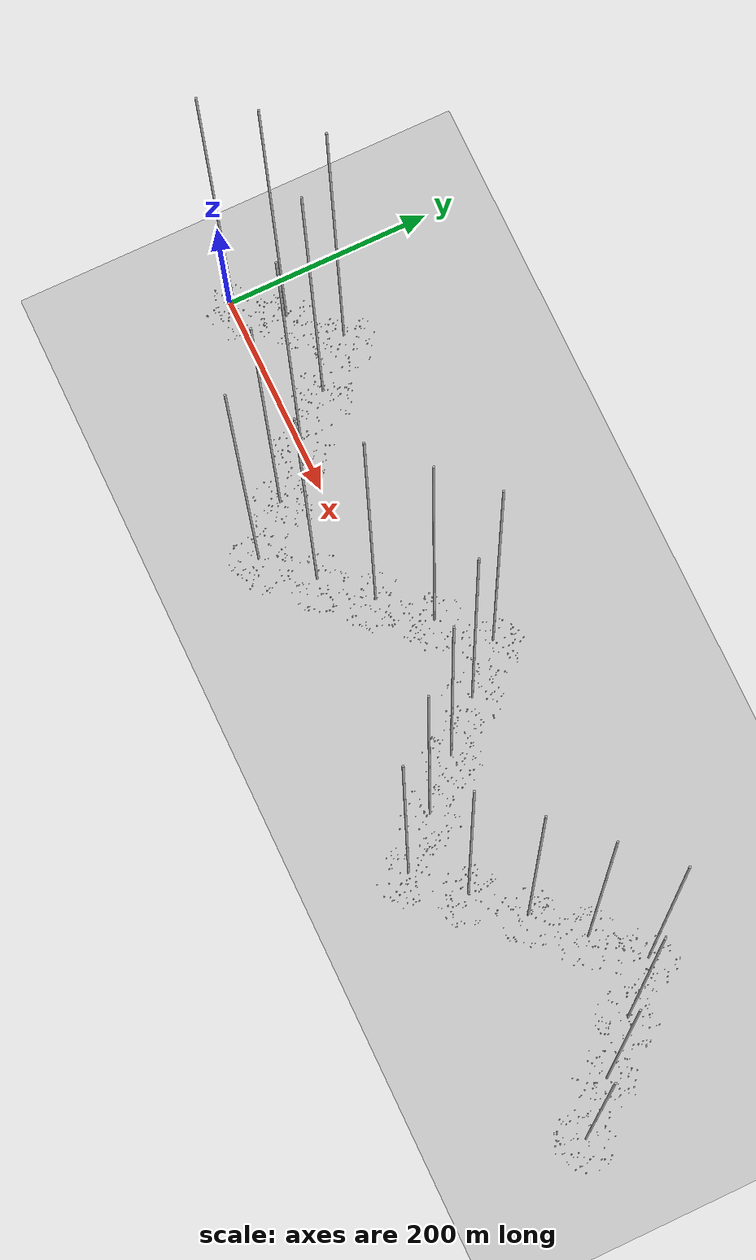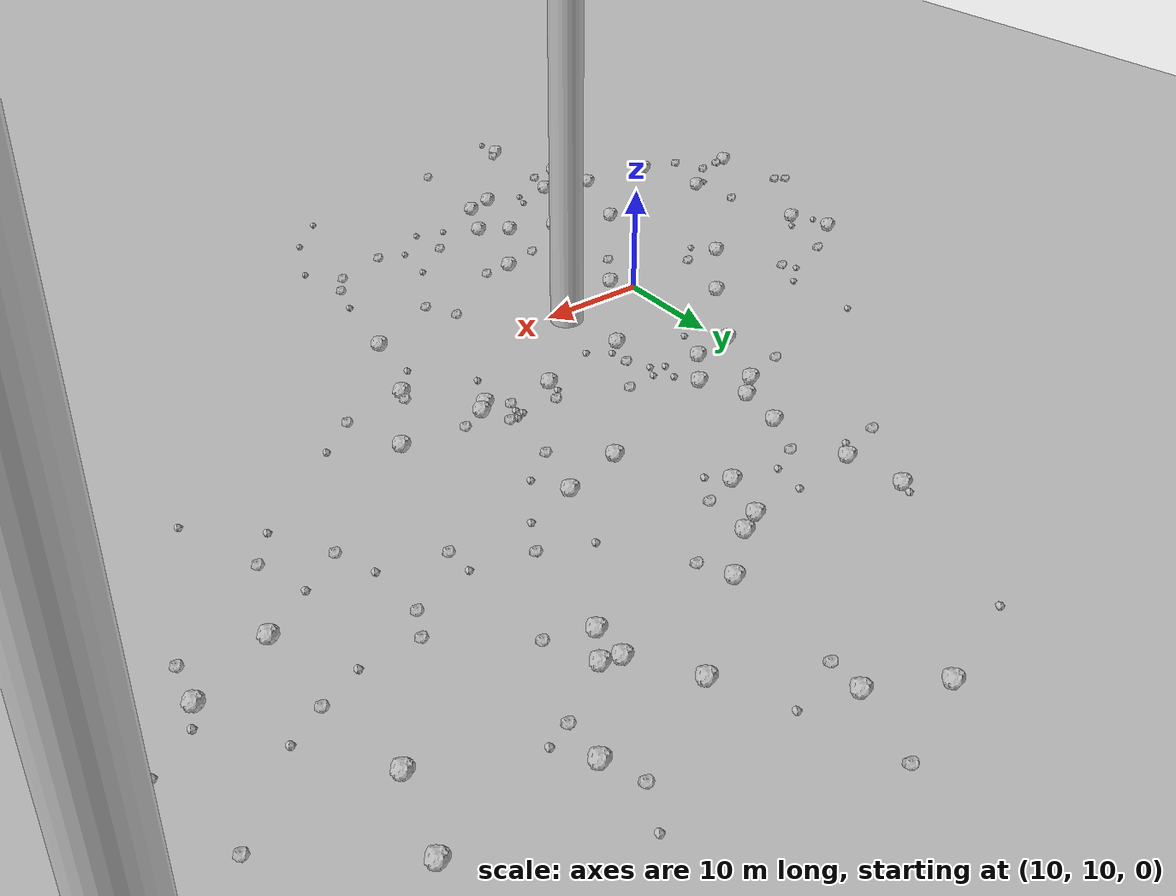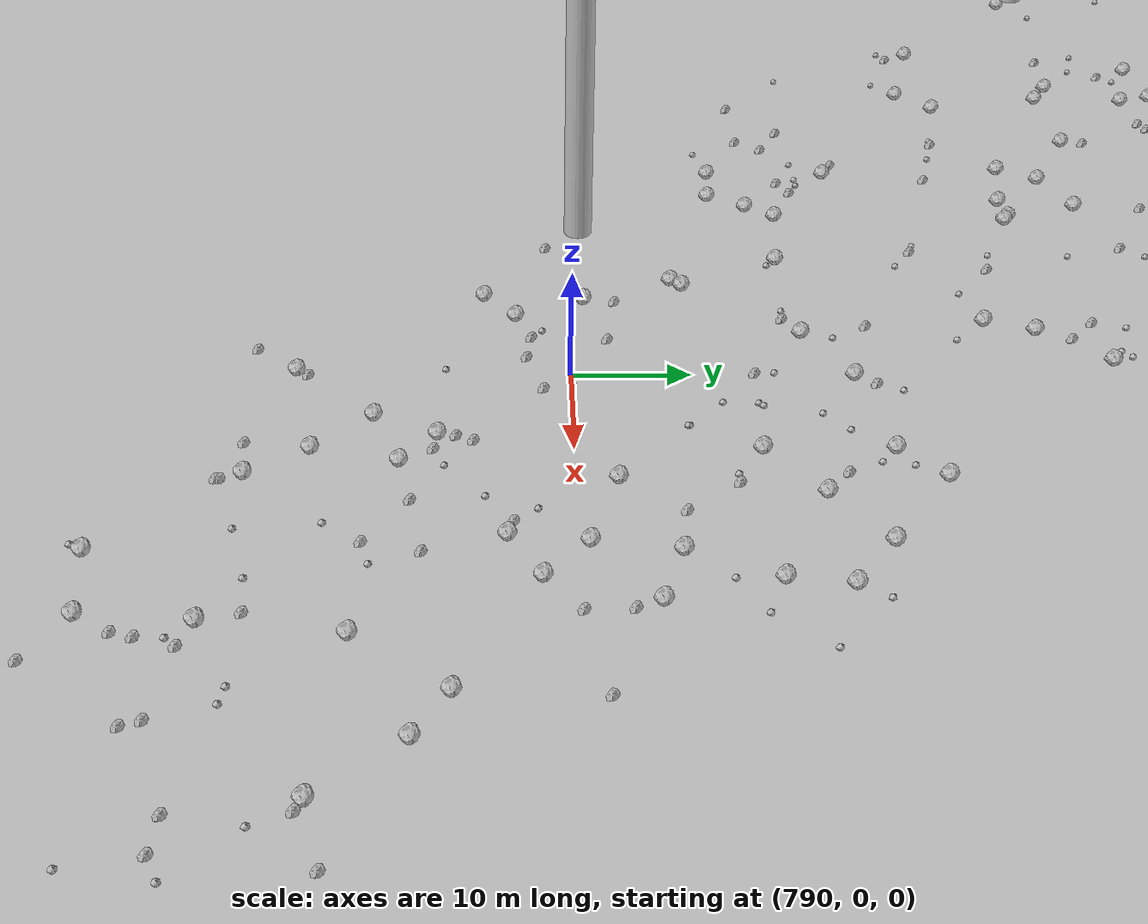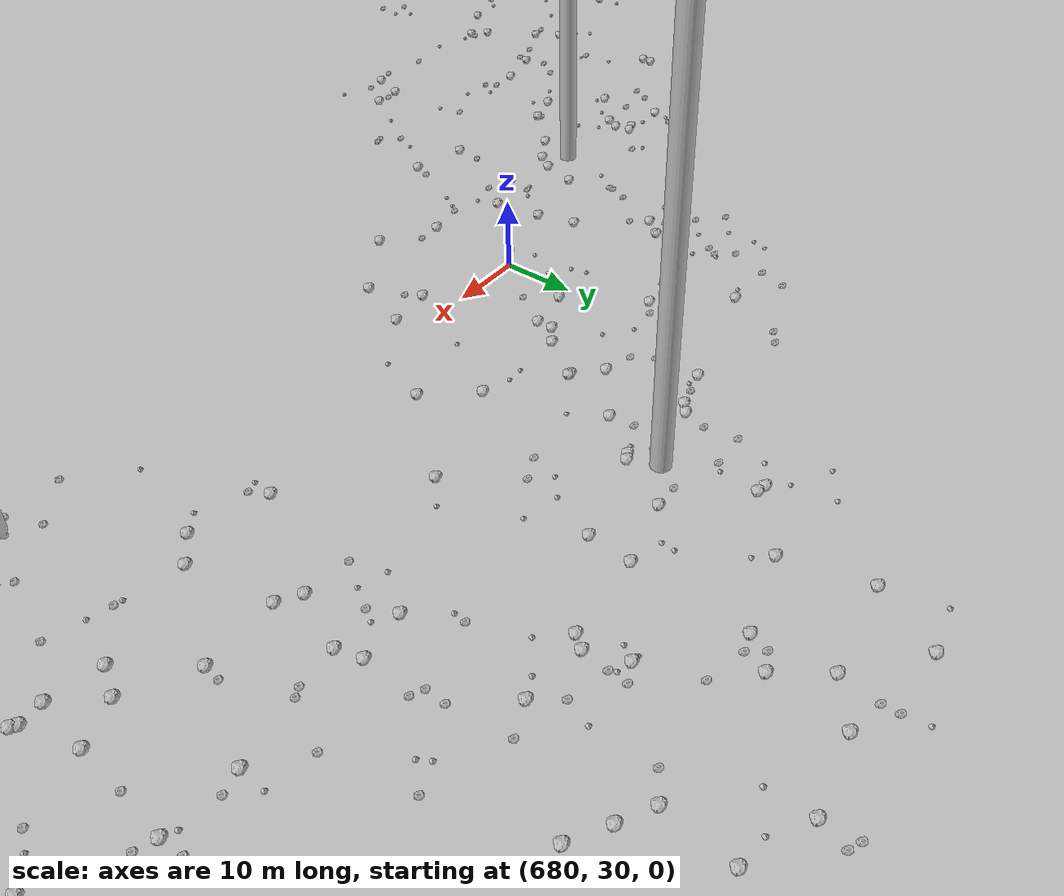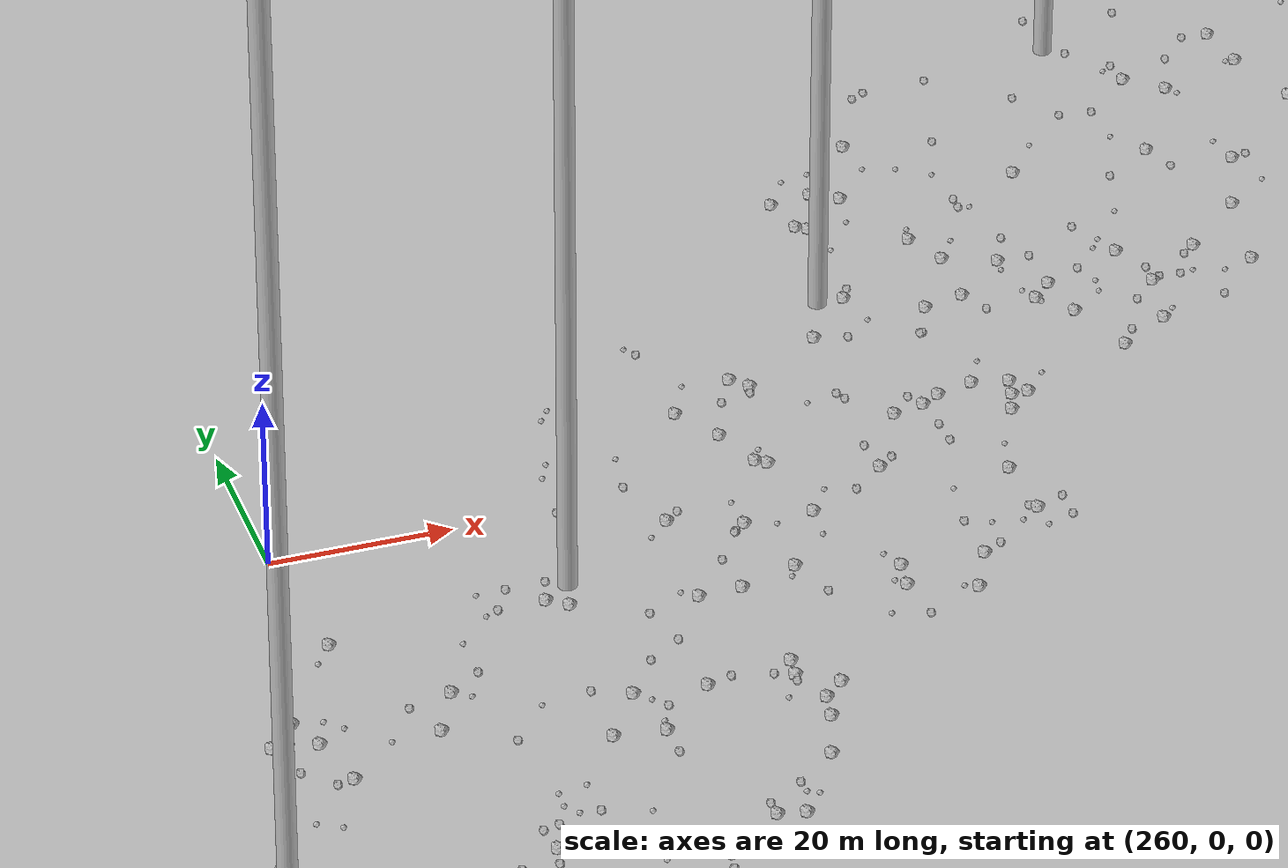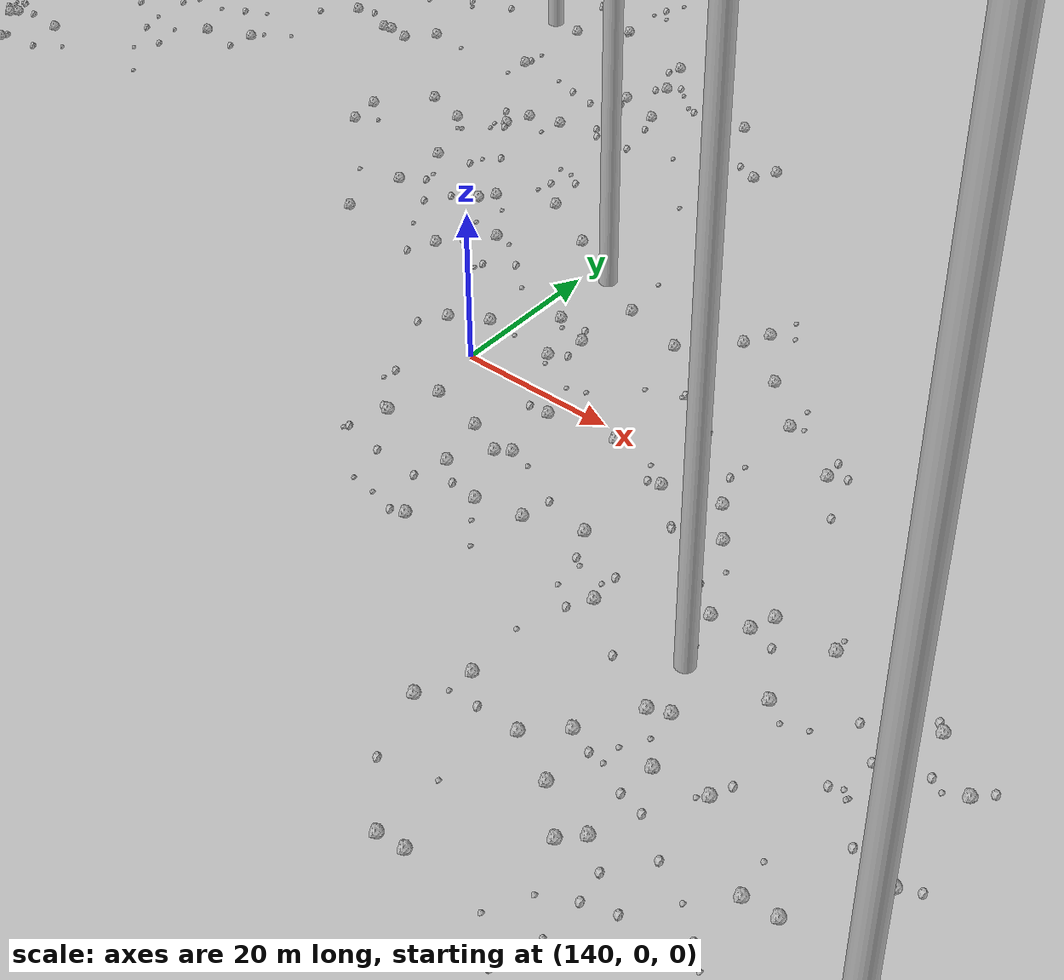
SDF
<sdf version="1.6">
 <world name="default">
  <include><uri>model://custom_ground</uri></include>
  <include><uri>model://sun</uri></include>
  <spherical_coordinates>
   <surface_model>EARTH_WGS84</surface_model>
   <latitude_deg>38.161479</latitude_deg>
   <longitude_deg>-122.454630</longitude_deg>
   <elevation>488.0</elevation>
   <heading_deg>90</heading_deg>
  </spherical_coordinates>
  <model name="rock1_0_0">
   <include><uri>model://rock1</uri><pose>11.550404807098296 8.20753072206665 0.5 0 0 0</pose></include>
  </model>
  <model name="rock1_0_1">
   <include><uri>model://rock1</uri><pose>-12.655127494358954 7.95848991887226 0.5 0 0 0</pose></include>
  </model>
  <model name="rock1_0_2">
   <include><uri>model://rock1</uri><pose>10.582291446313164 -14.382800737763876 0.5 0 0 0</pose></include>
  </model>
  <model name="rock1_0_3">
   <include><uri>model://rock1</uri><pose>35.161367688245285 5.5246842354656565 0.5 0 0 0</pose></include>
  </model>
  <model name="rock1_0_4">
   <include><uri>model://rock1</uri><pose>18.15653817740455 17.617917946867436 0.5 0 0 0</pose></include>
  </model>
  <model name="rock1_0_5">
   <include><uri>model://rock1</uri><pose>-10.07474883501904 -4.141929540057944 0.5 0 0 0</pose></include>
  </model>
  <model name="rock1_0_6">
   <include><uri>model://rock1</uri><pose>-1.041880895437469 -11.974386341888401 0.5 0 0 0</pose></include>
  </model>
  <model name="rock1_0_7">
   <include><uri>model://rock1</uri><pose>17.37175020576059 -0.3996413124813145 0.5 0 0 0</pose></include>
  </model>
  <model name="rock1_0_8">
   <include><uri>model://rock1</uri><pose>12.732997155793562 -7.05597879800208 0.5 0 0 0</pose></include>
  </model>
  <model name="rock1_0_9">
   <include><uri>model://rock1</uri><pose>4.569464579269447 15.540313734116928 0.5 0 0 0</pose></include>
  </model>
  <model name="rock1_0_10">
   <include><uri>model://rock1</uri><pose>3.8263515201866127 -13.393244631349994 0.5 0 0 0</pose></include>
  </model>
  <model name="rock1_0_11">
   <include><uri>model://rock1</uri><pose>-14.03676279933091 11.850364888012287 0.5 0 0 0</pose></include>
  </model>
  <model name="rock1_0_12">
   <include><uri>model://rock1</uri><pose>12.82079753391129 29.054645235850124 0.5 0 0 0</pose></include>
  </model>
  <model name="rock1_0_13">
   <include><uri>model://rock1</uri><pose>9.81982145204961 22.889881323841614 0.5 0 0 0</pose></include>
  </model>
  <model name="rock1_0_14">
   <include><uri>model://rock1</uri><pose>12.273032044167174 2.26242828016089 0.5 0 0 0</pose></include>
  </model>
  <model name="rock1_0_15">
   <include><uri>model://rock1</uri><pose>5.518809096876819 -8.56740991006307 0.5 0 0 0</pose></include>
  </model>
  <model name="rock1_0_16">
   <include><uri>model://rock1</uri><pose>0.12715256635353356 -16.891572030885317 0.5 0 0 0</pose></include>
  </model>
  <model name="rock1_0_17">
   <include><uri>model://rock1</uri><pose>32.916137609987324 18.943021476173605 0.5 0 0 0</pose></include>
  </model>
  <model name="rock1_0_18">
   <include><uri>model://rock1</uri><pose>-8.487745427410886 -11.273275015380328 0.5 0 0 0</pose></include>
  </model>
  <model name="rock1_0_19">
   <include><uri>model://rock1</uri><pose>13.94022276593477 23.645408746073258 0.5 0 0 0</pose></include>
  </model>
  <model name="rock1_0_20">
   <include><uri>model://rock1</uri><pose>15.338990433457987 -8.865070486528076 0.5 0 0 0</pose></include>
  </model>
  <model name="rock1_0_21">
   <include><uri>model://rock1</uri><pose>2.3913502774185567 -3.519492212549178 0.5 0 0 0</pose></include>
  </model>
  <model name="rock1_0_22">
   <include><uri>model://rock1</uri><pose>8.530364247524986 -5.210260573267874 0.5 0 0 0</pose></include>
  </model>
  <model name="rock1_0_23">
   <include><uri>model://rock1</uri><pose>-1.0493687348473983 9.23012227353675 0.5 0 0 0</pose></include>
  </model>
  <model name="rock1_0_24">
   <include><uri>model://rock1</uri><pose>-17.31589377884172 -7.758488635101127 0.5 0 0 0</pose></include>
  </model>
  <model name="rock1_0_25">
   <include><uri>model://rock1</uri><pose>2.4202465113991742 -25.096624748404576 0.5 0 0 0</pose></include>
  </model>
  <model name="rock1_0_26">
   <include><uri>model://rock1</uri><pose>13.252862835879242 -13.444271930786059 0.5 0 0 0</pose></include>
  </model>
  <model name="rock2_0_0">
   <include><uri>model://rock2</uri><pose>32.88862205007151 -5.621215883689953 0.3 0 0 0</pose></include>
  </model>
  <model name="rock2_0_1">
   <include><uri>model://rock2</uri><pose>-19.37820632890142 0.2529015471853171 0.3 0 0 0</pose></include>
  </model>
  <model name="rock2_0_2">
   <include><uri>model://rock2</uri><pose>31.145617053296434 20.163308914386285 0.3 0 0 0</pose></include>
  </model>
  <model name="rock2_0_3">
   <include><uri>model://rock2</uri><pose>-9.875952691028422 14.663636454395395 0.3 0 0 0</pose></include>
  </model>
  <model name="rock2_0_4">
   <include><uri>model://rock2</uri><pose>26.631165624010592 -9.55839742548466 0.3 0 0 0</pose></include>
  </model>
  <model name="rock2_0_5">
   <include><uri>model://rock2</uri><pose>20.638481126959007 -7.7332073803211685 0.3 0 0 0</pose></include>
  </model>
  <model name="rock2_0_6">
   <include><uri>model://rock2</uri><pose>8.64999678402572 4.256344309764231 0.3 0 0 0</pose></include>
  </model>
  <model name="rock2_0_7">
   <include><uri>model://rock2</uri><pose>-18.377610543577912 -0.4275041215964208 0.3 0 0 0</pose></include>
  </model>
  <model name="rock2_0_8">
   <include><uri>model://rock2</uri><pose>3.1063081303071414 -24.440769294166476 0.3 0 0 0</pose></include>
  </model>
  <model name="rock2_0_9">
   <include><uri>model://rock2</uri><pose>-1.1893039514597739 -14.20727474868675 0.3 0 0 0</pose></include>
  </model>
  <model name="rock2_0_10">
   <include><uri>model://rock2</uri><pose>2.831208777188987 -16.538772207086446 0.3 0 0 0</pose></include>
  </model>
  <model name="rock2_0_11">
   <include><uri>model://rock2</uri><pose>28.13263373087637 1.8729936184298595 0.3 0 0 0</pose></include>
  </model>
  <model name="rock2_0_12">
   <include><uri>model://rock2</uri><pose>13.610590015665416 -1.6952317786291893 0.3 0 0 0</pose></include>
  </model>
  <model name="rock2_0_13">
   <include><uri>model://rock2</uri><pose>-16.23976366790187 -7.702812068775042 0.3 0 0 0</pose></include>
  </model>
  <model name="rock2_0_14">
   <include><uri>model://rock2</uri><pose>20.01591413422073 11.739379536589865 0.3 0 0 0</pose></include>
  </model>
  <model name="rock2_0_15">
   <include><uri>model://rock2</uri><pose>12.26130204294381 -23.750151886124673 0.3 0 0 0</pose></include>
  </model>
  <model name="rock2_0_16">
   <include><uri>model://rock2</uri><pose>19.89775196370308 -0.37984109139596356 0.3 0 0 0</pose></include>
  </model>
  <model name="rock2_0_17">
   <include><uri>model://rock2</uri><pose>18.49055225929829 10.22240512039015 0.3 0 0 0</pose></include>
  </model>
  <model name="rock2_0_18">
   <include><uri>model://rock2</uri><pose>-11.05039824476627 0.5681652100934045 0.3 0 0 0</pose></include>
  </model>
  <model name="rock2_0_19">
   <include><uri>model://rock2</uri><pose>31.556470437699893 -7.759371649052113 0.3 0 0 0</pose></include>
  </model>
  <model name="rock2_0_20">
   <include><uri>model://rock2</uri><pose>8.572412103512526 27.76299993754619 0.3 0 0 0</pose></include>
  </model>
  <model name="rock2_0_21">
   <include><uri>model://rock2</uri><pose>-4.238730082883633 15.37028095402556 0.3 0 0 0</pose></include>
  </model>
  <model name="rock2_0_22">
   <include><uri>model://rock2</uri><pose>26.614972170026306 4.77883883761951 0.3 0 0 0</pose></include>
  </model>
  <model name="rock2_0_23">
   <include><uri>model://rock2</uri><pose>-13.88836263204416 -7.297546786318165 0.3 0 0 0</pose></include>
  </model>
  <model name="rock2_0_24">
   <include><uri>model://rock2</uri><pose>21.74168476889583 24.031291084031245 0.3 0 0 0</pose></include>
  </model>
  <model name="rock2_0_25">
   <include><uri>model://rock2</uri><pose>-12.470324618292377 -10.415446832609852 0.3 0 0 0</pose></include>
  </model>
  <model name="rock2_0_26">
   <include><uri>model://rock2</uri><pose>2.4573669696090796 9.072298858932157 0.3 0 0 0</pose></include>
  </model>
  <model name="rock3_0_0">
   <include><uri>model://rock3</uri><pose>6.993009023985518 -13.412937447003351 0.2 0 0 0</pose></include>
  </model>
  <model name="rock3_0_1">
   <include><uri>model://rock3</uri><pose>-11.472418327668898 9.373481537090903 0.2 0 0 0</pose></include>
  </model>
  <model name="rock3_0_2">
   <include><uri>model://rock3</uri><pose>0.2625537447536175 7.005558700565231 0.2 0 0 0</pose></include>
  </model>
  <model name="rock3_0_3">
   <include><uri>model://rock3</uri><pose>18.24311586336779 -10.948956204322496 0.2 0 0 0</pose></include>
  </model>
  <model name="rock3_0_4">
   <include><uri>model://rock3</uri><pose>18.239602347671976 22.426128875738435 0.2 0 0 0</pose></include>
  </model>
  <model name="rock3_0_5">
   <include><uri>model://rock3</uri><pose>33.75647631215188 -2.3102644580227327 0.2 0 0 0</pose></include>
  </model>
  <model name="rock3_0_6">
   <include><uri>model://rock3</uri><pose>-14.341982382759271 9.57763000143568 0.2 0 0 0</pose></include>
  </model>
  <model name="rock3_0_7">
   <include><uri>model://rock3</uri><pose>-11.677110118867574 -4.5873234722666005 0.2 0 0 0</pose></include>
  </model>
  <model name="rock3_0_8">
   <include><uri>model://rock3</uri><pose>12.373634202021385 20.1021383590407 0.2 0 0 0</pose></include>
  </model>
  <model name="rock3_0_9">
   <include><uri>model://rock3</uri><pose>31.61331501125421 -16.632598711577714 0.2 0 0 0</pose></include>
  </model>
  <model name="rock3_0_10">
   <include><uri>model://rock3</uri><pose>20.923608512600573 -11.775185009131192 0.2 0 0 0</pose></include>
  </model>
  <model name="rock3_0_11">
   <include><uri>model://rock3</uri><pose>24.035059902277965 -8.768936243656324 0.2 0 0 0</pose></include>
  </model>
  <model name="rock3_0_12">
   <include><uri>model://rock3</uri><pose>2.165412254939149 -28.183776581450413 0.2 0 0 0</pose></include>
  </model>
  <model name="rock3_0_13">
   <include><uri>model://rock3</uri><pose>7.5476098360618735 -11.911753427851849 0.2 0 0 0</pose></include>
  </model>
  <model name="rock3_0_14">
   <include><uri>model://rock3</uri><pose>33.98215735653967 -10.777856640127371 0.2 0 0 0</pose></include>
  </model>
  <model name="rock3_0_15">
   <include><uri>model://rock3</uri><pose>19.378107217170246 18.6108255420492 0.2 0 0 0</pose></include>
  </model>
  <model name="rock3_0_16">
   <include><uri>model://rock3</uri><pose>17.096198632176048 23.080247669035366 0.2 0 0 0</pose></include>
  </model>
  <model name="rock3_0_17">
   <include><uri>model://rock3</uri><pose>21.20322952396475 17.245508379467694 0.2 0 0 0</pose></include>
  </model>
  <model name="rock3_0_18">
   <include><uri>model://rock3</uri><pose>-5.0470465423832565 16.511742789897177 0.2 0 0 0</pose></include>
  </model>
  <model name="rock3_0_19">
   <include><uri>model://rock3</uri><pose>-2.8931218061874944 18.32994450863471 0.2 0 0 0</pose></include>
  </model>
  <model name="rock3_0_20">
   <include><uri>model://rock3</uri><pose>31.269055375919308 15.400205349647578 0.2 0 0 0</pose></include>
  </model>
  <model name="rock3_0_21">
   <include><uri>model://rock3</uri><pose>24.60206290320417 -4.486201665808917 0.2 0 0 0</pose></include>
  </model>
  <model name="rock3_0_22">
   <include><uri>model://rock3</uri><pose>35.21295212055504 10.515437018760863 0.2 0 0 0</pose></include>
  </model>
  <model name="rock3_0_23">
   <include><uri>model://rock3</uri><pose>28.174810942980564 -20.346742483553538 0.2 0 0 0</pose></include>
  </model>
  <model name="rock3_0_24">
   <include><uri>model://rock3</uri><pose>-3.027821872152792 25.209680138121257 0.2 0 0 0</pose></include>
  </model>
  <model name="rock3_0_25">
   <include><uri>model://rock3</uri><pose>18.86973321650111 23.619926945462893 0.2 0 0 0</pose></include>
  </model>
  <model name="rock3_0_26">
   <include><uri>model://rock3</uri><pose>-2.7852310025504536 -4.8487499292122145 0.2 0 0 0</pose></include>
  </model>
  <model name="rock1_1_0">
   <include><uri>model://rock1</uri><pose>33.800790706130144 19.78960179121426 0.5 0 0 0</pose></include>
  </model>
  <model name="rock1_1_1">
   <include><uri>model://rock1</uri><pose>23.94829564940287 38.96620930030772 0.5 0 0 0</pose></include>
  </model>
  <model name="rock1_1_2">
   <include><uri>model://rock1</uri><pose>58.19263831801996 48.66967729873385 0.5 0 0 0</pose></include>
  </model>
  <model name="rock1_1_3">
   <include><uri>model://rock1</uri><pose>59.83310973923665 55.10253835417122 0.5 0 0 0</pose></include>
  </model>
  <model name="rock1_1_4">
   <include><uri>model://rock1</uri><pose>39.3197727005779 53.461922243615724 0.5 0 0 0</pose></include>
  </model>
  <model name="rock1_1_5">
   <include><uri>model://rock1</uri><pose>15.741259024047311 34.92212147751909 0.5 0 0 0</pose></include>
  </model>
  <model name="rock1_1_6">
   <include><uri>model://rock1</uri><pose>14.065596897960365 46.913290136006594 0.5 0 0 0</pose></include>
  </model>
  <model name="rock1_1_7">
   <include><uri>model://rock1</uri><pose>26.863986041051444 19.510815073770083 0.5 0 0 0</pose></include>
  </model>
  <model name="rock1_1_8">
   <include><uri>model://rock1</uri><pose>16.653252508861023 26.87274061336373 0.5 0 0 0</pose></include>
  </model>
  <model name="rock1_1_9">
   <include><uri>model://rock1</uri><pose>28.9931638949918 31.12486463923601 0.5 0 0 0</pose></include>
  </model>
  <model name="rock1_1_10">
   <include><uri>model://rock1</uri><pose>59.37442684333896 33.77108841025422 0.5 0 0 0</pose></include>
  </model>
  <model name="rock1_1_11">
   <include><uri>model://rock1</uri><pose>14.745756484009904 41.98259819345027 0.5 0 0 0</pose></include>
  </model>
  <model name="rock1_1_12">
   <include><uri>model://rock1</uri><pose>27.396750888856175 44.071263468096234 0.5 0 0 0</pose></include>
  </model>
  <model name="rock1_1_13">
   <include><uri>model://rock1</uri><pose>31.361488116219288 47.341871925204366 0.5 0 0 0</pose></include>
  </model>
  <model name="rock1_1_14">
   <include><uri>model://rock1</uri><pose>42.312318848955684 48.86718241754022 0.5 0 0 0</pose></include>
  </model>
  <model name="rock1_1_15">
   <include><uri>model://rock1</uri><pose>43.7735604458188 48.46582810924997 0.5 0 0 0</pose></include>
  </model>
  <model name="rock1_1_16">
   <include><uri>model://rock1</uri><pose>25.40474070039109 43.0572777757507 0.5 0 0 0</pose></include>
  </model>
  <model name="rock1_1_17">
   <include><uri>model://rock1</uri><pose>48.679840475845616 54.788582135825685 0.5 0 0 0</pose></include>
  </model>
  <model name="rock1_1_18">
   <include><uri>model://rock1</uri><pose>42.09636910913327 45.894755894092235 0.5 0 0 0</pose></include>
  </model>
  <model name="rock1_1_19">
   <include><uri>model://rock1</uri><pose>53.88671236510534 63.673652458460964 0.5 0 0 0</pose></include>
  </model>
  <model name="rock1_1_20">
   <include><uri>model://rock1</uri><pose>14.881688609385256 30.809210629306463 0.5 0 0 0</pose></include>
  </model>
  <model name="rock1_1_21">
   <include><uri>model://rock1</uri><pose>32.42476981400364 59.91183208077015 0.5 0 0 0</pose></include>
  </model>
  <model name="rock1_1_22">
   <include><uri>model://rock1</uri><pose>34.43172993213916 32.67590238069606 0.5 0 0 0</pose></include>
  </model>
  <model name="rock1_1_23">
   <include><uri>model://rock1</uri><pose>27.26215345748353 62.76192935039313 0.5 0 0 0</pose></include>
  </model>
  <model name="rock1_1_24">
   <include><uri>model://rock1</uri><pose>65.63089941023307 36.48841148430787 0.5 0 0 0</pose></include>
  </model>
  <model name="rock1_1_25">
   <include><uri>model://rock1</uri><pose>41.519899539693014 20.179488715729725 0.5 0 0 0</pose></include>
  </model>
  <model name="rock1_1_26">
   <include><uri>model://rock1</uri><pose>37.53780324281031 13.40217881937071 0.5 0 0 0</pose></include>
  </model>
  <model name="rock2_1_0">
   <include><uri>model://rock2</uri><pose>59.469546104460925 41.3055251147146 0.3 0 0 0</pose></include>
  </model>
  <model name="rock2_1_1">
   <include><uri>model://rock2</uri><pose>40.542936169902404 37.002598806120616 0.3 0 0 0</pose></include>
  </model>
  <model name="rock2_1_2">
   <include><uri>model://rock2</uri><pose>31.982108293922394 57.047431139210616 0.3 0 0 0</pose></include>
  </model>
  <model name="rock2_1_3">
   <include><uri>model://rock2</uri><pose>68.03896744431097 48.44236280539646 0.3 0 0 0</pose></include>
  </model>
  <model name="rock2_1_4">
   <include><uri>model://rock2</uri><pose>51.86224894367561 28.747059352541907 0.3 0 0 0</pose></include>
  </model>
  <model name="rock2_1_5">
   <include><uri>model://rock2</uri><pose>26.921930776952248 39.88226410876287 0.3 0 0 0</pose></include>
  </model>
  <model name="rock2_1_6">
   <include><uri>model://rock2</uri><pose>32.56962210996885 22.141223857946393 0.3 0 0 0</pose></include>
  </model>
  <model name="rock2_1_7">
   <include><uri>model://rock2</uri><pose>19.332398518974557 20.569526604822705 0.3 0 0 0</pose></include>
  </model>
  <model name="rock2_1_8">
   <include><uri>model://rock2</uri><pose>51.475611786888095 39.711668058906206 0.3 0 0 0</pose></include>
  </model>
  <model name="rock2_1_9">
   <include><uri>model://rock2</uri><pose>48.316463907730544 51.3278403490175 0.3 0 0 0</pose></include>
  </model>
  <model name="rock2_1_10">
   <include><uri>model://rock2</uri><pose>43.2537516485797 14.64700676912345 0.3 0 0 0</pose></include>
  </model>
  <model name="rock2_1_11">
   <include><uri>model://rock2</uri><pose>17.449738596811585 38.62981900502752 0.3 0 0 0</pose></include>
  </model>
  <model name="rock2_1_12">
   <include><uri>model://rock2</uri><pose>45.44621971698102 33.409237221249 0.3 0 0 0</pose></include>
  </model>
  <model name="rock2_1_13">
   <include><uri>model://rock2</uri><pose>27.717204255253332 21.78202515989413 0.3 0 0 0</pose></include>
  </model>
  <model name="rock2_1_14">
   <include><uri>model://rock2</uri><pose>65.16241826471705 32.76949340617652 0.3 0 0 0</pose></include>
  </model>
  <model name="rock2_1_15">
   <include><uri>model://rock2</uri><pose>45.399985351079806 44.59780916855795 0.3 0 0 0</pose></include>
  </model>
  <model name="rock2_1_16">
   <include><uri>model://rock2</uri><pose>47.4266590398364 57.60785681870779 0.3 0 0 0</pose></include>
  </model>
  <model name="rock2_1_17">
   <include><uri>model://rock2</uri><pose>35.965496985702345 20.831589698262274 0.3 0 0 0</pose></include>
  </model>
  <model name="rock2_1_18">
   <include><uri>model://rock2</uri><pose>32.92640559785476 27.582119753309506 0.3 0 0 0</pose></include>
  </model>
  <model name="rock2_1_19">
   <include><uri>model://rock2</uri><pose>50.37200504457324 37.320132901283 0.3 0 0 0</pose></include>
  </model>
  <model name="rock2_1_20">
   <include><uri>model://rock2</uri><pose>10.131349356509613 40.390975295384344 0.3 0 0 0</pose></include>
  </model>
  <model name="rock2_1_21">
   <include><uri>model://rock2</uri><pose>64.28287479561838 55.205088996111805 0.3 0 0 0</pose></include>
  </model>
  <model name="rock2_1_22">
   <include><uri>model://rock2</uri><pose>37.76416152704576 14.427927259828113 0.3 0 0 0</pose></include>
  </model>
  <model name="rock2_1_23">
   <include><uri>model://rock2</uri><pose>56.75563568827782 26.708477063232277 0.3 0 0 0</pose></include>
  </model>
  <model name="rock2_1_24">
   <include><uri>model://rock2</uri><pose>32.38216700622793 44.691320126347 0.3 0 0 0</pose></include>
  </model>
  <model name="rock2_1_25">
   <include><uri>model://rock2</uri><pose>34.34927988271499 65.69115931133835 0.3 0 0 0</pose></include>
  </model>
  <model name="rock2_1_26">
   <include><uri>model://rock2</uri><pose>56.3551155247664 61.68428542142388 0.3 0 0 0</pose></include>
  </model>
  <model name="rock3_1_0">
   <include><uri>model://rock3</uri><pose>30.995571389237618 21.744174415794248 0.2 0 0 0</pose></include>
  </model>
  <model name="rock3_1_1">
   <include><uri>model://rock3</uri><pose>50.55072496294787 32.107345715185005 0.2 0 0 0</pose></include>
  </model>
  <model name="rock3_1_2">
   <include><uri>model://rock3</uri><pose>17.5957600175419 24.83515115323041 0.2 0 0 0</pose></include>
  </model>
  <model name="rock3_1_3">
   <include><uri>model://rock3</uri><pose>69.8100513123457 40.42860738438685 0.2 0 0 0</pose></include>
  </model>
  <model name="rock3_1_4">
   <include><uri>model://rock3</uri><pose>13.231112107918758 40.48082509406595 0.2 0 0 0</pose></include>
  </model>
  <model name="rock3_1_5">
   <include><uri>model://rock3</uri><pose>20.38573787449005 42.60087177983303 0.2 0 0 0</pose></include>
  </model>
  <model name="rock3_1_6">
   <include><uri>model://rock3</uri><pose>19.0605655003656 59.94386635406621 0.2 0 0 0</pose></include>
  </model>
  <model name="rock3_1_7">
   <include><uri>model://rock3</uri><pose>59.43442131104863 19.32892925192631 0.2 0 0 0</pose></include>
  </model>
  <model name="rock3_1_8">
   <include><uri>model://rock3</uri><pose>62.34309975736234 42.89978389107677 0.2 0 0 0</pose></include>
  </model>
  <model name="rock3_1_9">
   <include><uri>model://rock3</uri><pose>14.16116693083401 47.7973516566827 0.2 0 0 0</pose></include>
  </model>
  <model name="rock3_1_10">
   <include><uri>model://rock3</uri><pose>54.57698247111868 23.728127930288576 0.2 0 0 0</pose></include>
  </model>
  <model name="rock3_1_11">
   <include><uri>model://rock3</uri><pose>66.4500161718798 38.22036024638394 0.2 0 0 0</pose></include>
  </model>
  <model name="rock3_1_12">
   <include><uri>model://rock3</uri><pose>25.168307496813 37.30100624573846 0.2 0 0 0</pose></include>
  </model>
  <model name="rock3_1_13">
   <include><uri>model://rock3</uri><pose>49.05745645486124 60.705537780351065 0.2 0 0 0</pose></include>
  </model>
  <model name="rock3_1_14">
   <include><uri>model://rock3</uri><pose>31.324883882293758 21.146560314077732 0.2 0 0 0</pose></include>
  </model>
  <model name="rock3_1_15">
   <include><uri>model://rock3</uri><pose>55.27711792566035 30.99848553505658 0.2 0 0 0</pose></include>
  </model>
  <model name="rock3_1_16">
   <include><uri>model://rock3</uri><pose>46.46664337750082 17.27949337394552 0.2 0 0 0</pose></include>
  </model>
  <model name="rock3_1_17">
   <include><uri>model://rock3</uri><pose>36.494894678155504 38.59101848628562 0.2 0 0 0</pose></include>
  </model>
  <model name="rock3_1_18">
   <include><uri>model://rock3</uri><pose>45.30811960188728 35.81302856699675 0.2 0 0 0</pose></include>
  </model>
  <model name="rock3_1_19">
   <include><uri>model://rock3</uri><pose>50.2562080594825 52.106864725752835 0.2 0 0 0</pose></include>
  </model>
  <model name="rock3_1_20">
   <include><uri>model://rock3</uri><pose>35.89575490793571 29.771272097181907 0.2 0 0 0</pose></include>
  </model>
  <model name="rock3_1_21">
   <include><uri>model://rock3</uri><pose>26.743172318165133 20.643227006216996 0.2 0 0 0</pose></include>
  </model>
  <model name="rock3_1_22">
   <include><uri>model://rock3</uri><pose>38.82306429798117 33.99691610568789 0.2 0 0 0</pose></include>
  </model>
  <model name="rock3_1_23">
   <include><uri>model://rock3</uri><pose>56.06625905815135 39.696600601734474 0.2 0 0 0</pose></include>
  </model>
  <model name="rock3_1_24">
   <include><uri>model://rock3</uri><pose>36.58257871353813 58.664920811183784 0.2 0 0 0</pose></include>
  </model>
  <model name="rock3_1_25">
   <include><uri>model://rock3</uri><pose>31.81275337083869 22.187802336587453 0.2 0 0 0</pose></include>
  </model>
  <model name="rock3_1_26">
   <include><uri>model://rock3</uri><pose>19.910292813896618 39.77746364400626 0.2 0 0 0</pose></include>
  </model>
  <model name="rock1_2_0">
   <include><uri>model://rock1</uri><pose>83.89125713024738 71.56209272498039 0.5 0 0 0</pose></include>
  </model>
  <model name="rock1_2_1">
   <include><uri>model://rock1</uri><pose>107.39668021330424 72.2450073632159 0.5 0 0 0</pose></include>
  </model>
  <model name="rock1_2_2">
   <include><uri>model://rock1</uri><pose>54.29632375285382 77.36525730964479 0.5 0 0 0</pose></include>
  </model>
  <model name="rock1_2_3">
   <include><uri>model://rock1</uri><pose>90.32618455664053 84.72058173318047 0.5 0 0 0</pose></include>
  </model>
  <model name="rock1_2_4">
   <include><uri>model://rock1</uri><pose>70.86643896675815 68.7977962093461 0.5 0 0 0</pose></include>
  </model>
  <model name="rock1_2_5">
   <include><uri>model://rock1</uri><pose>61.33436085413288 61.82855083632641 0.5 0 0 0</pose></include>
  </model>
  <model name="rock1_2_6">
   <include><uri>model://rock1</uri><pose>58.20543323639266 73.57783450399624 0.5 0 0 0</pose></include>
  </model>
  <model name="rock1_2_7">
   <include><uri>model://rock1</uri><pose>78.84942330785123 66.91762012490778 0.5 0 0 0</pose></include>
  </model>
  <model name="rock1_2_8">
   <include><uri>model://rock1</uri><pose>64.97632292353777 77.57376915287225 0.5 0 0 0</pose></include>
  </model>
  <model name="rock1_2_9">
   <include><uri>model://rock1</uri><pose>86.16816376604359 53.90857683403026 0.5 0 0 0</pose></include>
  </model>
  <model name="rock1_2_10">
   <include><uri>model://rock1</uri><pose>63.77997279149628 69.59053676092347 0.5 0 0 0</pose></include>
  </model>
  <model name="rock1_2_11">
   <include><uri>model://rock1</uri><pose>67.03195436553173 101.38228720862486 0.5 0 0 0</pose></include>
  </model>
  <model name="rock1_2_12">
   <include><uri>model://rock1</uri><pose>103.65153597625087 95.26484916968661 0.5 0 0 0</pose></include>
  </model>
  <model name="rock1_2_13">
   <include><uri>model://rock1</uri><pose>80.21673900104432 92.43688539474745 0.5 0 0 0</pose></include>
  </model>
  <model name="rock1_2_14">
   <include><uri>model://rock1</uri><pose>72.50640267822429 99.3704965467746 0.5 0 0 0</pose></include>
  </model>
  <model name="rock1_2_15">
   <include><uri>model://rock1</uri><pose>96.24569402079305 76.98050116199647 0.5 0 0 0</pose></include>
  </model>
  <model name="rock1_2_16">
   <include><uri>model://rock1</uri><pose>72.07031922136575 52.26236126322247 0.5 0 0 0</pose></include>
  </model>
  <model name="rock1_2_17">
   <include><uri>model://rock1</uri><pose>79.9063565816382 51.04272958265279 0.5 0 0 0</pose></include>
  </model>
  <model name="rock1_2_18">
   <include><uri>model://rock1</uri><pose>80.32161622062068 75.1302271129268 0.5 0 0 0</pose></include>
  </model>
  <model name="rock1_2_19">
   <include><uri>model://rock1</uri><pose>99.91868168299067 75.79472952573087 0.5 0 0 0</pose></include>
  </model>
  <model name="rock1_2_20">
   <include><uri>model://rock1</uri><pose>90.6857567070088 98.79825672377265 0.5 0 0 0</pose></include>
  </model>
  <model name="rock1_2_21">
   <include><uri>model://rock1</uri><pose>59.26359007339789 78.2544419415232 0.5 0 0 0</pose></include>
  </model>
  <model name="rock1_2_22">
   <include><uri>model://rock1</uri><pose>83.04101281924582 50.44205411176752 0.5 0 0 0</pose></include>
  </model>
  <model name="rock1_2_23">
   <include><uri>model://rock1</uri><pose>101.42672788739641 67.54451503174589 0.5 0 0 0</pose></include>
  </model>
  <model name="rock1_2_24">
   <include><uri>model://rock1</uri><pose>72.53576781717763 94.57541776058093 0.5 0 0 0</pose></include>
  </model>
  <model name="rock1_2_25">
   <include><uri>model://rock1</uri><pose>78.63955612188835 50.81534186846675 0.5 0 0 0</pose></include>
  </model>
  <model name="rock1_2_26">
   <include><uri>model://rock1</uri><pose>71.82844100167544 86.86661913092192 0.5 0 0 0</pose></include>
  </model>
  <model name="rock2_2_0">
   <include><uri>model://rock2</uri><pose>85.83513779426634 87.18801873280319 0.3 0 0 0</pose></include>
  </model>
  <model name="rock2_2_1">
   <include><uri>model://rock2</uri><pose>92.07651861376053 75.9865122410647 0.3 0 0 0</pose></include>
  </model>
  <model name="rock2_2_2">
   <include><uri>model://rock2</uri><pose>83.02802470124558 109.20857541425124 0.3 0 0 0</pose></include>
  </model>
  <model name="rock2_2_3">
   <include><uri>model://rock2</uri><pose>75.29954406058259 63.95330640897551 0.3 0 0 0</pose></include>
  </model>
  <model name="rock2_2_4">
   <include><uri>model://rock2</uri><pose>68.71219127067408 88.45807592711292 0.3 0 0 0</pose></include>
  </model>
  <model name="rock2_2_5">
   <include><uri>model://rock2</uri><pose>74.3094152655834 99.63946455884545 0.3 0 0 0</pose></include>
  </model>
  <model name="rock2_2_6">
   <include><uri>model://rock2</uri><pose>72.78864117588574 61.917288880997894 0.3 0 0 0</pose></include>
  </model>
  <model name="rock2_2_7">
   <include><uri>model://rock2</uri><pose>65.3896571185258 75.09980807172398 0.3 0 0 0</pose></include>
  </model>
  <model name="rock2_2_8">
   <include><uri>model://rock2</uri><pose>87.27908392238835 98.59624111312716 0.3 0 0 0</pose></include>
  </model>
  <model name="rock2_2_9">
   <include><uri>model://rock2</uri><pose>83.45390125844091 64.95633827869547 0.3 0 0 0</pose></include>
  </model>
  <model name="rock2_2_10">
   <include><uri>model://rock2</uri><pose>74.64019600640671 53.0731757645142 0.3 0 0 0</pose></include>
  </model>
  <model name="rock2_2_11">
   <include><uri>model://rock2</uri><pose>70.96580015046179 108.06915426070599 0.3 0 0 0</pose></include>
  </model>
  <model name="rock2_2_12">
   <include><uri>model://rock2</uri><pose>66.66776217282488 59.69131418028107 0.3 0 0 0</pose></include>
  </model>
  <model name="rock2_2_13">
   <include><uri>model://rock2</uri><pose>87.1739360769204 101.82995195189463 0.3 0 0 0</pose></include>
  </model>
  <model name="rock2_2_14">
   <include><uri>model://rock2</uri><pose>58.04012763352888 83.25616670603723 0.3 0 0 0</pose></include>
  </model>
  <model name="rock2_2_15">
   <include><uri>model://rock2</uri><pose>53.6916447848718 67.17763068620579 0.3 0 0 0</pose></include>
  </model>
  <model name="rock2_2_16">
   <include><uri>model://rock2</uri><pose>107.40888930862675 71.96675047709049 0.3 0 0 0</pose></include>
  </model>
  <model name="rock2_2_17">
   <include><uri>model://rock2</uri><pose>107.64328995000753 80.83661936312629 0.3 0 0 0</pose></include>
  </model>
  <model name="rock2_2_18">
   <include><uri>model://rock2</uri><pose>94.70234023033183 77.96632031335619 0.3 0 0 0</pose></include>
  </model>
  <model name="rock2_2_19">
   <include><uri>model://rock2</uri><pose>83.09882850375874 80.20798576091086 0.3 0 0 0</pose></include>
  </model>
  <model name="rock2_2_20">
   <include><uri>model://rock2</uri><pose>105.31907267602779 93.30902644196354 0.3 0 0 0</pose></include>
  </model>
  <model name="rock2_2_21">
   <include><uri>model://rock2</uri><pose>57.44253306489416 66.4241164777327 0.3 0 0 0</pose></include>
  </model>
  <model name="rock2_2_22">
   <include><uri>model://rock2</uri><pose>64.82497817525709 70.24731879494433 0.3 0 0 0</pose></include>
  </model>
  <model name="rock2_2_23">
   <include><uri>model://rock2</uri><pose>75.94455974831476 102.5954582254796 0.3 0 0 0</pose></include>
  </model>
  <model name="rock2_2_24">
   <include><uri>model://rock2</uri><pose>103.28429704561893 74.2394402854903 0.3 0 0 0</pose></include>
  </model>
  <model name="rock2_2_25">
   <include><uri>model://rock2</uri><pose>66.63502980968073 105.52243258150588 0.3 0 0 0</pose></include>
  </model>
  <model name="rock2_2_26">
   <include><uri>model://rock2</uri><pose>89.37956454587186 66.90958699892659 0.3 0 0 0</pose></include>
  </model>
  <model name="rock3_2_0">
   <include><uri>model://rock3</uri><pose>84.37975679994346 63.776699167379576 0.2 0 0 0</pose></include>
  </model>
  <model name="rock3_2_1">
   <include><uri>model://rock3</uri><pose>102.37575486901503 98.84249967966659 0.2 0 0 0</pose></include>
  </model>
  <model name="rock3_2_2">
   <include><uri>model://rock3</uri><pose>103.64754346611936 97.41485057103228 0.2 0 0 0</pose></include>
  </model>
  <model name="rock3_2_3">
   <include><uri>model://rock3</uri><pose>78.37063168782035 105.13753504284887 0.2 0 0 0</pose></include>
  </model>
  <model name="rock3_2_4">
   <include><uri>model://rock3</uri><pose>86.92953470013734 89.5676837991274 0.2 0 0 0</pose></include>
  </model>
  <model name="rock3_2_5">
   <include><uri>model://rock3</uri><pose>59.36031296769645 94.82133631672527 0.2 0 0 0</pose></include>
  </model>
  <model name="rock3_2_6">
   <include><uri>model://rock3</uri><pose>74.23503300894319 103.41797451375909 0.2 0 0 0</pose></include>
  </model>
  <model name="rock3_2_7">
   <include><uri>model://rock3</uri><pose>94.19732376188098 101.36127135665265 0.2 0 0 0</pose></include>
  </model>
  <model name="rock3_2_8">
   <include><uri>model://rock3</uri><pose>61.442502631138765 69.20338110133153 0.2 0 0 0</pose></include>
  </model>
  <model name="rock3_2_9">
   <include><uri>model://rock3</uri><pose>72.46192571894974 66.43821647961663 0.2 0 0 0</pose></include>
  </model>
  <model name="rock3_2_10">
   <include><uri>model://rock3</uri><pose>56.71411068390606 71.15315378400273 0.2 0 0 0</pose></include>
  </model>
  <model name="rock3_2_11">
   <include><uri>model://rock3</uri><pose>57.56698289051345 60.30085643992412 0.2 0 0 0</pose></include>
  </model>
  <model name="rock3_2_12">
   <include><uri>model://rock3</uri><pose>87.41169829438738 84.1539281908814 0.2 0 0 0</pose></include>
  </model>
  <model name="rock3_2_13">
   <include><uri>model://rock3</uri><pose>61.85312431803216 79.77367058049118 0.2 0 0 0</pose></include>
  </model>
  <model name="rock3_2_14">
   <include><uri>model://rock3</uri><pose>70.44123389019354 67.38358221480973 0.2 0 0 0</pose></include>
  </model>
  <model name="rock3_2_15">
   <include><uri>model://rock3</uri><pose>82.11546081415229 73.71960860333182 0.2 0 0 0</pose></include>
  </model>
  <model name="rock3_2_16">
   <include><uri>model://rock3</uri><pose>106.82202007640733 78.87716991572628 0.2 0 0 0</pose></include>
  </model>
  <model name="rock3_2_17">
   <include><uri>model://rock3</uri><pose>108.69135447235806 83.71588343473815 0.2 0 0 0</pose></include>
  </model>
  <model name="rock3_2_18">
   <include><uri>model://rock3</uri><pose>91.16616074056545 53.53457563360692 0.2 0 0 0</pose></include>
  </model>
  <model name="rock3_2_19">
   <include><uri>model://rock3</uri><pose>78.07030206732361 61.28113418767708 0.2 0 0 0</pose></include>
  </model>
  <model name="rock3_2_20">
   <include><uri>model://rock3</uri><pose>57.783853468017455 73.804742108331 0.2 0 0 0</pose></include>
  </model>
  <model name="rock3_2_21">
   <include><uri>model://rock3</uri><pose>70.53704631584668 96.70368556946858 0.2 0 0 0</pose></include>
  </model>
  <model name="rock3_2_22">
   <include><uri>model://rock3</uri><pose>81.51320210362013 94.16831005824997 0.2 0 0 0</pose></include>
  </model>
  <model name="rock3_2_23">
   <include><uri>model://rock3</uri><pose>90.6848974622377 87.79838960120604 0.2 0 0 0</pose></include>
  </model>
  <model name="rock3_2_24">
   <include><uri>model://rock3</uri><pose>60.86555495257486 97.28852452683402 0.2 0 0 0</pose></include>
  </model>
  <model name="rock3_2_25">
   <include><uri>model://rock3</uri><pose>82.66992767830922 100.96198469531383 0.2 0 0 0</pose></include>
  </model>
  <model name="rock3_2_26">
   <include><uri>model://rock3</uri><pose>109.02000738184213 78.97193266048474 0.2 0 0 0</pose></include>
  </model>
  <model name="rock1_3_0">
   <include><uri>model://rock1</uri><pose>126.43239037157791 66.37009621630474 0.5 0 0 0</pose></include>
  </model>
  <model name="rock1_3_1">
   <include><uri>model://rock1</uri><pose>115.48844713337964 46.35450738311967 0.5 0 0 0</pose></include>
  </model>
  <model name="rock1_3_2">
   <include><uri>model://rock1</uri><pose>126.44890734262536 20.36170356065604 0.5 0 0 0</pose></include>
  </model>
  <model name="rock1_3_3">
   <include><uri>model://rock1</uri><pose>120.26710812480582 27.46883379325999 0.5 0 0 0</pose></include>
  </model>
  <model name="rock1_3_4">
   <include><uri>model://rock1</uri><pose>121.29670415063592 62.86725685813618 0.5 0 0 0</pose></include>
  </model>
  <model name="rock1_3_5">
   <include><uri>model://rock1</uri><pose>121.4031381656564 14.490721537712098 0.5 0 0 0</pose></include>
  </model>
  <model name="rock1_3_6">
   <include><uri>model://rock1</uri><pose>107.84942138144913 30.078341179942704 0.5 0 0 0</pose></include>
  </model>
  <model name="rock1_3_7">
   <include><uri>model://rock1</uri><pose>127.66365483967229 30.6487482339833 0.5 0 0 0</pose></include>
  </model>
  <model name="rock1_3_8">
   <include><uri>model://rock1</uri><pose>119.40479413571761 68.5667872329231 0.5 0 0 0</pose></include>
  </model>
  <model name="rock1_3_9">
   <include><uri>model://rock1</uri><pose>124.2359846531755 55.4683018890618 0.5 0 0 0</pose></include>
  </model>
  <model name="rock1_3_10">
   <include><uri>model://rock1</uri><pose>118.77053663522082 55.17905405158697 0.5 0 0 0</pose></include>
  </model>
  <model name="rock1_3_11">
   <include><uri>model://rock1</uri><pose>103.61020853906564 38.7299843191638 0.5 0 0 0</pose></include>
  </model>
  <model name="rock1_3_12">
   <include><uri>model://rock1</uri><pose>101.3091587716178 55.87339071967573 0.5 0 0 0</pose></include>
  </model>
  <model name="rock1_3_13">
   <include><uri>model://rock1</uri><pose>107.27791314700062 13.649113464968572 0.5 0 0 0</pose></include>
  </model>
  <model name="rock1_3_14">
   <include><uri>model://rock1</uri><pose>135.58368322559198 26.253706526450387 0.5 0 0 0</pose></include>
  </model>
  <model name="rock1_3_15">
   <include><uri>model://rock1</uri><pose>118.89920822237232 25.531923803814784 0.5 0 0 0</pose></include>
  </model>
  <model name="rock1_3_16">
   <include><uri>model://rock1</uri><pose>109.74652802196817 41.858411352397134 0.5 0 0 0</pose></include>
  </model>
  <model name="rock1_3_17">
   <include><uri>model://rock1</uri><pose>118.47256902170864 57.34989375190734 0.5 0 0 0</pose></include>
  </model>
  <model name="rock1_3_18">
   <include><uri>model://rock1</uri><pose>92.22131633085887 34.16786020220968 0.5 0 0 0</pose></include>
  </model>
  <model name="rock1_3_19">
   <include><uri>model://rock1</uri><pose>93.00485792348582 29.611076880851403 0.5 0 0 0</pose></include>
  </model>
  <model name="rock1_3_20">
   <include><uri>model://rock1</uri><pose>111.1319774978514 45.09167023319249 0.5 0 0 0</pose></include>
  </model>
  <model name="rock1_3_21">
   <include><uri>model://rock1</uri><pose>143.78618813697176 51.927102071706265 0.5 0 0 0</pose></include>
  </model>
  <model name="rock1_3_22">
   <include><uri>model://rock1</uri><pose>107.94489742573636 22.327313633049172 0.5 0 0 0</pose></include>
  </model>
  <model name="rock1_3_23">
   <include><uri>model://rock1</uri><pose>147.93018440816002 35.20352269257228 0.5 0 0 0</pose></include>
  </model>
  <model name="rock1_3_24">
   <include><uri>model://rock1</uri><pose>97.79254414364355 40.562921887647946 0.5 0 0 0</pose></include>
  </model>
  <model name="rock1_3_25">
   <include><uri>model://rock1</uri><pose>135.65430884744853 61.28599155894362 0.5 0 0 0</pose></include>
  </model>
  <model name="rock1_3_26">
   <include><uri>model://rock1</uri><pose>145.38766380732028 54.86995785459437 0.5 0 0 0</pose></include>
  </model>
  <model name="rock2_3_0">
   <include><uri>model://rock2</uri><pose>119.70236035198351 11.047291205891472 0.3 0 0 0</pose></include>
  </model>
  <model name="rock2_3_1">
   <include><uri>model://rock2</uri><pose>112.55720518061358 31.150873162783473 0.3 0 0 0</pose></include>
  </model>
  <model name="rock2_3_2">
   <include><uri>model://rock2</uri><pose>138.15874212219427 49.03514122099394 0.3 0 0 0</pose></include>
  </model>
  <model name="rock2_3_3">
   <include><uri>model://rock2</uri><pose>107.70610396369084 44.225527831268586 0.3 0 0 0</pose></include>
  </model>
  <model name="rock2_3_4">
   <include><uri>model://rock2</uri><pose>111.55635086740511 54.080149889062504 0.3 0 0 0</pose></include>
  </model>
  <model name="rock2_3_5">
   <include><uri>model://rock2</uri><pose>125.33231554941864 52.588545095165145 0.3 0 0 0</pose></include>
  </model>
  <model name="rock2_3_6">
   <include><uri>model://rock2</uri><pose>126.49710648613683 36.16757114776293 0.3 0 0 0</pose></include>
  </model>
  <model name="rock2_3_7">
   <include><uri>model://rock2</uri><pose>138.98529756351468 26.365752797089247 0.3 0 0 0</pose></include>
  </model>
  <model name="rock2_3_8">
   <include><uri>model://rock2</uri><pose>110.13822741016814 41.01313782564338 0.3 0 0 0</pose></include>
  </model>
  <model name="rock2_3_9">
   <include><uri>model://rock2</uri><pose>115.31953231910278 53.21640323868049 0.3 0 0 0</pose></include>
  </model>
  <model name="rock2_3_10">
   <include><uri>model://rock2</uri><pose>113.82908682999202 20.68748447939835 0.3 0 0 0</pose></include>
  </model>
  <model name="rock2_3_11">
   <include><uri>model://rock2</uri><pose>115.80559943654345 23.72038155610518 0.3 0 0 0</pose></include>
  </model>
  <model name="rock2_3_12">
   <include><uri>model://rock2</uri><pose>128.96980099319944 14.771854679382075 0.3 0 0 0</pose></include>
  </model>
  <model name="rock2_3_13">
   <include><uri>model://rock2</uri><pose>126.42452883659428 47.19175488492941 0.3 0 0 0</pose></include>
  </model>
  <model name="rock2_3_14">
   <include><uri>model://rock2</uri><pose>140.74768209461328 53.26945859122491 0.3 0 0 0</pose></include>
  </model>
  <model name="rock2_3_15">
   <include><uri>model://rock2</uri><pose>122.75240662752222 64.26602938974466 0.3 0 0 0</pose></include>
  </model>
  <model name="rock2_3_16">
   <include><uri>model://rock2</uri><pose>120.18550855424022 48.5027563431087 0.3 0 0 0</pose></include>
  </model>
  <model name="rock2_3_17">
   <include><uri>model://rock2</uri><pose>118.67501835986614 66.89064442460196 0.3 0 0 0</pose></include>
  </model>
  <model name="rock2_3_18">
   <include><uri>model://rock2</uri><pose>132.35385785682314 17.17912325267784 0.3 0 0 0</pose></include>
  </model>
  <model name="rock2_3_19">
   <include><uri>model://rock2</uri><pose>101.56632374594194 56.97049819596878 0.3 0 0 0</pose></include>
  </model>
  <model name="rock2_3_20">
   <include><uri>model://rock2</uri><pose>114.92457615441532 34.702037989718896 0.3 0 0 0</pose></include>
  </model>
  <model name="rock2_3_21">
   <include><uri>model://rock2</uri><pose>121.36350686102318 47.090438202048915 0.3 0 0 0</pose></include>
  </model>
  <model name="rock2_3_22">
   <include><uri>model://rock2</uri><pose>110.71018676510326 24.53825168629873 0.3 0 0 0</pose></include>
  </model>
  <model name="rock2_3_23">
   <include><uri>model://rock2</uri><pose>123.97062791358267 34.21599335484525 0.3 0 0 0</pose></include>
  </model>
  <model name="rock2_3_24">
   <include><uri>model://rock2</uri><pose>130.89533830305726 60.06393616430057 0.3 0 0 0</pose></include>
  </model>
  <model name="rock2_3_25">
   <include><uri>model://rock2</uri><pose>120.1876973134406 61.76499083593599 0.3 0 0 0</pose></include>
  </model>
  <model name="rock2_3_26">
   <include><uri>model://rock2</uri><pose>127.87097739497696 60.37561461751696 0.3 0 0 0</pose></include>
  </model>
  <model name="rock3_3_0">
   <include><uri>model://rock3</uri><pose>95.47731184921427 31.480798823616748 0.2 0 0 0</pose></include>
  </model>
  <model name="rock3_3_1">
   <include><uri>model://rock3</uri><pose>126.47926532270165 60.88627935060037 0.2 0 0 0</pose></include>
  </model>
  <model name="rock3_3_2">
   <include><uri>model://rock3</uri><pose>113.02347067723935 33.02228742283526 0.2 0 0 0</pose></include>
  </model>
  <model name="rock3_3_3">
   <include><uri>model://rock3</uri><pose>122.95071394766946 25.41349417332556 0.2 0 0 0</pose></include>
  </model>
  <model name="rock3_3_4">
   <include><uri>model://rock3</uri><pose>101.49759259426274 59.242638864913374 0.2 0 0 0</pose></include>
  </model>
  <model name="rock3_3_5">
   <include><uri>model://rock3</uri><pose>105.74076786937442 37.13650458738694 0.2 0 0 0</pose></include>
  </model>
  <model name="rock3_3_6">
   <include><uri>model://rock3</uri><pose>125.93075910646175 44.19696009749576 0.2 0 0 0</pose></include>
  </model>
  <model name="rock3_3_7">
   <include><uri>model://rock3</uri><pose>114.68829642328726 43.333704165552966 0.2 0 0 0</pose></include>
  </model>
  <model name="rock3_3_8">
   <include><uri>model://rock3</uri><pose>128.6216355453455 20.15643447688671 0.2 0 0 0</pose></include>
  </model>
  <model name="rock3_3_9">
   <include><uri>model://rock3</uri><pose>108.64376216296162 39.735001044964235 0.2 0 0 0</pose></include>
  </model>
  <model name="rock3_3_10">
   <include><uri>model://rock3</uri><pose>107.9471712881656 55.28216983127304 0.2 0 0 0</pose></include>
  </model>
  <model name="rock3_3_11">
   <include><uri>model://rock3</uri><pose>116.07168118075695 16.043656310616456 0.2 0 0 0</pose></include>
  </model>
  <model name="rock3_3_12">
   <include><uri>model://rock3</uri><pose>122.59868288067358 37.74312680585216 0.2 0 0 0</pose></include>
  </model>
  <model name="rock3_3_13">
   <include><uri>model://rock3</uri><pose>128.47152197813665 13.705455536307973 0.2 0 0 0</pose></include>
  </model>
  <model name="rock3_3_14">
   <include><uri>model://rock3</uri><pose>140.26437870503383 40.34650775047936 0.2 0 0 0</pose></include>
  </model>
  <model name="rock3_3_15">
   <include><uri>model://rock3</uri><pose>105.21725286205601 36.835283275910804 0.2 0 0 0</pose></include>
  </model>
  <model name="rock3_3_16">
   <include><uri>model://rock3</uri><pose>108.33734645789242 40.97259455604504 0.2 0 0 0</pose></include>
  </model>
  <model name="rock3_3_17">
   <include><uri>model://rock3</uri><pose>132.59962541766484 49.165871810421315 0.2 0 0 0</pose></include>
  </model>
  <model name="rock3_3_18">
   <include><uri>model://rock3</uri><pose>122.10829309187044 21.350904330023504 0.2 0 0 0</pose></include>
  </model>
  <model name="rock3_3_19">
   <include><uri>model://rock3</uri><pose>124.53067735279794 37.58596349026817 0.2 0 0 0</pose></include>
  </model>
  <model name="rock3_3_20">
   <include><uri>model://rock3</uri><pose>100.91129809562446 52.477870248786196 0.2 0 0 0</pose></include>
  </model>
  <model name="rock3_3_21">
   <include><uri>model://rock3</uri><pose>123.4034070320813 32.1462698846033 0.2 0 0 0</pose></include>
  </model>
  <model name="rock3_3_22">
   <include><uri>model://rock3</uri><pose>102.00888742032404 21.013343127020583 0.2 0 0 0</pose></include>
  </model>
  <model name="rock3_3_23">
   <include><uri>model://rock3</uri><pose>110.35640759059444 26.215720631391033 0.2 0 0 0</pose></include>
  </model>
  <model name="rock3_3_24">
   <include><uri>model://rock3</uri><pose>115.99069582517993 23.51374642448713 0.2 0 0 0</pose></include>
  </model>
  <model name="rock3_3_25">
   <include><uri>model://rock3</uri><pose>124.00575570809036 63.11594960819638 0.2 0 0 0</pose></include>
  </model>
  <model name="rock3_3_26">
   <include><uri>model://rock3</uri><pose>123.56893633478286 17.032333148829906 0.2 0 0 0</pose></include>
  </model>
  <model name="rock1_4_0">
   <include><uri>model://rock1</uri><pose>148.90546038474648 -9.563022199547355 0.5 0 0 0</pose></include>
  </model>
  <model name="rock1_4_1">
   <include><uri>model://rock1</uri><pose>157.05974579980702 -18.929603010195045 0.5 0 0 0</pose></include>
  </model>
  <model name="rock1_4_2">
   <include><uri>model://rock1</uri><pose>163.42857451865808 22.057677931532268 0.5 0 0 0</pose></include>
  </model>
  <model name="rock1_4_3">
   <include><uri>model://rock1</uri><pose>171.30248970167057 -4.42603301016937 0.5 0 0 0</pose></include>
  </model>
  <model name="rock1_4_4">
   <include><uri>model://rock1</uri><pose>162.89624630475998 -17.887943773245617 0.5 0 0 0</pose></include>
  </model>
  <model name="rock1_4_5">
   <include><uri>model://rock1</uri><pose>148.47829529275182 10.150947650268165 0.5 0 0 0</pose></include>
  </model>
  <model name="rock1_4_6">
   <include><uri>model://rock1</uri><pose>181.68502525014537 -7.349784486494123 0.5 0 0 0</pose></include>
  </model>
  <model name="rock1_4_7">
   <include><uri>model://rock1</uri><pose>157.5340373674738 16.275577896883476 0.5 0 0 0</pose></include>
  </model>
  <model name="rock1_4_8">
   <include><uri>model://rock1</uri><pose>137.3969005994166 6.404687936389358 0.5 0 0 0</pose></include>
  </model>
  <model name="rock1_4_9">
   <include><uri>model://rock1</uri><pose>155.1233991816422 -10.40272612277273 0.5 0 0 0</pose></include>
  </model>
  <model name="rock1_4_10">
   <include><uri>model://rock1</uri><pose>150.51610657387408 -16.13000491069848 0.5 0 0 0</pose></include>
  </model>
  <model name="rock1_4_11">
   <include><uri>model://rock1</uri><pose>132.96418667036585 3.8298181043057937 0.5 0 0 0</pose></include>
  </model>
  <model name="rock1_4_12">
   <include><uri>model://rock1</uri><pose>141.8650074743121 -7.776487384419532 0.5 0 0 0</pose></include>
  </model>
  <model name="rock1_4_13">
   <include><uri>model://rock1</uri><pose>165.0740769048542 25.204297280824278 0.5 0 0 0</pose></include>
  </model>
  <model name="rock1_4_14">
   <include><uri>model://rock1</uri><pose>162.68157987189144 -1.5084026194448903 0.5 0 0 0</pose></include>
  </model>
  <model name="rock1_4_15">
   <include><uri>model://rock1</uri><pose>184.4962583137686 8.172043731133812 0.5 0 0 0</pose></include>
  </model>
  <model name="rock1_4_16">
   <include><uri>model://rock1</uri><pose>153.98198348463328 -2.78788363229301 0.5 0 0 0</pose></include>
  </model>
  <model name="rock1_4_17">
   <include><uri>model://rock1</uri><pose>169.54105138106667 -15.53874354163636 0.5 0 0 0</pose></include>
  </model>
  <model name="rock1_4_18">
   <include><uri>model://rock1</uri><pose>178.34218600177167 -2.821514320091193 0.5 0 0 0</pose></include>
  </model>
  <model name="rock1_4_19">
   <include><uri>model://rock1</uri><pose>170.5781214827644 18.173732205172477 0.5 0 0 0</pose></include>
  </model>
  <model name="rock1_4_20">
   <include><uri>model://rock1</uri><pose>143.70255498075744 12.104029037482476 0.5 0 0 0</pose></include>
  </model>
  <model name="rock1_4_21">
   <include><uri>model://rock1</uri><pose>149.39284671665735 18.616920119529368 0.5 0 0 0</pose></include>
  </model>
  <model name="rock1_4_22">
   <include><uri>model://rock1</uri><pose>153.48374353748716 -11.551418453324985 0.5 0 0 0</pose></include>
  </model>
  <model name="rock1_4_23">
   <include><uri>model://rock1</uri><pose>152.85456808604783 -25.40208249816431 0.5 0 0 0</pose></include>
  </model>
  <model name="rock1_4_24">
   <include><uri>model://rock1</uri><pose>176.5247778817557 12.634084828604237 0.5 0 0 0</pose></include>
  </model>
  <model name="rock1_4_25">
   <include><uri>model://rock1</uri><pose>147.0436752727609 5.595885624447305 0.5 0 0 0</pose></include>
  </model>
  <model name="rock1_4_26">
   <include><uri>model://rock1</uri><pose>139.51170071051914 -13.744155358283308 0.5 0 0 0</pose></include>
  </model>
  <model name="rock2_4_0">
   <include><uri>model://rock2</uri><pose>168.09553942737827 7.798663784526255 0.3 0 0 0</pose></include>
  </model>
  <model name="rock2_4_1">
   <include><uri>model://rock2</uri><pose>176.2949222585869 -9.149535443771946 0.3 0 0 0</pose></include>
  </model>
  <model name="rock2_4_2">
   <include><uri>model://rock2</uri><pose>171.31722648105875 -19.09206630499076 0.3 0 0 0</pose></include>
  </model>
  <model name="rock2_4_3">
   <include><uri>model://rock2</uri><pose>188.54679075708492 2.871780224128287 0.3 0 0 0</pose></include>
  </model>
  <model name="rock2_4_4">
   <include><uri>model://rock2</uri><pose>186.5052160857623 9.309791843756088 0.3 0 0 0</pose></include>
  </model>
  <model name="rock2_4_5">
   <include><uri>model://rock2</uri><pose>163.9910595616871 9.891715082171977 0.3 0 0 0</pose></include>
  </model>
  <model name="rock2_4_6">
   <include><uri>model://rock2</uri><pose>137.9597721184707 -18.495398535597978 0.3 0 0 0</pose></include>
  </model>
  <model name="rock2_4_7">
   <include><uri>model://rock2</uri><pose>183.6319037660907 -14.108046609432039 0.3 0 0 0</pose></include>
  </model>
  <model name="rock2_4_8">
   <include><uri>model://rock2</uri><pose>149.31796293108263 -20.160233114070678 0.3 0 0 0</pose></include>
  </model>
  <model name="rock2_4_9">
   <include><uri>model://rock2</uri><pose>151.38283253582222 -2.8500836983992244 0.3 0 0 0</pose></include>
  </model>
  <model name="rock2_4_10">
   <include><uri>model://rock2</uri><pose>138.50465047124158 -13.425736818614261 0.3 0 0 0</pose></include>
  </model>
  <model name="rock2_4_11">
   <include><uri>model://rock2</uri><pose>170.03692607755377 6.103380700260715 0.3 0 0 0</pose></include>
  </model>
  <model name="rock2_4_12">
   <include><uri>model://rock2</uri><pose>143.2842498663419 -19.580977931619532 0.3 0 0 0</pose></include>
  </model>
  <model name="rock2_4_13">
   <include><uri>model://rock2</uri><pose>184.151597384625 10.925145007461715 0.3 0 0 0</pose></include>
  </model>
  <model name="rock2_4_14">
   <include><uri>model://rock2</uri><pose>176.35468733450912 -18.871234812490073 0.3 0 0 0</pose></include>
  </model>
  <model name="rock2_4_15">
   <include><uri>model://rock2</uri><pose>163.84919626991694 12.277986515229998 0.3 0 0 0</pose></include>
  </model>
  <model name="rock2_4_16">
   <include><uri>model://rock2</uri><pose>151.04796488110338 -25.90114347179383 0.3 0 0 0</pose></include>
  </model>
  <model name="rock2_4_17">
   <include><uri>model://rock2</uri><pose>148.94884180033552 7.001777635682494 0.3 0 0 0</pose></include>
  </model>
  <model name="rock2_4_18">
   <include><uri>model://rock2</uri><pose>153.41700086263592 -18.44108068198019 0.3 0 0 0</pose></include>
  </model>
  <model name="rock2_4_19">
   <include><uri>model://rock2</uri><pose>147.44846025022784 12.057699949334165 0.3 0 0 0</pose></include>
  </model>
  <model name="rock2_4_20">
   <include><uri>model://rock2</uri><pose>176.0328312527314 -8.915028419671046 0.3 0 0 0</pose></include>
  </model>
  <model name="rock2_4_21">
   <include><uri>model://rock2</uri><pose>169.65098014065313 -4.684071599515608 0.3 0 0 0</pose></include>
  </model>
  <model name="rock2_4_22">
   <include><uri>model://rock2</uri><pose>135.18956068305928 -7.796289666594824 0.3 0 0 0</pose></include>
  </model>
  <model name="rock2_4_23">
   <include><uri>model://rock2</uri><pose>163.54941349618858 -14.107622629925968 0.3 0 0 0</pose></include>
  </model>
  <model name="rock2_4_24">
   <include><uri>model://rock2</uri><pose>130.76890216583416 0.8527020744583105 0.3 0 0 0</pose></include>
  </model>
  <model name="rock2_4_25">
   <include><uri>model://rock2</uri><pose>176.3242467033572 1.4378736730199186 0.3 0 0 0</pose></include>
  </model>
  <model name="rock2_4_26">
   <include><uri>model://rock2</uri><pose>175.10787592840666 -25.44189756172849 0.3 0 0 0</pose></include>
  </model>
  <model name="rock3_4_0">
   <include><uri>model://rock3</uri><pose>152.47135161316737 2.298081994201972 0.2 0 0 0</pose></include>
  </model>
  <model name="rock3_4_1">
   <include><uri>model://rock3</uri><pose>176.47520795434366 3.9738205156844018 0.2 0 0 0</pose></include>
  </model>
  <model name="rock3_4_2">
   <include><uri>model://rock3</uri><pose>135.80884308396102 14.109411804369316 0.2 0 0 0</pose></include>
  </model>
  <model name="rock3_4_3">
   <include><uri>model://rock3</uri><pose>165.9592321878995 29.34047841452835 0.2 0 0 0</pose></include>
  </model>
  <model name="rock3_4_4">
   <include><uri>model://rock3</uri><pose>161.45514588422478 -24.713636423750202 0.2 0 0 0</pose></include>
  </model>
  <model name="rock3_4_5">
   <include><uri>model://rock3</uri><pose>167.6475970035287 26.662287729842866 0.2 0 0 0</pose></include>
  </model>
  <model name="rock3_4_6">
   <include><uri>model://rock3</uri><pose>144.36387629854738 -24.538704563002916 0.2 0 0 0</pose></include>
  </model>
  <model name="rock3_4_7">
   <include><uri>model://rock3</uri><pose>163.78167660670726 9.399944435786509 0.2 0 0 0</pose></include>
  </model>
  <model name="rock3_4_8">
   <include><uri>model://rock3</uri><pose>144.76049605919852 10.950946353922873 0.2 0 0 0</pose></include>
  </model>
  <model name="rock3_4_9">
   <include><uri>model://rock3</uri><pose>147.55905596638917 -24.96162226441944 0.2 0 0 0</pose></include>
  </model>
  <model name="rock3_4_10">
   <include><uri>model://rock3</uri><pose>184.64956622341552 -10.922692731981748 0.2 0 0 0</pose></include>
  </model>
  <model name="rock3_4_11">
   <include><uri>model://rock3</uri><pose>154.74293863515553 3.116497724318272 0.2 0 0 0</pose></include>
  </model>
  <model name="rock3_4_12">
   <include><uri>model://rock3</uri><pose>137.46504669555793 -18.988506934688402 0.2 0 0 0</pose></include>
  </model>
  <model name="rock3_4_13">
   <include><uri>model://rock3</uri><pose>172.27026399057945 -23.385921031800457 0.2 0 0 0</pose></include>
  </model>
  <model name="rock3_4_14">
   <include><uri>model://rock3</uri><pose>148.40373595131274 25.167419315410683 0.2 0 0 0</pose></include>
  </model>
  <model name="rock3_4_15">
   <include><uri>model://rock3</uri><pose>147.6274162233969 4.349938161240026 0.2 0 0 0</pose></include>
  </model>
  <model name="rock3_4_16">
   <include><uri>model://rock3</uri><pose>159.63013594061863 7.837018071792841 0.2 0 0 0</pose></include>
  </model>
  <model name="rock3_4_17">
   <include><uri>model://rock3</uri><pose>177.92124286582677 13.371250059920754 0.2 0 0 0</pose></include>
  </model>
  <model name="rock3_4_18">
   <include><uri>model://rock3</uri><pose>172.25550670459614 -19.770497939701265 0.2 0 0 0</pose></include>
  </model>
  <model name="rock3_4_19">
   <include><uri>model://rock3</uri><pose>157.86218675063836 -11.041348919826834 0.2 0 0 0</pose></include>
  </model>
  <model name="rock3_4_20">
   <include><uri>model://rock3</uri><pose>134.81142623644675 -9.489189423507547 0.2 0 0 0</pose></include>
  </model>
  <model name="rock3_4_21">
   <include><uri>model://rock3</uri><pose>175.72125368674864 -20.446412963970317 0.2 0 0 0</pose></include>
  </model>
  <model name="rock3_4_22">
   <include><uri>model://rock3</uri><pose>168.25568380555157 -2.3558084475149137 0.2 0 0 0</pose></include>
  </model>
  <model name="rock3_4_23">
   <include><uri>model://rock3</uri><pose>141.3692651003803 6.1986016817376495 0.2 0 0 0</pose></include>
  </model>
  <model name="rock3_4_24">
   <include><uri>model://rock3</uri><pose>176.39407740713452 16.29145595420627 0.2 0 0 0</pose></include>
  </model>
  <model name="rock3_4_25">
   <include><uri>model://rock3</uri><pose>158.88157258291926 -21.627746091436794 0.2 0 0 0</pose></include>
  </model>
  <model name="rock3_4_26">
   <include><uri>model://rock3</uri><pose>178.26306645460204 -2.9802002318546137 0.2 0 0 0</pose></include>
  </model>
  <model name="rock1_5_0">
   <include><uri>model://rock1</uri><pose>220.0471532909104 -34.47629308680255 0.5 0 0 0</pose></include>
  </model>
  <model name="rock1_5_1">
   <include><uri>model://rock1</uri><pose>221.24876235043786 -58.458363992118834 0.5 0 0 0</pose></include>
  </model>
  <model name="rock1_5_2">
   <include><uri>model://rock1</uri><pose>210.11073127366492 -43.87172462323766 0.5 0 0 0</pose></include>
  </model>
  <model name="rock1_5_3">
   <include><uri>model://rock1</uri><pose>180.25758153612492 -59.08795443990205 0.5 0 0 0</pose></include>
  </model>
  <model name="rock1_5_4">
   <include><uri>model://rock1</uri><pose>192.52467428769702 -13.359197261573378 0.5 0 0 0</pose></include>
  </model>
  <model name="rock1_5_5">
   <include><uri>model://rock1</uri><pose>195.3395505508209 -47.124576805297636 0.5 0 0 0</pose></include>
  </model>
  <model name="rock1_5_6">
   <include><uri>model://rock1</uri><pose>193.2201647364137 -49.3241303469774 0.5 0 0 0</pose></include>
  </model>
  <model name="rock1_5_7">
   <include><uri>model://rock1</uri><pose>194.96574801724435 -37.008762256534325 0.5 0 0 0</pose></include>
  </model>
  <model name="rock1_5_8">
   <include><uri>model://rock1</uri><pose>186.1146489613754 -37.9507615313782 0.5 0 0 0</pose></include>
  </model>
  <model name="rock1_5_9">
   <include><uri>model://rock1</uri><pose>176.6644648529248 -22.875139383024006 0.5 0 0 0</pose></include>
  </model>
  <model name="rock1_5_10">
   <include><uri>model://rock1</uri><pose>198.53572013737897 -23.00992561707912 0.5 0 0 0</pose></include>
  </model>
  <model name="rock1_5_11">
   <include><uri>model://rock1</uri><pose>173.76128410159444 -38.46929092781593 0.5 0 0 0</pose></include>
  </model>
  <model name="rock1_5_12">
   <include><uri>model://rock1</uri><pose>228.18582905493793 -48.72576180139764 0.5 0 0 0</pose></include>
  </model>
  <model name="rock1_5_13">
   <include><uri>model://rock1</uri><pose>171.28961935708034 -44.22436892529647 0.5 0 0 0</pose></include>
  </model>
  <model name="rock1_5_14">
   <include><uri>model://rock1</uri><pose>182.25203647204117 -41.53994262900932 0.5 0 0 0</pose></include>
  </model>
  <model name="rock1_5_15">
   <include><uri>model://rock1</uri><pose>191.46319418837354 -16.188470211037135 0.5 0 0 0</pose></include>
  </model>
  <model name="rock1_5_16">
   <include><uri>model://rock1</uri><pose>201.1778950926797 -36.408864677711684 0.5 0 0 0</pose></include>
  </model>
  <model name="rock1_5_17">
   <include><uri>model://rock1</uri><pose>213.96460465656256 -43.684433630636335 0.5 0 0 0</pose></include>
  </model>
  <model name="rock1_5_18">
   <include><uri>model://rock1</uri><pose>219.85743529813342 -21.17991388766672 0.5 0 0 0</pose></include>
  </model>
  <model name="rock1_5_19">
   <include><uri>model://rock1</uri><pose>189.9769065243427 -31.394303520507925 0.5 0 0 0</pose></include>
  </model>
  <model name="rock1_5_20">
   <include><uri>model://rock1</uri><pose>199.91324433577145 -13.381150393515348 0.5 0 0 0</pose></include>
  </model>
  <model name="rock1_5_21">
   <include><uri>model://rock1</uri><pose>213.79672571036522 -15.907270732050812 0.5 0 0 0</pose></include>
  </model>
  <model name="rock1_5_22">
   <include><uri>model://rock1</uri><pose>187.25406637872405 -17.19357687252375 0.5 0 0 0</pose></include>
  </model>
  <model name="rock1_5_23">
   <include><uri>model://rock1</uri><pose>192.24296576060686 -30.441768551110194 0.5 0 0 0</pose></include>
  </model>
  <model name="rock1_5_24">
   <include><uri>model://rock1</uri><pose>213.93500259915876 -64.36373365511547 0.5 0 0 0</pose></include>
  </model>
  <model name="rock1_5_25">
   <include><uri>model://rock1</uri><pose>183.50952046610766 -58.85093972795002 0.5 0 0 0</pose></include>
  </model>
  <model name="rock1_5_26">
   <include><uri>model://rock1</uri><pose>188.345195870863 -44.62770281810024 0.5 0 0 0</pose></include>
  </model>
  <model name="rock2_5_0">
   <include><uri>model://rock2</uri><pose>197.50563430410153 -41.92909078900562 0.3 0 0 0</pose></include>
  </model>
  <model name="rock2_5_1">
   <include><uri>model://rock2</uri><pose>205.14987454990182 -68.02642173324732 0.3 0 0 0</pose></include>
  </model>
  <model name="rock2_5_2">
   <include><uri>model://rock2</uri><pose>212.80784754750425 -14.847143877748664 0.3 0 0 0</pose></include>
  </model>
  <model name="rock2_5_3">
   <include><uri>model://rock2</uri><pose>199.36769006886382 -53.28787679938742 0.3 0 0 0</pose></include>
  </model>
  <model name="rock2_5_4">
   <include><uri>model://rock2</uri><pose>210.49584096289652 -23.256410090165275 0.3 0 0 0</pose></include>
  </model>
  <model name="rock2_5_5">
   <include><uri>model://rock2</uri><pose>222.2492466996172 -33.24604508289541 0.3 0 0 0</pose></include>
  </model>
  <model name="rock2_5_6">
   <include><uri>model://rock2</uri><pose>215.8410690652824 -21.29241508031312 0.3 0 0 0</pose></include>
  </model>
  <model name="rock2_5_7">
   <include><uri>model://rock2</uri><pose>214.66727707444724 -32.91580984049157 0.3 0 0 0</pose></include>
  </model>
  <model name="rock2_5_8">
   <include><uri>model://rock2</uri><pose>188.4998939977599 -21.580578476302136 0.3 0 0 0</pose></include>
  </model>
  <model name="rock2_5_9">
   <include><uri>model://rock2</uri><pose>189.09421752576668 -39.1918011681252 0.3 0 0 0</pose></include>
  </model>
  <model name="rock2_5_10">
   <include><uri>model://rock2</uri><pose>202.09730503610578 -33.96762586882272 0.3 0 0 0</pose></include>
  </model>
  <model name="rock2_5_11">
   <include><uri>model://rock2</uri><pose>209.68101433043375 -50.423466879347544 0.3 0 0 0</pose></include>
  </model>
  <model name="rock2_5_12">
   <include><uri>model://rock2</uri><pose>202.0070680681381 -45.216533144162966 0.3 0 0 0</pose></include>
  </model>
  <model name="rock2_5_13">
   <include><uri>model://rock2</uri><pose>174.00450627192228 -52.362748878976376 0.3 0 0 0</pose></include>
  </model>
  <model name="rock2_5_14">
   <include><uri>model://rock2</uri><pose>177.07305345543864 -41.47128670142165 0.3 0 0 0</pose></include>
  </model>
  <model name="rock2_5_15">
   <include><uri>model://rock2</uri><pose>205.91767416993613 -68.2920731122366 0.3 0 0 0</pose></include>
  </model>
  <model name="rock2_5_16">
   <include><uri>model://rock2</uri><pose>183.00220256888898 -27.81624838421493 0.3 0 0 0</pose></include>
  </model>
  <model name="rock2_5_17">
   <include><uri>model://rock2</uri><pose>226.90257865468834 -46.76497707315344 0.3 0 0 0</pose></include>
  </model>
  <model name="rock2_5_18">
   <include><uri>model://rock2</uri><pose>198.7070939863611 -49.657678275840475 0.3 0 0 0</pose></include>
  </model>
  <model name="rock2_5_19">
   <include><uri>model://rock2</uri><pose>206.8993472431323 -19.7718150627342 0.3 0 0 0</pose></include>
  </model>
  <model name="rock2_5_20">
   <include><uri>model://rock2</uri><pose>208.90821590741228 -28.293324720037766 0.3 0 0 0</pose></include>
  </model>
  <model name="rock2_5_21">
   <include><uri>model://rock2</uri><pose>194.66092371976427 -16.983219406338847 0.3 0 0 0</pose></include>
  </model>
  <model name="rock2_5_22">
   <include><uri>model://rock2</uri><pose>221.51922031042326 -19.262964909953602 0.3 0 0 0</pose></include>
  </model>
  <model name="rock2_5_23">
   <include><uri>model://rock2</uri><pose>211.7915965469786 -61.4196072268834 0.3 0 0 0</pose></include>
  </model>
  <model name="rock2_5_24">
   <include><uri>model://rock2</uri><pose>194.51108572704362 -41.240463381747645 0.3 0 0 0</pose></include>
  </model>
  <model name="rock2_5_25">
   <include><uri>model://rock2</uri><pose>202.8459877300589 -52.22160571944231 0.3 0 0 0</pose></include>
  </model>
  <model name="rock2_5_26">
   <include><uri>model://rock2</uri><pose>197.68667988653962 -63.59018256802372 0.3 0 0 0</pose></include>
  </model>
  <model name="rock3_5_0">
   <include><uri>model://rock3</uri><pose>211.19349957911095 -19.889494150248524 0.2 0 0 0</pose></include>
  </model>
  <model name="rock3_5_1">
   <include><uri>model://rock3</uri><pose>200.916950041468 -24.708154162341728 0.2 0 0 0</pose></include>
  </model>
  <model name="rock3_5_2">
   <include><uri>model://rock3</uri><pose>209.28344551902802 -39.280232265923914 0.2 0 0 0</pose></include>
  </model>
  <model name="rock3_5_3">
   <include><uri>model://rock3</uri><pose>193.29979355549528 -59.679718496353004 0.2 0 0 0</pose></include>
  </model>
  <model name="rock3_5_4">
   <include><uri>model://rock3</uri><pose>180.30669719019753 -50.76551868563182 0.2 0 0 0</pose></include>
  </model>
  <model name="rock3_5_5">
   <include><uri>model://rock3</uri><pose>199.19531818263752 -58.282859210677884 0.2 0 0 0</pose></include>
  </model>
  <model name="rock3_5_6">
   <include><uri>model://rock3</uri><pose>190.82799700307055 -36.85822916936701 0.2 0 0 0</pose></include>
  </model>
  <model name="rock3_5_7">
   <include><uri>model://rock3</uri><pose>211.8040179686026 -52.45192913419406 0.2 0 0 0</pose></include>
  </model>
  <model name="rock3_5_8">
   <include><uri>model://rock3</uri><pose>195.6808778085488 -55.20187209765176 0.2 0 0 0</pose></include>
  </model>
  <model name="rock3_5_9">
   <include><uri>model://rock3</uri><pose>217.4472583895047 -22.210860115954397 0.2 0 0 0</pose></include>
  </model>
  <model name="rock3_5_10">
   <include><uri>model://rock3</uri><pose>199.61748043064523 -11.476527573164454 0.2 0 0 0</pose></include>
  </model>
  <model name="rock3_5_11">
   <include><uri>model://rock3</uri><pose>211.16218591820666 -28.323938536335554 0.2 0 0 0</pose></include>
  </model>
  <model name="rock3_5_12">
   <include><uri>model://rock3</uri><pose>210.21362369780599 -27.663811928738397 0.2 0 0 0</pose></include>
  </model>
  <model name="rock3_5_13">
   <include><uri>model://rock3</uri><pose>192.49960629574034 -34.08681747794374 0.2 0 0 0</pose></include>
  </model>
  <model name="rock3_5_14">
   <include><uri>model://rock3</uri><pose>221.6973290440337 -54.50918421874272 0.2 0 0 0</pose></include>
  </model>
  <model name="rock3_5_15">
   <include><uri>model://rock3</uri><pose>173.12073708266934 -30.989656157492277 0.2 0 0 0</pose></include>
  </model>
  <model name="rock3_5_16">
   <include><uri>model://rock3</uri><pose>200.1409353289114 -37.151326757897024 0.2 0 0 0</pose></include>
  </model>
  <model name="rock3_5_17">
   <include><uri>model://rock3</uri><pose>190.89116722951732 -39.35266918171523 0.2 0 0 0</pose></include>
  </model>
  <model name="rock3_5_18">
   <include><uri>model://rock3</uri><pose>206.9633273358544 -67.722266977441 0.2 0 0 0</pose></include>
  </model>
  <model name="rock3_5_19">
   <include><uri>model://rock3</uri><pose>195.62195608978465 -64.94437175404641 0.2 0 0 0</pose></include>
  </model>
  <model name="rock3_5_20">
   <include><uri>model://rock3</uri><pose>201.76974071255256 -66.47122052048253 0.2 0 0 0</pose></include>
  </model>
  <model name="rock3_5_21">
   <include><uri>model://rock3</uri><pose>173.48308559894727 -41.6219356635078 0.2 0 0 0</pose></include>
  </model>
  <model name="rock3_5_22">
   <include><uri>model://rock3</uri><pose>225.52217152309817 -44.92509589763499 0.2 0 0 0</pose></include>
  </model>
  <model name="rock3_5_23">
   <include><uri>model://rock3</uri><pose>206.40323242338715 -47.627697447055354 0.2 0 0 0</pose></include>
  </model>
  <model name="rock3_5_24">
   <include><uri>model://rock3</uri><pose>209.59853779399236 -13.58621861486008 0.2 0 0 0</pose></include>
  </model>
  <model name="rock3_5_25">
   <include><uri>model://rock3</uri><pose>211.03839278006205 -28.55632351734775 0.2 0 0 0</pose></include>
  </model>
  <model name="rock3_5_26">
   <include><uri>model://rock3</uri><pose>203.65725976036475 -23.643571446580324 0.2 0 0 0</pose></include>
  </model>
  <model name="rock1_6_0">
   <include><uri>model://rock1</uri><pose>240.47610387316692 -102.5751893077642 0.5 0 0 0</pose></include>
  </model>
  <model name="rock1_6_1">
   <include><uri>model://rock1</uri><pose>215.18667957140644 -92.07881174700343 0.5 0 0 0</pose></include>
  </model>
  <model name="rock1_6_2">
   <include><uri>model://rock1</uri><pose>266.0412111827097 -84.52717304893518 0.5 0 0 0</pose></include>
  </model>
  <model name="rock1_6_3">
   <include><uri>model://rock1</uri><pose>215.67429452519113 -71.46508130230406 0.5 0 0 0</pose></include>
  </model>
  <model name="rock1_6_4">
   <include><uri>model://rock1</uri><pose>226.7690729091696 -64.97084909251288 0.5 0 0 0</pose></include>
  </model>
  <model name="rock1_6_5">
   <include><uri>model://rock1</uri><pose>249.14486088311045 -97.60304831423042 0.5 0 0 0</pose></include>
  </model>
  <model name="rock1_6_6">
   <include><uri>model://rock1</uri><pose>239.102913955049 -95.87716183014533 0.5 0 0 0</pose></include>
  </model>
  <model name="rock1_6_7">
   <include><uri>model://rock1</uri><pose>257.9689940767086 -97.87695292434923 0.5 0 0 0</pose></include>
  </model>
  <model name="rock1_6_8">
   <include><uri>model://rock1</uri><pose>214.36339418235377 -94.42449665774697 0.5 0 0 0</pose></include>
  </model>
  <model name="rock1_6_9">
   <include><uri>model://rock1</uri><pose>230.79403647180737 -95.5084509607842 0.5 0 0 0</pose></include>
  </model>
  <model name="rock1_6_10">
   <include><uri>model://rock1</uri><pose>264.03379280615695 -66.48729604000096 0.5 0 0 0</pose></include>
  </model>
  <model name="rock1_6_11">
   <include><uri>model://rock1</uri><pose>246.90809517861814 -51.3917146837193 0.5 0 0 0</pose></include>
  </model>
  <model name="rock1_6_12">
   <include><uri>model://rock1</uri><pose>241.32775847641764 -86.80322840585704 0.5 0 0 0</pose></include>
  </model>
  <model name="rock1_6_13">
   <include><uri>model://rock1</uri><pose>241.261927888259 -55.20559924260726 0.5 0 0 0</pose></include>
  </model>
  <model name="rock1_6_14">
   <include><uri>model://rock1</uri><pose>256.09452531852 -95.15629546990263 0.5 0 0 0</pose></include>
  </model>
  <model name="rock1_6_15">
   <include><uri>model://rock1</uri><pose>247.6774591244399 -58.049929908462 0.5 0 0 0</pose></include>
  </model>
  <model name="rock1_6_16">
   <include><uri>model://rock1</uri><pose>217.70815893212205 -65.23421309216917 0.5 0 0 0</pose></include>
  </model>
  <model name="rock1_6_17">
   <include><uri>model://rock1</uri><pose>215.85221346595202 -77.09307518929884 0.5 0 0 0</pose></include>
  </model>
  <model name="rock1_6_18">
   <include><uri>model://rock1</uri><pose>244.40606411325732 -85.19435045673195 0.5 0 0 0</pose></include>
  </model>
  <model name="rock1_6_19">
   <include><uri>model://rock1</uri><pose>261.6257223028048 -61.22254084502791 0.5 0 0 0</pose></include>
  </model>
  <model name="rock1_6_20">
   <include><uri>model://rock1</uri><pose>236.23189834048907 -56.44031774833473 0.5 0 0 0</pose></include>
  </model>
  <model name="rock1_6_21">
   <include><uri>model://rock1</uri><pose>240.77106248147896 -62.29766006973496 0.5 0 0 0</pose></include>
  </model>
  <model name="rock1_6_22">
   <include><uri>model://rock1</uri><pose>221.27144208023086 -60.02663731528204 0.5 0 0 0</pose></include>
  </model>
  <model name="rock1_6_23">
   <include><uri>model://rock1</uri><pose>245.21290988419244 -59.5868750663009 0.5 0 0 0</pose></include>
  </model>
  <model name="rock1_6_24">
   <include><uri>model://rock1</uri><pose>262.8612677399373 -73.91408552898088 0.5 0 0 0</pose></include>
  </model>
  <model name="rock1_6_25">
   <include><uri>model://rock1</uri><pose>216.52608767199192 -95.79064605299506 0.5 0 0 0</pose></include>
  </model>
  <model name="rock1_6_26">
   <include><uri>model://rock1</uri><pose>239.4831495585271 -62.69986756576775 0.5 0 0 0</pose></include>
  </model>
  <model name="rock2_6_0">
   <include><uri>model://rock2</uri><pose>235.6334327424014 -52.29858729326221 0.3 0 0 0</pose></include>
  </model>
  <model name="rock2_6_1">
   <include><uri>model://rock2</uri><pose>229.1617188949836 -96.65001439090398 0.3 0 0 0</pose></include>
  </model>
  <model name="rock2_6_2">
   <include><uri>model://rock2</uri><pose>238.7402586671524 -94.02246546491966 0.3 0 0 0</pose></include>
  </model>
  <model name="rock2_6_3">
   <include><uri>model://rock2</uri><pose>234.78925791392277 -106.30238989208634 0.3 0 0 0</pose></include>
  </model>
  <model name="rock2_6_4">
   <include><uri>model://rock2</uri><pose>219.50989870846766 -101.02056849611927 0.3 0 0 0</pose></include>
  </model>
  <model name="rock2_6_5">
   <include><uri>model://rock2</uri><pose>250.06767028568447 -86.26241932138136 0.3 0 0 0</pose></include>
  </model>
  <model name="rock2_6_6">
   <include><uri>model://rock2</uri><pose>226.40814523389366 -80.83743659965192 0.3 0 0 0</pose></include>
  </model>
  <model name="rock2_6_7">
   <include><uri>model://rock2</uri><pose>245.81451519710555 -59.01513538645878 0.3 0 0 0</pose></include>
  </model>
  <model name="rock2_6_8">
   <include><uri>model://rock2</uri><pose>214.42860561621694 -68.03588234714593 0.3 0 0 0</pose></include>
  </model>
  <model name="rock2_6_9">
   <include><uri>model://rock2</uri><pose>261.0570376889531 -84.57878140811623 0.3 0 0 0</pose></include>
  </model>
  <model name="rock2_6_10">
   <include><uri>model://rock2</uri><pose>247.2843974644038 -88.57649514997046 0.3 0 0 0</pose></include>
  </model>
  <model name="rock2_6_11">
   <include><uri>model://rock2</uri><pose>245.03065410820926 -56.43336841429588 0.3 0 0 0</pose></include>
  </model>
  <model name="rock2_6_12">
   <include><uri>model://rock2</uri><pose>233.60916579811897 -102.48454685031096 0.3 0 0 0</pose></include>
  </model>
  <model name="rock2_6_13">
   <include><uri>model://rock2</uri><pose>235.49172366328202 -56.30849166321088 0.3 0 0 0</pose></include>
  </model>
  <model name="rock2_6_14">
   <include><uri>model://rock2</uri><pose>243.88997050140603 -78.62380565052582 0.3 0 0 0</pose></include>
  </model>
  <model name="rock2_6_15">
   <include><uri>model://rock2</uri><pose>258.85611675929147 -66.59824013254465 0.3 0 0 0</pose></include>
  </model>
  <model name="rock2_6_16">
   <include><uri>model://rock2</uri><pose>238.92100007875865 -71.20838380195505 0.3 0 0 0</pose></include>
  </model>
  <model name="rock2_6_17">
   <include><uri>model://rock2</uri><pose>229.07262803840206 -106.05958609288125 0.3 0 0 0</pose></include>
  </model>
  <model name="rock2_6_18">
   <include><uri>model://rock2</uri><pose>245.08248516674237 -100.29899849886463 0.3 0 0 0</pose></include>
  </model>
  <model name="rock2_6_19">
   <include><uri>model://rock2</uri><pose>249.46262853881973 -85.55007952618638 0.3 0 0 0</pose></include>
  </model>
  <model name="rock2_6_20">
   <include><uri>model://rock2</uri><pose>235.05213784515848 -104.15958919630427 0.3 0 0 0</pose></include>
  </model>
  <model name="rock2_6_21">
   <include><uri>model://rock2</uri><pose>268.5753909654028 -82.89556840637538 0.3 0 0 0</pose></include>
  </model>
  <model name="rock2_6_22">
   <include><uri>model://rock2</uri><pose>239.62495319456937 -86.74205296670146 0.3 0 0 0</pose></include>
  </model>
  <model name="rock2_6_23">
   <include><uri>model://rock2</uri><pose>218.4621178579701 -77.4441970509933 0.3 0 0 0</pose></include>
  </model>
  <model name="rock2_6_24">
   <include><uri>model://rock2</uri><pose>237.3056877636212 -59.131357479772525 0.3 0 0 0</pose></include>
  </model>
  <model name="rock2_6_25">
   <include><uri>model://rock2</uri><pose>233.4279346681982 -79.40155802532826 0.3 0 0 0</pose></include>
  </model>
  <model name="rock2_6_26">
   <include><uri>model://rock2</uri><pose>215.33038677482844 -87.08746452368284 0.3 0 0 0</pose></include>
  </model>
  <model name="rock3_6_0">
   <include><uri>model://rock3</uri><pose>255.59764506774428 -77.44438305812002 0.2 0 0 0</pose></include>
  </model>
  <model name="rock3_6_1">
   <include><uri>model://rock3</uri><pose>228.88538571806777 -63.81145489854894 0.2 0 0 0</pose></include>
  </model>
  <model name="rock3_6_2">
   <include><uri>model://rock3</uri><pose>240.10965673594015 -103.07851620777399 0.2 0 0 0</pose></include>
  </model>
  <model name="rock3_6_3">
   <include><uri>model://rock3</uri><pose>225.98186185097154 -85.67007868574903 0.2 0 0 0</pose></include>
  </model>
  <model name="rock3_6_4">
   <include><uri>model://rock3</uri><pose>244.37031238026995 -92.28461684825407 0.2 0 0 0</pose></include>
  </model>
  <model name="rock3_6_5">
   <include><uri>model://rock3</uri><pose>251.66709776345158 -103.94288009192975 0.2 0 0 0</pose></include>
  </model>
  <model name="rock3_6_6">
   <include><uri>model://rock3</uri><pose>214.5590129613264 -94.59664589681884 0.2 0 0 0</pose></include>
  </model>
  <model name="rock3_6_7">
   <include><uri>model://rock3</uri><pose>253.2194655670703 -66.1822615471832 0.2 0 0 0</pose></include>
  </model>
  <model name="rock3_6_8">
   <include><uri>model://rock3</uri><pose>243.3913390661887 -91.9505142495124 0.2 0 0 0</pose></include>
  </model>
  <model name="rock3_6_9">
   <include><uri>model://rock3</uri><pose>243.33271565057936 -54.2369757342312 0.2 0 0 0</pose></include>
  </model>
  <model name="rock3_6_10">
   <include><uri>model://rock3</uri><pose>265.42606037993215 -79.38293157253678 0.2 0 0 0</pose></include>
  </model>
  <model name="rock3_6_11">
   <include><uri>model://rock3</uri><pose>242.35581260386925 -99.75783030922031 0.2 0 0 0</pose></include>
  </model>
  <model name="rock3_6_12">
   <include><uri>model://rock3</uri><pose>238.0374799532392 -73.81249229177749 0.2 0 0 0</pose></include>
  </model>
  <model name="rock3_6_13">
   <include><uri>model://rock3</uri><pose>229.1004188429725 -84.03801584086884 0.2 0 0 0</pose></include>
  </model>
  <model name="rock3_6_14">
   <include><uri>model://rock3</uri><pose>212.43967450039258 -79.60980068610769 0.2 0 0 0</pose></include>
  </model>
  <model name="rock3_6_15">
   <include><uri>model://rock3</uri><pose>254.4881873912868 -57.11263558616195 0.2 0 0 0</pose></include>
  </model>
  <model name="rock3_6_16">
   <include><uri>model://rock3</uri><pose>214.11764974161116 -68.20343387014879 0.2 0 0 0</pose></include>
  </model>
  <model name="rock3_6_17">
   <include><uri>model://rock3</uri><pose>251.11445142983496 -91.5396777931671 0.2 0 0 0</pose></include>
  </model>
  <model name="rock3_6_18">
   <include><uri>model://rock3</uri><pose>267.5549069428241 -89.99555740850772 0.2 0 0 0</pose></include>
  </model>
  <model name="rock3_6_19">
   <include><uri>model://rock3</uri><pose>254.53088169707655 -92.72225278643256 0.2 0 0 0</pose></include>
  </model>
  <model name="rock3_6_20">
   <include><uri>model://rock3</uri><pose>254.42438486479625 -93.65108162332389 0.2 0 0 0</pose></include>
  </model>
  <model name="rock3_6_21">
   <include><uri>model://rock3</uri><pose>265.0646637875246 -82.17789477715746 0.2 0 0 0</pose></include>
  </model>
  <model name="rock3_6_22">
   <include><uri>model://rock3</uri><pose>214.79760281937854 -90.35602266886798 0.2 0 0 0</pose></include>
  </model>
  <model name="rock3_6_23">
   <include><uri>model://rock3</uri><pose>235.4277850502915 -75.49644607247711 0.2 0 0 0</pose></include>
  </model>
  <model name="rock3_6_24">
   <include><uri>model://rock3</uri><pose>264.83138786255006 -81.16349936228741 0.2 0 0 0</pose></include>
  </model>
  <model name="rock3_6_25">
   <include><uri>model://rock3</uri><pose>257.56559488522345 -66.85536073526708 0.2 0 0 0</pose></include>
  </model>
  <model name="rock3_6_26">
   <include><uri>model://rock3</uri><pose>249.52590713294356 -51.99755767596052 0.2 0 0 0</pose></include>
  </model>
  <model name="rock1_7_0">
   <include><uri>model://rock1</uri><pose>251.5240666148805 -31.65448238966166 0.5 0 0 0</pose></include>
  </model>
  <model name="rock1_7_1">
   <include><uri>model://rock1</uri><pose>309.5878982129438 -38.45016162884793 0.5 0 0 0</pose></include>
  </model>
  <model name="rock1_7_2">
   <include><uri>model://rock1</uri><pose>304.6590929770779 -49.632065863351826 0.5 0 0 0</pose></include>
  </model>
  <model name="rock1_7_3">
   <include><uri>model://rock1</uri><pose>290.198863424775 -40.859640775557224 0.5 0 0 0</pose></include>
  </model>
  <model name="rock1_7_4">
   <include><uri>model://rock1</uri><pose>307.32838850668145 -40.51796154079803 0.5 0 0 0</pose></include>
  </model>
  <model name="rock1_7_5">
   <include><uri>model://rock1</uri><pose>254.55945224016358 -28.254575095505402 0.5 0 0 0</pose></include>
  </model>
  <model name="rock1_7_6">
   <include><uri>model://rock1</uri><pose>261.85772060685525 -16.394686837247704 0.5 0 0 0</pose></include>
  </model>
  <model name="rock1_7_7">
   <include><uri>model://rock1</uri><pose>305.88670169834353 -33.48029385610483 0.5 0 0 0</pose></include>
  </model>
  <model name="rock1_7_8">
   <include><uri>model://rock1</uri><pose>287.4008744673195 -17.271335984941445 0.5 0 0 0</pose></include>
  </model>
  <model name="rock1_7_9">
   <include><uri>model://rock1</uri><pose>288.8594636944204 -33.937887752468605 0.5 0 0 0</pose></include>
  </model>
  <model name="rock1_7_10">
   <include><uri>model://rock1</uri><pose>259.07256511663365 -56.27266267138135 0.5 0 0 0</pose></include>
  </model>
  <model name="rock1_7_11">
   <include><uri>model://rock1</uri><pose>268.5666510148833 -33.98401379016638 0.5 0 0 0</pose></include>
  </model>
  <model name="rock1_7_12">
   <include><uri>model://rock1</uri><pose>256.29380796662207 -32.36686333089662 0.5 0 0 0</pose></include>
  </model>
  <model name="rock1_7_13">
   <include><uri>model://rock1</uri><pose>285.29212020083384 -15.769003167588096 0.5 0 0 0</pose></include>
  </model>
  <model name="rock1_7_14">
   <include><uri>model://rock1</uri><pose>300.49528504079734 -19.949700308361777 0.5 0 0 0</pose></include>
  </model>
  <model name="rock1_7_15">
   <include><uri>model://rock1</uri><pose>296.2367419737702 -57.45552776625214 0.5 0 0 0</pose></include>
  </model>
  <model name="rock1_7_16">
   <include><uri>model://rock1</uri><pose>306.72647056334233 -43.64745125792081 0.5 0 0 0</pose></include>
  </model>
  <model name="rock1_7_17">
   <include><uri>model://rock1</uri><pose>258.0189480909685 -39.0165370049242 0.5 0 0 0</pose></include>
  </model>
  <model name="rock1_7_18">
   <include><uri>model://rock1</uri><pose>299.14101142745767 -58.08521591483462 0.5 0 0 0</pose></include>
  </model>
  <model name="rock1_7_19">
   <include><uri>model://rock1</uri><pose>284.74914149351105 -40.16225907003562 0.5 0 0 0</pose></include>
  </model>
  <model name="rock1_7_20">
   <include><uri>model://rock1</uri><pose>264.99198199798246 -60.97667750071162 0.5 0 0 0</pose></include>
  </model>
  <model name="rock1_7_21">
   <include><uri>model://rock1</uri><pose>257.2170119844516 -58.92280180689691 0.5 0 0 0</pose></include>
  </model>
  <model name="rock1_7_22">
   <include><uri>model://rock1</uri><pose>305.54641977772235 -35.86923372270393 0.5 0 0 0</pose></include>
  </model>
  <model name="rock1_7_23">
   <include><uri>model://rock1</uri><pose>273.87236075724775 -56.09671963234135 0.5 0 0 0</pose></include>
  </model>
  <model name="rock1_7_24">
   <include><uri>model://rock1</uri><pose>296.499526601497 -34.88015640176142 0.5 0 0 0</pose></include>
  </model>
  <model name="rock1_7_25">
   <include><uri>model://rock1</uri><pose>271.3680879411901 -28.093393246353102 0.5 0 0 0</pose></include>
  </model>
  <model name="rock1_7_26">
   <include><uri>model://rock1</uri><pose>253.10239211764303 -31.616414659047543 0.5 0 0 0</pose></include>
  </model>
  <model name="rock2_7_0">
   <include><uri>model://rock2</uri><pose>280.1024435559609 -15.659703633545945 0.3 0 0 0</pose></include>
  </model>
  <model name="rock2_7_1">
   <include><uri>model://rock2</uri><pose>266.6004702700088 -29.102957758037967 0.3 0 0 0</pose></include>
  </model>
  <model name="rock2_7_2">
   <include><uri>model://rock2</uri><pose>273.4264062852905 -52.63209968846711 0.3 0 0 0</pose></include>
  </model>
  <model name="rock2_7_3">
   <include><uri>model://rock2</uri><pose>286.2355274373989 -12.321780598318341 0.3 0 0 0</pose></include>
  </model>
  <model name="rock2_7_4">
   <include><uri>model://rock2</uri><pose>291.6881062553694 -36.68247805976088 0.3 0 0 0</pose></include>
  </model>
  <model name="rock2_7_5">
   <include><uri>model://rock2</uri><pose>269.51359157057317 -58.0632860197294 0.3 0 0 0</pose></include>
  </model>
  <model name="rock2_7_6">
   <include><uri>model://rock2</uri><pose>305.3922313119776 -36.70913974386503 0.3 0 0 0</pose></include>
  </model>
  <model name="rock2_7_7">
   <include><uri>model://rock2</uri><pose>294.77925094732313 -21.001626154103178 0.3 0 0 0</pose></include>
  </model>
  <model name="rock2_7_8">
   <include><uri>model://rock2</uri><pose>279.85998042618434 -51.23314697576417 0.3 0 0 0</pose></include>
  </model>
  <model name="rock2_7_9">
   <include><uri>model://rock2</uri><pose>299.29366765211614 -33.86946796042437 0.3 0 0 0</pose></include>
  </model>
  <model name="rock2_7_10">
   <include><uri>model://rock2</uri><pose>296.1627537603818 -26.233634726526127 0.3 0 0 0</pose></include>
  </model>
  <model name="rock2_7_11">
   <include><uri>model://rock2</uri><pose>275.4359262921051 -37.626552533160094 0.3 0 0 0</pose></include>
  </model>
  <model name="rock2_7_12">
   <include><uri>model://rock2</uri><pose>292.37221469516624 -28.758410391882208 0.3 0 0 0</pose></include>
  </model>
  <model name="rock2_7_13">
   <include><uri>model://rock2</uri><pose>281.88034363803297 -12.438618147215735 0.3 0 0 0</pose></include>
  </model>
  <model name="rock2_7_14">
   <include><uri>model://rock2</uri><pose>273.34020122023577 -58.24587221086235 0.3 0 0 0</pose></include>
  </model>
  <model name="rock2_7_15">
   <include><uri>model://rock2</uri><pose>289.7535560201821 -62.1792863563296 0.3 0 0 0</pose></include>
  </model>
  <model name="rock2_7_16">
   <include><uri>model://rock2</uri><pose>275.0099206820306 -25.32829164707227 0.3 0 0 0</pose></include>
  </model>
  <model name="rock2_7_17">
   <include><uri>model://rock2</uri><pose>275.2082188960737 -52.15133274267516 0.3 0 0 0</pose></include>
  </model>
  <model name="rock2_7_18">
   <include><uri>model://rock2</uri><pose>284.94004891417217 -31.99645728556486 0.3 0 0 0</pose></include>
  </model>
  <model name="rock2_7_19">
   <include><uri>model://rock2</uri><pose>300.1812273274472 -52.938596313565895 0.3 0 0 0</pose></include>
  </model>
  <model name="rock2_7_20">
   <include><uri>model://rock2</uri><pose>303.5444682862184 -34.8829253901627 0.3 0 0 0</pose></include>
  </model>
  <model name="rock2_7_21">
   <include><uri>model://rock2</uri><pose>277.3565662112454 -64.433448551601 0.3 0 0 0</pose></include>
  </model>
  <model name="rock2_7_22">
   <include><uri>model://rock2</uri><pose>296.2102947738512 -55.32517982111435 0.3 0 0 0</pose></include>
  </model>
  <model name="rock2_7_23">
   <include><uri>model://rock2</uri><pose>290.2778512968067 -44.42507816350805 0.3 0 0 0</pose></include>
  </model>
  <model name="rock2_7_24">
   <include><uri>model://rock2</uri><pose>256.19117446053804 -39.15541266472687 0.3 0 0 0</pose></include>
  </model>
  <model name="rock2_7_25">
   <include><uri>model://rock2</uri><pose>253.18110878475397 -36.181640166979754 0.3 0 0 0</pose></include>
  </model>
  <model name="rock2_7_26">
   <include><uri>model://rock2</uri><pose>289.4166947114382 -64.2225071132808 0.3 0 0 0</pose></include>
  </model>
  <model name="rock3_7_0">
   <include><uri>model://rock3</uri><pose>279.5524093041704 -32.65746950225824 0.2 0 0 0</pose></include>
  </model>
  <model name="rock3_7_1">
   <include><uri>model://rock3</uri><pose>254.80045035587128 -45.99315182555466 0.2 0 0 0</pose></include>
  </model>
  <model name="rock3_7_2">
   <include><uri>model://rock3</uri><pose>290.3802627603554 -35.19815769611913 0.2 0 0 0</pose></include>
  </model>
  <model name="rock3_7_3">
   <include><uri>model://rock3</uri><pose>290.21752445349574 -44.270801415173906 0.2 0 0 0</pose></include>
  </model>
  <model name="rock3_7_4">
   <include><uri>model://rock3</uri><pose>303.68776500292097 -39.165862193255904 0.2 0 0 0</pose></include>
  </model>
  <model name="rock3_7_5">
   <include><uri>model://rock3</uri><pose>278.66897776137733 -16.263209254316614 0.2 0 0 0</pose></include>
  </model>
  <model name="rock3_7_6">
   <include><uri>model://rock3</uri><pose>273.2595135975533 -29.053278745502453 0.2 0 0 0</pose></include>
  </model>
  <model name="rock3_7_7">
   <include><uri>model://rock3</uri><pose>252.37578021818774 -44.65533942116529 0.2 0 0 0</pose></include>
  </model>
  <model name="rock3_7_8">
   <include><uri>model://rock3</uri><pose>301.4638903081541 -55.14640392068401 0.2 0 0 0</pose></include>
  </model>
  <model name="rock3_7_9">
   <include><uri>model://rock3</uri><pose>290.52103161796254 -39.02079262025008 0.2 0 0 0</pose></include>
  </model>
  <model name="rock3_7_10">
   <include><uri>model://rock3</uri><pose>276.6758234626759 -47.32673585775702 0.2 0 0 0</pose></include>
  </model>
  <model name="rock3_7_11">
   <include><uri>model://rock3</uri><pose>297.0579785539238 -60.714866330346986 0.2 0 0 0</pose></include>
  </model>
  <model name="rock3_7_12">
   <include><uri>model://rock3</uri><pose>283.763676386532 -56.88836591014122 0.2 0 0 0</pose></include>
  </model>
  <model name="rock3_7_13">
   <include><uri>model://rock3</uri><pose>284.7195453688885 -52.869259656865346 0.2 0 0 0</pose></include>
  </model>
  <model name="rock3_7_14">
   <include><uri>model://rock3</uri><pose>277.72539249140493 -50.92864882874582 0.2 0 0 0</pose></include>
  </model>
  <model name="rock3_7_15">
   <include><uri>model://rock3</uri><pose>279.78999151580655 -46.762917860131665 0.2 0 0 0</pose></include>
  </model>
  <model name="rock3_7_16">
   <include><uri>model://rock3</uri><pose>298.98761577667375 -18.460072726977053 0.2 0 0 0</pose></include>
  </model>
  <model name="rock3_7_17">
   <include><uri>model://rock3</uri><pose>257.73062269282934 -28.57605096539158 0.2 0 0 0</pose></include>
  </model>
  <model name="rock3_7_18">
   <include><uri>model://rock3</uri><pose>300.29069096407756 -54.56987282325147 0.2 0 0 0</pose></include>
  </model>
  <model name="rock3_7_19">
   <include><uri>model://rock3</uri><pose>283.57900719732453 -60.84357765337941 0.2 0 0 0</pose></include>
  </model>
  <model name="rock3_7_20">
   <include><uri>model://rock3</uri><pose>263.34992095677075 -33.961570842100095 0.2 0 0 0</pose></include>
  </model>
  <model name="rock3_7_21">
   <include><uri>model://rock3</uri><pose>259.93265368997635 -18.920955435127965 0.2 0 0 0</pose></include>
  </model>
  <model name="rock3_7_22">
   <include><uri>model://rock3</uri><pose>259.4313899361911 -30.240558101422735 0.2 0 0 0</pose></include>
  </model>
  <model name="rock3_7_23">
   <include><uri>model://rock3</uri><pose>278.72421215480915 -12.45643690228929 0.2 0 0 0</pose></include>
  </model>
  <model name="rock3_7_24">
   <include><uri>model://rock3</uri><pose>275.00695206880386 -20.137022525795338 0.2 0 0 0</pose></include>
  </model>
  <model name="rock3_7_25">
   <include><uri>model://rock3</uri><pose>276.5593560120211 -49.44284109084789 0.2 0 0 0</pose></include>
  </model>
  <model name="rock3_7_26">
   <include><uri>model://rock3</uri><pose>279.7656189283723 -57.684805182506764 0.2 0 0 0</pose></include>
  </model>
  <model name="rock1_8_0">
   <include><uri>model://rock1</uri><pose>344.7001823991074 7.380932215519941 0.5 0 0 0</pose></include>
  </model>
  <model name="rock1_8_1">
   <include><uri>model://rock1</uri><pose>343.12997185273446 2.281437896567489 0.5 0 0 0</pose></include>
  </model>
  <model name="rock1_8_2">
   <include><uri>model://rock1</uri><pose>301.568062603317 -6.090639262066432 0.5 0 0 0</pose></include>
  </model>
  <model name="rock1_8_3">
   <include><uri>model://rock1</uri><pose>317.8516674306059 15.028691968282445 0.5 0 0 0</pose></include>
  </model>
  <model name="rock1_8_4">
   <include><uri>model://rock1</uri><pose>328.6016076623383 -27.20966032431343 0.5 0 0 0</pose></include>
  </model>
  <model name="rock1_8_5">
   <include><uri>model://rock1</uri><pose>308.576357256446 12.469519952043754 0.5 0 0 0</pose></include>
  </model>
  <model name="rock1_8_6">
   <include><uri>model://rock1</uri><pose>321.66572693603274 -24.574048444944367 0.5 0 0 0</pose></include>
  </model>
  <model name="rock1_8_7">
   <include><uri>model://rock1</uri><pose>316.7240914777427 -9.140111996033585 0.5 0 0 0</pose></include>
  </model>
  <model name="rock1_8_8">
   <include><uri>model://rock1</uri><pose>339.3624508854522 -15.706902863951331 0.5 0 0 0</pose></include>
  </model>
  <model name="rock1_8_9">
   <include><uri>model://rock1</uri><pose>334.4176730119645 6.088134308455764 0.5 0 0 0</pose></include>
  </model>
  <model name="rock1_8_10">
   <include><uri>model://rock1</uri><pose>309.1382992298271 -8.989517649369098 0.5 0 0 0</pose></include>
  </model>
  <model name="rock1_8_11">
   <include><uri>model://rock1</uri><pose>331.20713192968924 -21.75211976305262 0.5 0 0 0</pose></include>
  </model>
  <model name="rock1_8_12">
   <include><uri>model://rock1</uri><pose>316.1374836993875 16.818746495447513 0.5 0 0 0</pose></include>
  </model>
  <model name="rock1_8_13">
   <include><uri>model://rock1</uri><pose>345.9709480181826 4.947102257148593 0.5 0 0 0</pose></include>
  </model>
  <model name="rock1_8_14">
   <include><uri>model://rock1</uri><pose>340.72071491973634 8.319850652778264 0.5 0 0 0</pose></include>
  </model>
  <model name="rock1_8_15">
   <include><uri>model://rock1</uri><pose>311.7929235083708 7.220195279201242 0.5 0 0 0</pose></include>
  </model>
  <model name="rock1_8_16">
   <include><uri>model://rock1</uri><pose>327.4777093538587 21.731579759852252 0.5 0 0 0</pose></include>
  </model>
  <model name="rock1_8_17">
   <include><uri>model://rock1</uri><pose>330.85248638931887 5.276165155434114 0.5 0 0 0</pose></include>
  </model>
  <model name="rock1_8_18">
   <include><uri>model://rock1</uri><pose>305.2793666031514 -19.809103108229664 0.5 0 0 0</pose></include>
  </model>
  <model name="rock1_8_19">
   <include><uri>model://rock1</uri><pose>326.1120034206654 -3.5831527317840504 0.5 0 0 0</pose></include>
  </model>
  <model name="rock1_8_20">
   <include><uri>model://rock1</uri><pose>313.902507836082 1.587669793705338 0.5 0 0 0</pose></include>
  </model>
  <model name="rock1_8_21">
   <include><uri>model://rock1</uri><pose>322.20308720144396 -21.14477972205062 0.5 0 0 0</pose></include>
  </model>
  <model name="rock1_8_22">
   <include><uri>model://rock1</uri><pose>338.98842552942835 -8.036243564324916 0.5 0 0 0</pose></include>
  </model>
  <model name="rock1_8_23">
   <include><uri>model://rock1</uri><pose>344.10770272370934 4.925255164757893 0.5 0 0 0</pose></include>
  </model>
  <model name="rock1_8_24">
   <include><uri>model://rock1</uri><pose>311.69475099547094 -17.862613679425028 0.5 0 0 0</pose></include>
  </model>
  <model name="rock1_8_25">
   <include><uri>model://rock1</uri><pose>336.55336214268505 7.322859412202099 0.5 0 0 0</pose></include>
  </model>
  <model name="rock1_8_26">
   <include><uri>model://rock1</uri><pose>315.04980854174175 0.7568217734157585 0.5 0 0 0</pose></include>
  </model>
  <model name="rock2_8_0">
   <include><uri>model://rock2</uri><pose>299.1405046830105 1.400635999773126 0.3 0 0 0</pose></include>
  </model>
  <model name="rock2_8_1">
   <include><uri>model://rock2</uri><pose>338.64155652523334 -14.878791424913437 0.3 0 0 0</pose></include>
  </model>
  <model name="rock2_8_2">
   <include><uri>model://rock2</uri><pose>334.8864631375107 -0.8566442765226192 0.3 0 0 0</pose></include>
  </model>
  <model name="rock2_8_3">
   <include><uri>model://rock2</uri><pose>304.8912987971025 -14.260283369967865 0.3 0 0 0</pose></include>
  </model>
  <model name="rock2_8_4">
   <include><uri>model://rock2</uri><pose>327.9595709137706 -1.8909783521901815 0.3 0 0 0</pose></include>
  </model>
  <model name="rock2_8_5">
   <include><uri>model://rock2</uri><pose>314.029504211999 13.210295820726202 0.3 0 0 0</pose></include>
  </model>
  <model name="rock2_8_6">
   <include><uri>model://rock2</uri><pose>307.70145235089984 -9.949083316066098 0.3 0 0 0</pose></include>
  </model>
  <model name="rock2_8_7">
   <include><uri>model://rock2</uri><pose>294.8096987857281 5.834535380229688 0.3 0 0 0</pose></include>
  </model>
  <model name="rock2_8_8">
   <include><uri>model://rock2</uri><pose>334.7597734875142 2.209266178563688 0.3 0 0 0</pose></include>
  </model>
  <model name="rock2_8_9">
   <include><uri>model://rock2</uri><pose>342.49140072657843 -17.681866236649523 0.3 0 0 0</pose></include>
  </model>
  <model name="rock2_8_10">
   <include><uri>model://rock2</uri><pose>325.8597608942068 0.8977373864268685 0.3 0 0 0</pose></include>
  </model>
  <model name="rock2_8_11">
   <include><uri>model://rock2</uri><pose>322.439205302509 -6.446801230385589 0.3 0 0 0</pose></include>
  </model>
  <model name="rock2_8_12">
   <include><uri>model://rock2</uri><pose>308.1407609443807 24.835456446879945 0.3 0 0 0</pose></include>
  </model>
  <model name="rock2_8_13">
   <include><uri>model://rock2</uri><pose>291.07906451782765 -0.8618381909740265 0.3 0 0 0</pose></include>
  </model>
  <model name="rock2_8_14">
   <include><uri>model://rock2</uri><pose>342.60139162041537 -14.210979941158433 0.3 0 0 0</pose></include>
  </model>
  <model name="rock2_8_15">
   <include><uri>model://rock2</uri><pose>313.5728719270315 -22.858615503789597 0.3 0 0 0</pose></include>
  </model>
  <model name="rock2_8_16">
   <include><uri>model://rock2</uri><pose>333.4546613732145 -20.29548013058482 0.3 0 0 0</pose></include>
  </model>
  <model name="rock2_8_17">
   <include><uri>model://rock2</uri><pose>333.3557340929193 8.148534612772778 0.3 0 0 0</pose></include>
  </model>
  <model name="rock2_8_18">
   <include><uri>model://rock2</uri><pose>303.1705153744744 -4.542905363303266 0.3 0 0 0</pose></include>
  </model>
  <model name="rock2_8_19">
   <include><uri>model://rock2</uri><pose>307.94165157498054 -9.70861222189016 0.3 0 0 0</pose></include>
  </model>
  <model name="rock2_8_20">
   <include><uri>model://rock2</uri><pose>331.1894096306037 -15.441711146529062 0.3 0 0 0</pose></include>
  </model>
  <model name="rock2_8_21">
   <include><uri>model://rock2</uri><pose>326.29956530527005 11.112934980444976 0.3 0 0 0</pose></include>
  </model>
  <model name="rock2_8_22">
   <include><uri>model://rock2</uri><pose>317.52129184631383 14.069930947678621 0.3 0 0 0</pose></include>
  </model>
  <model name="rock2_8_23">
   <include><uri>model://rock2</uri><pose>322.3186583488922 -29.84155681372631 0.3 0 0 0</pose></include>
  </model>
  <model name="rock2_8_24">
   <include><uri>model://rock2</uri><pose>326.8297983929318 9.940405768349251 0.3 0 0 0</pose></include>
  </model>
  <model name="rock2_8_25">
   <include><uri>model://rock2</uri><pose>331.0890565919381 21.035382257531168 0.3 0 0 0</pose></include>
  </model>
  <model name="rock2_8_26">
   <include><uri>model://rock2</uri><pose>338.76135992917744 19.326862516426395 0.3 0 0 0</pose></include>
  </model>
  <model name="rock3_8_0">
   <include><uri>model://rock3</uri><pose>310.8760927464621 -19.259696844305424 0.2 0 0 0</pose></include>
  </model>
  <model name="rock3_8_1">
   <include><uri>model://rock3</uri><pose>334.2848271187356 23.61755732603025 0.2 0 0 0</pose></include>
  </model>
  <model name="rock3_8_2">
   <include><uri>model://rock3</uri><pose>295.83105307584646 17.610719852116546 0.2 0 0 0</pose></include>
  </model>
  <model name="rock3_8_3">
   <include><uri>model://rock3</uri><pose>342.7919917370259 12.342561755005349 0.2 0 0 0</pose></include>
  </model>
  <model name="rock3_8_4">
   <include><uri>model://rock3</uri><pose>300.0378319300552 6.707794624808507 0.2 0 0 0</pose></include>
  </model>
  <model name="rock3_8_5">
   <include><uri>model://rock3</uri><pose>307.2428642166499 26.271005318425175 0.2 0 0 0</pose></include>
  </model>
  <model name="rock3_8_6">
   <include><uri>model://rock3</uri><pose>320.7298135575161 -23.238802717924163 0.2 0 0 0</pose></include>
  </model>
  <model name="rock3_8_7">
   <include><uri>model://rock3</uri><pose>348.684845018047 8.15972290429432 0.2 0 0 0</pose></include>
  </model>
  <model name="rock3_8_8">
   <include><uri>model://rock3</uri><pose>309.096864750945 -4.729679207931191 0.2 0 0 0</pose></include>
  </model>
  <model name="rock3_8_9">
   <include><uri>model://rock3</uri><pose>337.1962400042431 -17.09866758434376 0.2 0 0 0</pose></include>
  </model>
  <model name="rock3_8_10">
   <include><uri>model://rock3</uri><pose>316.38435000939495 -13.082413975904128 0.2 0 0 0</pose></include>
  </model>
  <model name="rock3_8_11">
   <include><uri>model://rock3</uri><pose>318.46935100770634 -28.653197793758093 0.2 0 0 0</pose></include>
  </model>
  <model name="rock3_8_12">
   <include><uri>model://rock3</uri><pose>322.7811575828988 10.414591071914174 0.2 0 0 0</pose></include>
  </model>
  <model name="rock3_8_13">
   <include><uri>model://rock3</uri><pose>333.9092783488186 -16.524240265303884 0.2 0 0 0</pose></include>
  </model>
  <model name="rock3_8_14">
   <include><uri>model://rock3</uri><pose>310.9868698428259 17.54054771430514 0.2 0 0 0</pose></include>
  </model>
  <model name="rock3_8_15">
   <include><uri>model://rock3</uri><pose>312.4525549662607 -9.799263265524832 0.2 0 0 0</pose></include>
  </model>
  <model name="rock3_8_16">
   <include><uri>model://rock3</uri><pose>321.19600889736324 -18.45088526177559 0.2 0 0 0</pose></include>
  </model>
  <model name="rock3_8_17">
   <include><uri>model://rock3</uri><pose>292.6768947246075 7.9748945896341965 0.2 0 0 0</pose></include>
  </model>
  <model name="rock3_8_18">
   <include><uri>model://rock3</uri><pose>332.1869194075724 -9.507157756627265 0.2 0 0 0</pose></include>
  </model>
  <model name="rock3_8_19">
   <include><uri>model://rock3</uri><pose>294.6851203067775 15.954953235884552 0.2 0 0 0</pose></include>
  </model>
  <model name="rock3_8_20">
   <include><uri>model://rock3</uri><pose>319.20096152613826 -5.377692261226969 0.2 0 0 0</pose></include>
  </model>
  <model name="rock3_8_21">
   <include><uri>model://rock3</uri><pose>327.2880048153122 -26.336103749786844 0.2 0 0 0</pose></include>
  </model>
  <model name="rock3_8_22">
   <include><uri>model://rock3</uri><pose>314.94999915345886 3.699501861866665 0.2 0 0 0</pose></include>
  </model>
  <model name="rock3_8_23">
   <include><uri>model://rock3</uri><pose>340.20766757326913 -3.291768864419737 0.2 0 0 0</pose></include>
  </model>
  <model name="rock3_8_24">
   <include><uri>model://rock3</uri><pose>291.5513220091021 5.631620843488918 0.2 0 0 0</pose></include>
  </model>
  <model name="rock3_8_25">
   <include><uri>model://rock3</uri><pose>339.4650976657013 -18.67869339751831 0.2 0 0 0</pose></include>
  </model>
  <model name="rock3_8_26">
   <include><uri>model://rock3</uri><pose>299.1567916275976 -8.184561934365938 0.2 0 0 0</pose></include>
  </model>
  <model name="rock1_9_0">
   <include><uri>model://rock1</uri><pose>343.2289139306563 57.25324367955726 0.5 0 0 0</pose></include>
  </model>
  <model name="rock1_9_1">
   <include><uri>model://rock1</uri><pose>353.1038058178713 21.711547202402883 0.5 0 0 0</pose></include>
  </model>
  <model name="rock1_9_2">
   <include><uri>model://rock1</uri><pose>351.6601521618522 29.891241744937776 0.5 0 0 0</pose></include>
  </model>
  <model name="rock1_9_3">
   <include><uri>model://rock1</uri><pose>359.5466110393826 46.28579615323128 0.5 0 0 0</pose></include>
  </model>
  <model name="rock1_9_4">
   <include><uri>model://rock1</uri><pose>339.3714838352426 47.20740979368185 0.5 0 0 0</pose></include>
  </model>
  <model name="rock1_9_5">
   <include><uri>model://rock1</uri><pose>375.4756035319922 46.19004944174834 0.5 0 0 0</pose></include>
  </model>
  <model name="rock1_9_6">
   <include><uri>model://rock1</uri><pose>356.2542217430365 18.023346219431687 0.5 0 0 0</pose></include>
  </model>
  <model name="rock1_9_7">
   <include><uri>model://rock1</uri><pose>332.7438349089703 43.21347196536825 0.5 0 0 0</pose></include>
  </model>
  <model name="rock1_9_8">
   <include><uri>model://rock1</uri><pose>333.94234939189414 42.41358009837496 0.5 0 0 0</pose></include>
  </model>
  <model name="rock1_9_9">
   <include><uri>model://rock1</uri><pose>365.01032380240747 13.826913817346059 0.5 0 0 0</pose></include>
  </model>
  <model name="rock1_9_10">
   <include><uri>model://rock1</uri><pose>355.39256955176745 24.006297214960632 0.5 0 0 0</pose></include>
  </model>
  <model name="rock1_9_11">
   <include><uri>model://rock1</uri><pose>380.525465479363 32.805377955103836 0.5 0 0 0</pose></include>
  </model>
  <model name="rock1_9_12">
   <include><uri>model://rock1</uri><pose>340.9618098820697 23.606412785712845 0.5 0 0 0</pose></include>
  </model>
  <model name="rock1_9_13">
   <include><uri>model://rock1</uri><pose>384.0516133834421 41.66605489495159 0.5 0 0 0</pose></include>
  </model>
  <model name="rock1_9_14">
   <include><uri>model://rock1</uri><pose>343.80153053983463 37.024617939264516 0.5 0 0 0</pose></include>
  </model>
  <model name="rock1_9_15">
   <include><uri>model://rock1</uri><pose>382.2870234578612 57.70101130329 0.5 0 0 0</pose></include>
  </model>
  <model name="rock1_9_16">
   <include><uri>model://rock1</uri><pose>335.21778625885713 42.584289257469656 0.5 0 0 0</pose></include>
  </model>
  <model name="rock1_9_17">
   <include><uri>model://rock1</uri><pose>373.2935867433075 26.230570793020927 0.5 0 0 0</pose></include>
  </model>
  <model name="rock1_9_18">
   <include><uri>model://rock1</uri><pose>359.137311681494 10.230063061876535 0.5 0 0 0</pose></include>
  </model>
  <model name="rock1_9_19">
   <include><uri>model://rock1</uri><pose>345.609601750809 24.68434251445465 0.5 0 0 0</pose></include>
  </model>
  <model name="rock1_9_20">
   <include><uri>model://rock1</uri><pose>331.63183758671545 48.27768873483801 0.5 0 0 0</pose></include>
  </model>
  <model name="rock1_9_21">
   <include><uri>model://rock1</uri><pose>336.3811831536138 48.98604215777671 0.5 0 0 0</pose></include>
  </model>
  <model name="rock1_9_22">
   <include><uri>model://rock1</uri><pose>366.48374868399117 21.05591749090869 0.5 0 0 0</pose></include>
  </model>
  <model name="rock1_9_23">
   <include><uri>model://rock1</uri><pose>333.0990749644315 28.10366234173515 0.5 0 0 0</pose></include>
  </model>
  <model name="rock1_9_24">
   <include><uri>model://rock1</uri><pose>364.7601911117479 27.743336915069015 0.5 0 0 0</pose></include>
  </model>
  <model name="rock1_9_25">
   <include><uri>model://rock1</uri><pose>378.4752860591502 21.78854792127517 0.5 0 0 0</pose></include>
  </model>
  <model name="rock1_9_26">
   <include><uri>model://rock1</uri><pose>345.9867030869715 32.230859096058815 0.5 0 0 0</pose></include>
  </model>
  <model name="rock2_9_0">
   <include><uri>model://rock2</uri><pose>347.2691532967634 21.59549892286875 0.3 0 0 0</pose></include>
  </model>
  <model name="rock2_9_1">
   <include><uri>model://rock2</uri><pose>371.76220238227654 25.222090516066498 0.3 0 0 0</pose></include>
  </model>
  <model name="rock2_9_2">
   <include><uri>model://rock2</uri><pose>367.5600590179383 21.920222591310957 0.3 0 0 0</pose></include>
  </model>
  <model name="rock2_9_3">
   <include><uri>model://rock2</uri><pose>359.57148316170753 26.111620155025662 0.3 0 0 0</pose></include>
  </model>
  <model name="rock2_9_4">
   <include><uri>model://rock2</uri><pose>385.8937025700916 42.379187426571974 0.3 0 0 0</pose></include>
  </model>
  <model name="rock2_9_5">
   <include><uri>model://rock2</uri><pose>353.1877716077868 55.51765334800468 0.3 0 0 0</pose></include>
  </model>
  <model name="rock2_9_6">
   <include><uri>model://rock2</uri><pose>372.52135339058344 55.9015586387998 0.3 0 0 0</pose></include>
  </model>
  <model name="rock2_9_7">
   <include><uri>model://rock2</uri><pose>351.2987543179572 41.748328780074374 0.3 0 0 0</pose></include>
  </model>
  <model name="rock2_9_8">
   <include><uri>model://rock2</uri><pose>353.6574551330378 34.34961794020962 0.3 0 0 0</pose></include>
  </model>
  <model name="rock2_9_9">
   <include><uri>model://rock2</uri><pose>361.9149702378152 34.08953338693999 0.3 0 0 0</pose></include>
  </model>
  <model name="rock2_9_10">
   <include><uri>model://rock2</uri><pose>375.537229983273 46.505680847943154 0.3 0 0 0</pose></include>
  </model>
  <model name="rock2_9_11">
   <include><uri>model://rock2</uri><pose>355.37545068970513 30.071797819619224 0.3 0 0 0</pose></include>
  </model>
  <model name="rock2_9_12">
   <include><uri>model://rock2</uri><pose>376.9510639554763 42.56773864507552 0.3 0 0 0</pose></include>
  </model>
  <model name="rock2_9_13">
   <include><uri>model://rock2</uri><pose>363.6067787078962 18.314921588619633 0.3 0 0 0</pose></include>
  </model>
  <model name="rock2_9_14">
   <include><uri>model://rock2</uri><pose>368.77580037869393 56.36756914474025 0.3 0 0 0</pose></include>
  </model>
  <model name="rock2_9_15">
   <include><uri>model://rock2</uri><pose>364.9985634146302 61.433338806659386 0.3 0 0 0</pose></include>
  </model>
  <model name="rock2_9_16">
   <include><uri>model://rock2</uri><pose>360.9240466419549 12.944979826312554 0.3 0 0 0</pose></include>
  </model>
  <model name="rock2_9_17">
   <include><uri>model://rock2</uri><pose>373.0820092815892 16.445692457273886 0.3 0 0 0</pose></include>
  </model>
  <model name="rock2_9_18">
   <include><uri>model://rock2</uri><pose>347.6313702851735 66.82949903950723 0.3 0 0 0</pose></include>
  </model>
  <model name="rock2_9_19">
   <include><uri>model://rock2</uri><pose>369.70727682338224 42.63953507967139 0.3 0 0 0</pose></include>
  </model>
  <model name="rock2_9_20">
   <include><uri>model://rock2</uri><pose>349.2599258958546 67.75238257590385 0.3 0 0 0</pose></include>
  </model>
  <model name="rock2_9_21">
   <include><uri>model://rock2</uri><pose>369.9541273703614 21.689424501419353 0.3 0 0 0</pose></include>
  </model>
  <model name="rock2_9_22">
   <include><uri>model://rock2</uri><pose>356.7560720535876 68.0941036189616 0.3 0 0 0</pose></include>
  </model>
  <model name="rock2_9_23">
   <include><uri>model://rock2</uri><pose>366.7683828968392 23.960385499460855 0.3 0 0 0</pose></include>
  </model>
  <model name="rock2_9_24">
   <include><uri>model://rock2</uri><pose>334.08608690611476 30.046503993662647 0.3 0 0 0</pose></include>
  </model>
  <model name="rock2_9_25">
   <include><uri>model://rock2</uri><pose>339.0561104947683 19.360163144634164 0.3 0 0 0</pose></include>
  </model>
  <model name="rock2_9_26">
   <include><uri>model://rock2</uri><pose>351.3719093432365 43.45744458784968 0.3 0 0 0</pose></include>
  </model>
  <model name="rock3_9_0">
   <include><uri>model://rock3</uri><pose>371.5537310525625 21.94784970294947 0.2 0 0 0</pose></include>
  </model>
  <model name="rock3_9_1">
   <include><uri>model://rock3</uri><pose>388.9374698644366 34.98114749829187 0.2 0 0 0</pose></include>
  </model>
  <model name="rock3_9_2">
   <include><uri>model://rock3</uri><pose>337.5782316484314 53.43827582746485 0.2 0 0 0</pose></include>
  </model>
  <model name="rock3_9_3">
   <include><uri>model://rock3</uri><pose>347.3978459640015 51.426928894159495 0.2 0 0 0</pose></include>
  </model>
  <model name="rock3_9_4">
   <include><uri>model://rock3</uri><pose>363.41636237572027 51.48206987816863 0.2 0 0 0</pose></include>
  </model>
  <model name="rock3_9_5">
   <include><uri>model://rock3</uri><pose>363.78809710052917 30.932062148957698 0.2 0 0 0</pose></include>
  </model>
  <model name="rock3_9_6">
   <include><uri>model://rock3</uri><pose>362.6510297037385 29.414206777544326 0.2 0 0 0</pose></include>
  </model>
  <model name="rock3_9_7">
   <include><uri>model://rock3</uri><pose>351.49481074722763 28.411590926250277 0.2 0 0 0</pose></include>
  </model>
  <model name="rock3_9_8">
   <include><uri>model://rock3</uri><pose>353.54617391930395 21.199024343658543 0.2 0 0 0</pose></include>
  </model>
  <model name="rock3_9_9">
   <include><uri>model://rock3</uri><pose>334.3119364187296 52.74485435936817 0.2 0 0 0</pose></include>
  </model>
  <model name="rock3_9_10">
   <include><uri>model://rock3</uri><pose>335.04760361489923 37.95564783976707 0.2 0 0 0</pose></include>
  </model>
  <model name="rock3_9_11">
   <include><uri>model://rock3</uri><pose>374.9385370246932 20.928937147434837 0.2 0 0 0</pose></include>
  </model>
  <model name="rock3_9_12">
   <include><uri>model://rock3</uri><pose>360.217539825225 21.21459956271015 0.2 0 0 0</pose></include>
  </model>
  <model name="rock3_9_13">
   <include><uri>model://rock3</uri><pose>372.7160744133099 50.371351616761565 0.2 0 0 0</pose></include>
  </model>
  <model name="rock3_9_14">
   <include><uri>model://rock3</uri><pose>367.62642283367063 35.738010996235985 0.2 0 0 0</pose></include>
  </model>
  <model name="rock3_9_15">
   <include><uri>model://rock3</uri><pose>343.8295755184901 52.53784219389352 0.2 0 0 0</pose></include>
  </model>
  <model name="rock3_9_16">
   <include><uri>model://rock3</uri><pose>352.2654812061944 23.82007433611614 0.2 0 0 0</pose></include>
  </model>
  <model name="rock3_9_17">
   <include><uri>model://rock3</uri><pose>366.6722606943009 15.576694564250879 0.2 0 0 0</pose></include>
  </model>
  <model name="rock3_9_18">
   <include><uri>model://rock3</uri><pose>360.61915133754206 23.263763780702956 0.2 0 0 0</pose></include>
  </model>
  <model name="rock3_9_19">
   <include><uri>model://rock3</uri><pose>385.695272074386 36.86678402425815 0.2 0 0 0</pose></include>
  </model>
  <model name="rock3_9_20">
   <include><uri>model://rock3</uri><pose>383.4082124110413 45.89021569392591 0.2 0 0 0</pose></include>
  </model>
  <model name="rock3_9_21">
   <include><uri>model://rock3</uri><pose>350.846820725541 49.06614217050911 0.2 0 0 0</pose></include>
  </model>
  <model name="rock3_9_22">
   <include><uri>model://rock3</uri><pose>344.36193938322873 39.314693751912216 0.2 0 0 0</pose></include>
  </model>
  <model name="rock3_9_23">
   <include><uri>model://rock3</uri><pose>348.2449589070345 35.68907722853258 0.2 0 0 0</pose></include>
  </model>
  <model name="rock3_9_24">
   <include><uri>model://rock3</uri><pose>376.93905269642926 63.755305676442575 0.2 0 0 0</pose></include>
  </model>
  <model name="rock3_9_25">
   <include><uri>model://rock3</uri><pose>338.5106905741088 42.77489586027592 0.2 0 0 0</pose></include>
  </model>
  <model name="rock3_9_26">
   <include><uri>model://rock3</uri><pose>352.60085126852675 41.5131701938659 0.2 0 0 0</pose></include>
  </model>
  <model name="rock1_10_0">
   <include><uri>model://rock1</uri><pose>393.45300844465294 103.59861058218097 0.5 0 0 0</pose></include>
  </model>
  <model name="rock1_10_1">
   <include><uri>model://rock1</uri><pose>410.43978429473304 60.5186498686224 0.5 0 0 0</pose></include>
  </model>
  <model name="rock1_10_2">
   <include><uri>model://rock1</uri><pose>417.9042539866408 89.04123088523286 0.5 0 0 0</pose></include>
  </model>
  <model name="rock1_10_3">
   <include><uri>model://rock1</uri><pose>397.9043176596712 99.83510764905381 0.5 0 0 0</pose></include>
  </model>
  <model name="rock1_10_4">
   <include><uri>model://rock1</uri><pose>426.71618522537784 70.36462915039465 0.5 0 0 0</pose></include>
  </model>
  <model name="rock1_10_5">
   <include><uri>model://rock1</uri><pose>408.16387623052566 104.25953263929264 0.5 0 0 0</pose></include>
  </model>
  <model name="rock1_10_6">
   <include><uri>model://rock1</uri><pose>413.0870961905481 94.5084230018224 0.5 0 0 0</pose></include>
  </model>
  <model name="rock1_10_7">
   <include><uri>model://rock1</uri><pose>391.1481754543225 67.21280869725823 0.5 0 0 0</pose></include>
  </model>
  <model name="rock1_10_8">
   <include><uri>model://rock1</uri><pose>395.0766084133072 52.20776448937318 0.5 0 0 0</pose></include>
  </model>
  <model name="rock1_10_9">
   <include><uri>model://rock1</uri><pose>392.06242436085523 61.01254594534929 0.5 0 0 0</pose></include>
  </model>
  <model name="rock1_10_10">
   <include><uri>model://rock1</uri><pose>406.1516971055552 57.51360925716199 0.5 0 0 0</pose></include>
  </model>
  <model name="rock1_10_11">
   <include><uri>model://rock1</uri><pose>427.4669044979094 79.48044776575254 0.5 0 0 0</pose></include>
  </model>
  <model name="rock1_10_12">
   <include><uri>model://rock1</uri><pose>400.0012456818524 84.1787994407995 0.5 0 0 0</pose></include>
  </model>
  <model name="rock1_10_13">
   <include><uri>model://rock1</uri><pose>420.93041706419297 94.91825037569775 0.5 0 0 0</pose></include>
  </model>
  <model name="rock1_10_14">
   <include><uri>model://rock1</uri><pose>378.34806084788806 60.974551424690944 0.5 0 0 0</pose></include>
  </model>
  <model name="rock1_10_15">
   <include><uri>model://rock1</uri><pose>398.04984078948416 107.16023259581246 0.5 0 0 0</pose></include>
  </model>
  <model name="rock1_10_16">
   <include><uri>model://rock1</uri><pose>407.1834294851943 93.28291503401202 0.5 0 0 0</pose></include>
  </model>
  <model name="rock1_10_17">
   <include><uri>model://rock1</uri><pose>400.8331022351963 53.893710184925474 0.5 0 0 0</pose></include>
  </model>
  <model name="rock1_10_18">
   <include><uri>model://rock1</uri><pose>406.1365922558633 108.52621118331706 0.5 0 0 0</pose></include>
  </model>
  <model name="rock1_10_19">
   <include><uri>model://rock1</uri><pose>413.7682483837286 88.59263799774342 0.5 0 0 0</pose></include>
  </model>
  <model name="rock1_10_20">
   <include><uri>model://rock1</uri><pose>388.1913417416951 92.04191273738869 0.5 0 0 0</pose></include>
  </model>
  <model name="rock1_10_21">
   <include><uri>model://rock1</uri><pose>398.5550202730538 100.1115464769674 0.5 0 0 0</pose></include>
  </model>
  <model name="rock1_10_22">
   <include><uri>model://rock1</uri><pose>423.8984609259203 74.33230151826778 0.5 0 0 0</pose></include>
  </model>
  <model name="rock1_10_23">
   <include><uri>model://rock1</uri><pose>406.17763068984755 97.43167906145183 0.5 0 0 0</pose></include>
  </model>
  <model name="rock1_10_24">
   <include><uri>model://rock1</uri><pose>382.9129689857004 98.26695517650955 0.5 0 0 0</pose></include>
  </model>
  <model name="rock1_10_25">
   <include><uri>model://rock1</uri><pose>377.0036283115734 80.97031336937027 0.5 0 0 0</pose></include>
  </model>
  <model name="rock1_10_26">
   <include><uri>model://rock1</uri><pose>417.58090933871443 69.82933282929179 0.5 0 0 0</pose></include>
  </model>
  <model name="rock2_10_0">
   <include><uri>model://rock2</uri><pose>371.9873320307321 76.7992147390977 0.3 0 0 0</pose></include>
  </model>
  <model name="rock2_10_1">
   <include><uri>model://rock2</uri><pose>410.6218031023971 72.10669275186709 0.3 0 0 0</pose></include>
  </model>
  <model name="rock2_10_2">
   <include><uri>model://rock2</uri><pose>385.4031706290958 79.78769719468711 0.3 0 0 0</pose></include>
  </model>
  <model name="rock2_10_3">
   <include><uri>model://rock2</uri><pose>404.28028524967465 100.58307292007424 0.3 0 0 0</pose></include>
  </model>
  <model name="rock2_10_4">
   <include><uri>model://rock2</uri><pose>417.9055324684412 94.48361846966415 0.3 0 0 0</pose></include>
  </model>
  <model name="rock2_10_5">
   <include><uri>model://rock2</uri><pose>419.32393658849844 67.90920748244244 0.3 0 0 0</pose></include>
  </model>
  <model name="rock2_10_6">
   <include><uri>model://rock2</uri><pose>380.4892087174112 95.97034389877084 0.3 0 0 0</pose></include>
  </model>
  <model name="rock2_10_7">
   <include><uri>model://rock2</uri><pose>406.1713773139652 87.62141901018273 0.3 0 0 0</pose></include>
  </model>
  <model name="rock2_10_8">
   <include><uri>model://rock2</uri><pose>416.6639911867975 96.81607557892991 0.3 0 0 0</pose></include>
  </model>
  <model name="rock2_10_9">
   <include><uri>model://rock2</uri><pose>393.3462042994372 75.73381984169747 0.3 0 0 0</pose></include>
  </model>
  <model name="rock2_10_10">
   <include><uri>model://rock2</uri><pose>378.11922603659195 64.4733564004711 0.3 0 0 0</pose></include>
  </model>
  <model name="rock2_10_11">
   <include><uri>model://rock2</uri><pose>412.465441989925 88.87252745059092 0.3 0 0 0</pose></include>
  </model>
  <model name="rock2_10_12">
   <include><uri>model://rock2</uri><pose>414.1243761088662 59.309554114334475 0.3 0 0 0</pose></include>
  </model>
  <model name="rock2_10_13">
   <include><uri>model://rock2</uri><pose>399.18434215685807 52.374482738942966 0.3 0 0 0</pose></include>
  </model>
  <model name="rock2_10_14">
   <include><uri>model://rock2</uri><pose>378.5829905708022 84.11606317487401 0.3 0 0 0</pose></include>
  </model>
  <model name="rock2_10_15">
   <include><uri>model://rock2</uri><pose>374.1105708856208 68.61660349830267 0.3 0 0 0</pose></include>
  </model>
  <model name="rock2_10_16">
   <include><uri>model://rock2</uri><pose>402.8783994429695 56.98004209337758 0.3 0 0 0</pose></include>
  </model>
  <model name="rock2_10_17">
   <include><uri>model://rock2</uri><pose>388.1199931641488 67.77748231358773 0.3 0 0 0</pose></include>
  </model>
  <model name="rock2_10_18">
   <include><uri>model://rock2</uri><pose>398.7272524389555 92.8085335665512 0.3 0 0 0</pose></include>
  </model>
  <model name="rock2_10_19">
   <include><uri>model://rock2</uri><pose>399.4405530607007 102.14690382986387 0.3 0 0 0</pose></include>
  </model>
  <model name="rock2_10_20">
   <include><uri>model://rock2</uri><pose>411.81471337646224 70.64415444518491 0.3 0 0 0</pose></include>
  </model>
  <model name="rock2_10_21">
   <include><uri>model://rock2</uri><pose>393.82046472718525 101.39655566378534 0.3 0 0 0</pose></include>
  </model>
  <model name="rock2_10_22">
   <include><uri>model://rock2</uri><pose>387.0042292387383 83.9562325740668 0.3 0 0 0</pose></include>
  </model>
  <model name="rock2_10_23">
   <include><uri>model://rock2</uri><pose>382.47615164906637 75.37072980432092 0.3 0 0 0</pose></include>
  </model>
  <model name="rock2_10_24">
   <include><uri>model://rock2</uri><pose>404.3981969729318 56.40404281675251 0.3 0 0 0</pose></include>
  </model>
  <model name="rock2_10_25">
   <include><uri>model://rock2</uri><pose>384.60326651385486 63.94271500978451 0.3 0 0 0</pose></include>
  </model>
  <model name="rock2_10_26">
   <include><uri>model://rock2</uri><pose>424.0331269053462 93.50598926152514 0.3 0 0 0</pose></include>
  </model>
  <model name="rock3_10_0">
   <include><uri>model://rock3</uri><pose>429.0401174287898 80.4834438521489 0.2 0 0 0</pose></include>
  </model>
  <model name="rock3_10_1">
   <include><uri>model://rock3</uri><pose>399.20554946316764 103.66609317883677 0.2 0 0 0</pose></include>
  </model>
  <model name="rock3_10_2">
   <include><uri>model://rock3</uri><pose>391.1015756919402 61.48221165156154 0.2 0 0 0</pose></include>
  </model>
  <model name="rock3_10_3">
   <include><uri>model://rock3</uri><pose>420.3656039379575 62.91065839405813 0.2 0 0 0</pose></include>
  </model>
  <model name="rock3_10_4">
   <include><uri>model://rock3</uri><pose>402.00677929258916 71.61701387417098 0.2 0 0 0</pose></include>
  </model>
  <model name="rock3_10_5">
   <include><uri>model://rock3</uri><pose>405.7908745295232 78.2252893477733 0.2 0 0 0</pose></include>
  </model>
  <model name="rock3_10_6">
   <include><uri>model://rock3</uri><pose>403.25942466170903 78.80182121705356 0.2 0 0 0</pose></include>
  </model>
  <model name="rock3_10_7">
   <include><uri>model://rock3</uri><pose>400.74806606867935 62.700223789305284 0.2 0 0 0</pose></include>
  </model>
  <model name="rock3_10_8">
   <include><uri>model://rock3</uri><pose>417.0323605742343 65.08312512087572 0.2 0 0 0</pose></include>
  </model>
  <model name="rock3_10_9">
   <include><uri>model://rock3</uri><pose>406.2007604429085 98.91827787035749 0.2 0 0 0</pose></include>
  </model>
  <model name="rock3_10_10">
   <include><uri>model://rock3</uri><pose>392.90664001289565 94.80416119933113 0.2 0 0 0</pose></include>
  </model>
  <model name="rock3_10_11">
   <include><uri>model://rock3</uri><pose>397.3500852391929 78.13245556271951 0.2 0 0 0</pose></include>
  </model>
  <model name="rock3_10_12">
   <include><uri>model://rock3</uri><pose>392.59249884039104 62.067884308293635 0.2 0 0 0</pose></include>
  </model>
  <model name="rock3_10_13">
   <include><uri>model://rock3</uri><pose>414.1023945939162 80.09091435661296 0.2 0 0 0</pose></include>
  </model>
  <model name="rock3_10_14">
   <include><uri>model://rock3</uri><pose>390.20647690430235 103.697537020564 0.2 0 0 0</pose></include>
  </model>
  <model name="rock3_10_15">
   <include><uri>model://rock3</uri><pose>383.29831074652407 56.780985819174354 0.2 0 0 0</pose></include>
  </model>
  <model name="rock3_10_16">
   <include><uri>model://rock3</uri><pose>424.7494156994428 71.98723506763787 0.2 0 0 0</pose></include>
  </model>
  <model name="rock3_10_17">
   <include><uri>model://rock3</uri><pose>411.57015100088915 83.71920377821331 0.2 0 0 0</pose></include>
  </model>
  <model name="rock3_10_18">
   <include><uri>model://rock3</uri><pose>418.4164266099116 89.9730002216032 0.2 0 0 0</pose></include>
  </model>
  <model name="rock3_10_19">
   <include><uri>model://rock3</uri><pose>403.56330351773744 90.48595560014152 0.2 0 0 0</pose></include>
  </model>
  <model name="rock3_10_20">
   <include><uri>model://rock3</uri><pose>389.0151487262444 103.47414059201674 0.2 0 0 0</pose></include>
  </model>
  <model name="rock3_10_21">
   <include><uri>model://rock3</uri><pose>426.4231214320379 72.48193524092343 0.2 0 0 0</pose></include>
  </model>
  <model name="rock3_10_22">
   <include><uri>model://rock3</uri><pose>422.8553693109843 96.80406636943943 0.2 0 0 0</pose></include>
  </model>
  <model name="rock3_10_23">
   <include><uri>model://rock3</uri><pose>408.6885562272818 81.83134381370854 0.2 0 0 0</pose></include>
  </model>
  <model name="rock3_10_24">
   <include><uri>model://rock3</uri><pose>383.256872718171 97.63528103975281 0.2 0 0 0</pose></include>
  </model>
  <model name="rock3_10_25">
   <include><uri>model://rock3</uri><pose>411.9501508191602 72.41337203172787 0.2 0 0 0</pose></include>
  </model>
  <model name="rock3_10_26">
   <include><uri>model://rock3</uri><pose>401.88940608916755 50.25423324557103 0.2 0 0 0</pose></include>
  </model>
  <model name="rock1_11_0">
   <include><uri>model://rock1</uri><pose>431.75271034524815 64.50085910416452 0.5 0 0 0</pose></include>
  </model>
  <model name="rock1_11_1">
   <include><uri>model://rock1</uri><pose>423.52130900525424 49.85063051133618 0.5 0 0 0</pose></include>
  </model>
  <model name="rock1_11_2">
   <include><uri>model://rock1</uri><pose>436.810434821455 55.54930325637726 0.5 0 0 0</pose></include>
  </model>
  <model name="rock1_11_3">
   <include><uri>model://rock1</uri><pose>451.71483587694814 17.744086034497034 0.5 0 0 0</pose></include>
  </model>
  <model name="rock1_11_4">
   <include><uri>model://rock1</uri><pose>443.5985517391582 53.33015167214187 0.5 0 0 0</pose></include>
  </model>
  <model name="rock1_11_5">
   <include><uri>model://rock1</uri><pose>438.72039891501447 26.581732348843403 0.5 0 0 0</pose></include>
  </model>
  <model name="rock1_11_6">
   <include><uri>model://rock1</uri><pose>418.8657815557441 38.446748085578896 0.5 0 0 0</pose></include>
  </model>
  <model name="rock1_11_7">
   <include><uri>model://rock1</uri><pose>446.70616525844326 66.41677138872593 0.5 0 0 0</pose></include>
  </model>
  <model name="rock1_11_8">
   <include><uri>model://rock1</uri><pose>417.9741315325017 35.72783871155837 0.5 0 0 0</pose></include>
  </model>
  <model name="rock1_11_9">
   <include><uri>model://rock1</uri><pose>432.03144944160505 40.3312159724026 0.5 0 0 0</pose></include>
  </model>
  <model name="rock1_11_10">
   <include><uri>model://rock1</uri><pose>442.9780483824288 27.032920640923212 0.5 0 0 0</pose></include>
  </model>
  <model name="rock1_11_11">
   <include><uri>model://rock1</uri><pose>417.0833834270064 27.088050378660732 0.5 0 0 0</pose></include>
  </model>
  <model name="rock1_11_12">
   <include><uri>model://rock1</uri><pose>449.9141608998425 15.292733674788439 0.5 0 0 0</pose></include>
  </model>
  <model name="rock1_11_13">
   <include><uri>model://rock1</uri><pose>462.88716589492816 38.07517005061324 0.5 0 0 0</pose></include>
  </model>
  <model name="rock1_11_14">
   <include><uri>model://rock1</uri><pose>437.4338614878018 15.262308236504587 0.5 0 0 0</pose></include>
  </model>
  <model name="rock1_11_15">
   <include><uri>model://rock1</uri><pose>449.3140428859864 60.7873552660914 0.5 0 0 0</pose></include>
  </model>
  <model name="rock1_11_16">
   <include><uri>model://rock1</uri><pose>452.6501518772933 38.05260769931732 0.5 0 0 0</pose></include>
  </model>
  <model name="rock1_11_17">
   <include><uri>model://rock1</uri><pose>438.2137967705208 14.768544125945356 0.5 0 0 0</pose></include>
  </model>
  <model name="rock1_11_18">
   <include><uri>model://rock1</uri><pose>443.16102065814243 16.58045366414317 0.5 0 0 0</pose></include>
  </model>
  <model name="rock1_11_19">
   <include><uri>model://rock1</uri><pose>459.57013977458473 52.22702862697225 0.5 0 0 0</pose></include>
  </model>
  <model name="rock1_11_20">
   <include><uri>model://rock1</uri><pose>469.5442491432405 35.54407511754368 0.5 0 0 0</pose></include>
  </model>
  <model name="rock1_11_21">
   <include><uri>model://rock1</uri><pose>428.6797653531476 45.667834772956226 0.5 0 0 0</pose></include>
  </model>
  <model name="rock1_11_22">
   <include><uri>model://rock1</uri><pose>461.67625204508965 41.341116613336084 0.5 0 0 0</pose></include>
  </model>
  <model name="rock1_11_23">
   <include><uri>model://rock1</uri><pose>458.6316710937549 40.47649527122539 0.5 0 0 0</pose></include>
  </model>
  <model name="rock1_11_24">
   <include><uri>model://rock1</uri><pose>447.60861616677755 22.075382997214405 0.5 0 0 0</pose></include>
  </model>
  <model name="rock1_11_25">
   <include><uri>model://rock1</uri><pose>462.08691660179056 51.58415818924847 0.5 0 0 0</pose></include>
  </model>
  <model name="rock1_11_26">
   <include><uri>model://rock1</uri><pose>445.1200892460406 32.895585337270774 0.5 0 0 0</pose></include>
  </model>
  <model name="rock2_11_0">
   <include><uri>model://rock2</uri><pose>420.8739612479556 28.227537364394465 0.3 0 0 0</pose></include>
  </model>
  <model name="rock2_11_1">
   <include><uri>model://rock2</uri><pose>456.9505223304811 60.268833538560806 0.3 0 0 0</pose></include>
  </model>
  <model name="rock2_11_2">
   <include><uri>model://rock2</uri><pose>447.0525013168326 15.740553788664633 0.3 0 0 0</pose></include>
  </model>
  <model name="rock2_11_3">
   <include><uri>model://rock2</uri><pose>444.4432669940173 33.344780387278625 0.3 0 0 0</pose></include>
  </model>
  <model name="rock2_11_4">
   <include><uri>model://rock2</uri><pose>446.0585550897258 10.6815261085723 0.3 0 0 0</pose></include>
  </model>
  <model name="rock2_11_5">
   <include><uri>model://rock2</uri><pose>428.12391618806254 63.75178513747053 0.3 0 0 0</pose></include>
  </model>
  <model name="rock2_11_6">
   <include><uri>model://rock2</uri><pose>446.3712408057241 15.934490145078296 0.3 0 0 0</pose></include>
  </model>
  <model name="rock2_11_7">
   <include><uri>model://rock2</uri><pose>440.22584639481306 62.8748569852141 0.3 0 0 0</pose></include>
  </model>
  <model name="rock2_11_8">
   <include><uri>model://rock2</uri><pose>441.34860399610466 58.50731619050532 0.3 0 0 0</pose></include>
  </model>
  <model name="rock2_11_9">
   <include><uri>model://rock2</uri><pose>416.909765012786 57.122898144737896 0.3 0 0 0</pose></include>
  </model>
  <model name="rock2_11_10">
   <include><uri>model://rock2</uri><pose>459.9547708468949 32.52237106181925 0.3 0 0 0</pose></include>
  </model>
  <model name="rock2_11_11">
   <include><uri>model://rock2</uri><pose>438.34039529814595 67.65272906608611 0.3 0 0 0</pose></include>
  </model>
  <model name="rock2_11_12">
   <include><uri>model://rock2</uri><pose>463.627413431945 31.34456940499437 0.3 0 0 0</pose></include>
  </model>
  <model name="rock2_11_13">
   <include><uri>model://rock2</uri><pose>455.2255096508591 29.639262821303543 0.3 0 0 0</pose></include>
  </model>
  <model name="rock2_11_14">
   <include><uri>model://rock2</uri><pose>430.4322187366238 52.287767410531465 0.3 0 0 0</pose></include>
  </model>
  <model name="rock2_11_15">
   <include><uri>model://rock2</uri><pose>449.9834841141858 21.285877396582045 0.3 0 0 0</pose></include>
  </model>
  <model name="rock2_11_16">
   <include><uri>model://rock2</uri><pose>463.73834444092637 32.49367650868173 0.3 0 0 0</pose></include>
  </model>
  <model name="rock2_11_17">
   <include><uri>model://rock2</uri><pose>418.92177701285243 25.5392751763195 0.3 0 0 0</pose></include>
  </model>
  <model name="rock2_11_18">
   <include><uri>model://rock2</uri><pose>445.8819970382549 31.82926411260678 0.3 0 0 0</pose></include>
  </model>
  <model name="rock2_11_19">
   <include><uri>model://rock2</uri><pose>445.99218475727963 58.6440706136739 0.3 0 0 0</pose></include>
  </model>
  <model name="rock2_11_20">
   <include><uri>model://rock2</uri><pose>440.1263269504878 60.10865470024708 0.3 0 0 0</pose></include>
  </model>
  <model name="rock2_11_21">
   <include><uri>model://rock2</uri><pose>412.1188716916966 44.66945147024617 0.3 0 0 0</pose></include>
  </model>
  <model name="rock2_11_22">
   <include><uri>model://rock2</uri><pose>419.29741971169284 30.34867830176623 0.3 0 0 0</pose></include>
  </model>
  <model name="rock2_11_23">
   <include><uri>model://rock2</uri><pose>460.4053593654479 52.59567693554004 0.3 0 0 0</pose></include>
  </model>
  <model name="rock2_11_24">
   <include><uri>model://rock2</uri><pose>450.08869008847114 13.571213784009954 0.3 0 0 0</pose></include>
  </model>
  <model name="rock2_11_25">
   <include><uri>model://rock2</uri><pose>452.29949221695983 41.1206097508057 0.3 0 0 0</pose></include>
  </model>
  <model name="rock2_11_26">
   <include><uri>model://rock2</uri><pose>434.8950663351139 40.339366728179094 0.3 0 0 0</pose></include>
  </model>
  <model name="rock3_11_0">
   <include><uri>model://rock3</uri><pose>425.1412768703007 60.995455142927725 0.2 0 0 0</pose></include>
  </model>
  <model name="rock3_11_1">
   <include><uri>model://rock3</uri><pose>423.73250193972683 51.34763101545627 0.2 0 0 0</pose></include>
  </model>
  <model name="rock3_11_2">
   <include><uri>model://rock3</uri><pose>430.9821463132665 54.170832321818644 0.2 0 0 0</pose></include>
  </model>
  <model name="rock3_11_3">
   <include><uri>model://rock3</uri><pose>429.1611210139517 66.19583461289352 0.2 0 0 0</pose></include>
  </model>
  <model name="rock3_11_4">
   <include><uri>model://rock3</uri><pose>415.7692325428758 41.29283842334523 0.2 0 0 0</pose></include>
  </model>
  <model name="rock3_11_5">
   <include><uri>model://rock3</uri><pose>443.0452054498314 68.7982487496866 0.2 0 0 0</pose></include>
  </model>
  <model name="rock3_11_6">
   <include><uri>model://rock3</uri><pose>451.71477975611424 13.696059446710226 0.2 0 0 0</pose></include>
  </model>
  <model name="rock3_11_7">
   <include><uri>model://rock3</uri><pose>461.0233865487949 24.48231914397391 0.2 0 0 0</pose></include>
  </model>
  <model name="rock3_11_8">
   <include><uri>model://rock3</uri><pose>426.6835606250404 52.57877309926732 0.2 0 0 0</pose></include>
  </model>
  <model name="rock3_11_9">
   <include><uri>model://rock3</uri><pose>433.14528543387286 60.651314516630784 0.2 0 0 0</pose></include>
  </model>
  <model name="rock3_11_10">
   <include><uri>model://rock3</uri><pose>445.2892035497202 69.22276557356103 0.2 0 0 0</pose></include>
  </model>
  <model name="rock3_11_11">
   <include><uri>model://rock3</uri><pose>450.9885283248004 50.490280877234085 0.2 0 0 0</pose></include>
  </model>
  <model name="rock3_11_12">
   <include><uri>model://rock3</uri><pose>454.50953344876234 18.142826615898112 0.2 0 0 0</pose></include>
  </model>
  <model name="rock3_11_13">
   <include><uri>model://rock3</uri><pose>426.89793847674645 16.740141776282826 0.2 0 0 0</pose></include>
  </model>
  <model name="rock3_11_14">
   <include><uri>model://rock3</uri><pose>434.17407748957845 24.000433782116808 0.2 0 0 0</pose></include>
  </model>
  <model name="rock3_11_15">
   <include><uri>model://rock3</uri><pose>436.0390526830691 14.303297994576027 0.2 0 0 0</pose></include>
  </model>
  <model name="rock3_11_16">
   <include><uri>model://rock3</uri><pose>438.1313971713356 44.51873994408122 0.2 0 0 0</pose></include>
  </model>
  <model name="rock3_11_17">
   <include><uri>model://rock3</uri><pose>447.8930358345214 35.98151915443092 0.2 0 0 0</pose></include>
  </model>
  <model name="rock3_11_18">
   <include><uri>model://rock3</uri><pose>447.57078908479195 39.66925150365117 0.2 0 0 0</pose></include>
  </model>
  <model name="rock3_11_19">
   <include><uri>model://rock3</uri><pose>444.7887264284901 22.58858022015915 0.2 0 0 0</pose></include>
  </model>
  <model name="rock3_11_20">
   <include><uri>model://rock3</uri><pose>417.8834802575561 41.920221873705536 0.2 0 0 0</pose></include>
  </model>
  <model name="rock3_11_21">
   <include><uri>model://rock3</uri><pose>416.06430832823986 56.19215434667221 0.2 0 0 0</pose></include>
  </model>
  <model name="rock3_11_22">
   <include><uri>model://rock3</uri><pose>419.7156161880121 57.03065244076677 0.2 0 0 0</pose></include>
  </model>
  <model name="rock3_11_23">
   <include><uri>model://rock3</uri><pose>422.9641008326705 17.948334109931658 0.2 0 0 0</pose></include>
  </model>
  <model name="rock3_11_24">
   <include><uri>model://rock3</uri><pose>456.6461195732523 46.22612552270057 0.2 0 0 0</pose></include>
  </model>
  <model name="rock3_11_25">
   <include><uri>model://rock3</uri><pose>426.58880178736155 66.03556198776091 0.2 0 0 0</pose></include>
  </model>
  <model name="rock3_11_26">
   <include><uri>model://rock3</uri><pose>424.3341500144217 54.1794847666226 0.2 0 0 0</pose></include>
  </model>
  <model name="rock1_12_0">
   <include><uri>model://rock1</uri><pose>476.97264327874944 20.75583750121661 0.5 0 0 0</pose></include>
  </model>
  <model name="rock1_12_1">
   <include><uri>model://rock1</uri><pose>496.669722578744 -24.80730611353709 0.5 0 0 0</pose></include>
  </model>
  <model name="rock1_12_2">
   <include><uri>model://rock1</uri><pose>486.8811696987375 2.614098927379956 0.5 0 0 0</pose></include>
  </model>
  <model name="rock1_12_3">
   <include><uri>model://rock1</uri><pose>499.8837438936031 9.425586015735455 0.5 0 0 0</pose></include>
  </model>
  <model name="rock1_12_4">
   <include><uri>model://rock1</uri><pose>484.83097093731084 3.325545638669027 0.5 0 0 0</pose></include>
  </model>
  <model name="rock1_12_5">
   <include><uri>model://rock1</uri><pose>455.13757645230044 -8.771289712090397 0.5 0 0 0</pose></include>
  </model>
  <model name="rock1_12_6">
   <include><uri>model://rock1</uri><pose>459.0104699464236 -3.2490700324286834 0.5 0 0 0</pose></include>
  </model>
  <model name="rock1_12_7">
   <include><uri>model://rock1</uri><pose>495.44114403311744 -6.668408471505099 0.5 0 0 0</pose></include>
  </model>
  <model name="rock1_12_8">
   <include><uri>model://rock1</uri><pose>479.2069406585032 11.75041627582592 0.5 0 0 0</pose></include>
  </model>
  <model name="rock1_12_9">
   <include><uri>model://rock1</uri><pose>508.0243438184506 -1.9325113113793293 0.5 0 0 0</pose></include>
  </model>
  <model name="rock1_12_10">
   <include><uri>model://rock1</uri><pose>463.93454321850726 7.26004059305518 0.5 0 0 0</pose></include>
  </model>
  <model name="rock1_12_11">
   <include><uri>model://rock1</uri><pose>496.36674440483745 -24.489099701905587 0.5 0 0 0</pose></include>
  </model>
  <model name="rock1_12_12">
   <include><uri>model://rock1</uri><pose>455.10086861737676 14.774520526380975 0.5 0 0 0</pose></include>
  </model>
  <model name="rock1_12_13">
   <include><uri>model://rock1</uri><pose>463.923846376431 -14.309825088462569 0.5 0 0 0</pose></include>
  </model>
  <model name="rock1_12_14">
   <include><uri>model://rock1</uri><pose>496.58099019264887 11.218534956652519 0.5 0 0 0</pose></include>
  </model>
  <model name="rock1_12_15">
   <include><uri>model://rock1</uri><pose>474.30339076867637 22.943057540966976 0.5 0 0 0</pose></include>
  </model>
  <model name="rock1_12_16">
   <include><uri>model://rock1</uri><pose>496.66510272746973 -10.930616500304883 0.5 0 0 0</pose></include>
  </model>
  <model name="rock1_12_17">
   <include><uri>model://rock1</uri><pose>462.4604348378871 21.835182263468596 0.5 0 0 0</pose></include>
  </model>
  <model name="rock1_12_18">
   <include><uri>model://rock1</uri><pose>473.187574910856 -10.061053849256705 0.5 0 0 0</pose></include>
  </model>
  <model name="rock1_12_19">
   <include><uri>model://rock1</uri><pose>492.8886170573269 3.6252105904047127 0.5 0 0 0</pose></include>
  </model>
  <model name="rock1_12_20">
   <include><uri>model://rock1</uri><pose>475.8824450402357 -18.84764028188777 0.5 0 0 0</pose></include>
  </model>
  <model name="rock1_12_21">
   <include><uri>model://rock1</uri><pose>454.48647712762653 -7.060763693147841 0.5 0 0 0</pose></include>
  </model>
  <model name="rock1_12_22">
   <include><uri>model://rock1</uri><pose>458.6199486204889 -6.052831843253404 0.5 0 0 0</pose></include>
  </model>
  <model name="rock1_12_23">
   <include><uri>model://rock1</uri><pose>497.50023016965633 14.517083117336774 0.5 0 0 0</pose></include>
  </model>
  <model name="rock1_12_24">
   <include><uri>model://rock1</uri><pose>484.672589142483 11.80662814873834 0.5 0 0 0</pose></include>
  </model>
  <model name="rock1_12_25">
   <include><uri>model://rock1</uri><pose>457.2364615905638 -12.056473234769097 0.5 0 0 0</pose></include>
  </model>
  <model name="rock1_12_26">
   <include><uri>model://rock1</uri><pose>462.367092166351 -2.734252628301391 0.5 0 0 0</pose></include>
  </model>
  <model name="rock2_12_0">
   <include><uri>model://rock2</uri><pose>497.0565487697154 23.435808205242203 0.3 0 0 0</pose></include>
  </model>
  <model name="rock2_12_1">
   <include><uri>model://rock2</uri><pose>499.9586221342303 -4.211416089324491 0.3 0 0 0</pose></include>
  </model>
  <model name="rock2_12_2">
   <include><uri>model://rock2</uri><pose>485.9442134597796 19.383233914602222 0.3 0 0 0</pose></include>
  </model>
  <model name="rock2_12_3">
   <include><uri>model://rock2</uri><pose>478.08063988534394 -10.53912155552226 0.3 0 0 0</pose></include>
  </model>
  <model name="rock2_12_4">
   <include><uri>model://rock2</uri><pose>488.59736342007756 -11.719447932635951 0.3 0 0 0</pose></include>
  </model>
  <model name="rock2_12_5">
   <include><uri>model://rock2</uri><pose>487.9325092511184 -27.355468055642383 0.3 0 0 0</pose></include>
  </model>
  <model name="rock2_12_6">
   <include><uri>model://rock2</uri><pose>488.10133482906656 20.657289351279964 0.3 0 0 0</pose></include>
  </model>
  <model name="rock2_12_7">
   <include><uri>model://rock2</uri><pose>454.61427806703574 10.922377066419571 0.3 0 0 0</pose></include>
  </model>
  <model name="rock2_12_8">
   <include><uri>model://rock2</uri><pose>478.7279641574386 2.561529394962122 0.3 0 0 0</pose></include>
  </model>
  <model name="rock2_12_9">
   <include><uri>model://rock2</uri><pose>495.0798160129422 -21.774589484037755 0.3 0 0 0</pose></include>
  </model>
  <model name="rock2_12_10">
   <include><uri>model://rock2</uri><pose>463.8789603886805 -10.237716526569024 0.3 0 0 0</pose></include>
  </model>
  <model name="rock2_12_11">
   <include><uri>model://rock2</uri><pose>468.89528805865865 -6.307822168110665 0.3 0 0 0</pose></include>
  </model>
  <model name="rock2_12_12">
   <include><uri>model://rock2</uri><pose>472.45745743646313 -21.44828615760226 0.3 0 0 0</pose></include>
  </model>
  <model name="rock2_12_13">
   <include><uri>model://rock2</uri><pose>485.8747486941417 -7.625168707394973 0.3 0 0 0</pose></include>
  </model>
  <model name="rock2_12_14">
   <include><uri>model://rock2</uri><pose>489.0622806232676 -16.036118435781855 0.3 0 0 0</pose></include>
  </model>
  <model name="rock2_12_15">
   <include><uri>model://rock2</uri><pose>459.8370013506658 -11.88934000969131 0.3 0 0 0</pose></include>
  </model>
  <model name="rock2_12_16">
   <include><uri>model://rock2</uri><pose>506.2233256053496 -5.321589283729573 0.3 0 0 0</pose></include>
  </model>
  <model name="rock2_12_17">
   <include><uri>model://rock2</uri><pose>460.73859332854136 0.5911061558281752 0.3 0 0 0</pose></include>
  </model>
  <model name="rock2_12_18">
   <include><uri>model://rock2</uri><pose>495.0777529991358 21.68138411325061 0.3 0 0 0</pose></include>
  </model>
  <model name="rock2_12_19">
   <include><uri>model://rock2</uri><pose>489.45622345605454 9.224490744281994 0.3 0 0 0</pose></include>
  </model>
  <model name="rock2_12_20">
   <include><uri>model://rock2</uri><pose>489.25781479401735 -12.846716468926044 0.3 0 0 0</pose></include>
  </model>
  <model name="rock2_12_21">
   <include><uri>model://rock2</uri><pose>486.1327232807397 8.554082896940976 0.3 0 0 0</pose></include>
  </model>
  <model name="rock2_12_22">
   <include><uri>model://rock2</uri><pose>501.4265324139992 -7.3802091153659966 0.3 0 0 0</pose></include>
  </model>
  <model name="rock2_12_23">
   <include><uri>model://rock2</uri><pose>467.7190918709737 25.450117913104975 0.3 0 0 0</pose></include>
  </model>
  <model name="rock2_12_24">
   <include><uri>model://rock2</uri><pose>474.5781172371373 24.944811360376647 0.3 0 0 0</pose></include>
  </model>
  <model name="rock2_12_25">
   <include><uri>model://rock2</uri><pose>463.14934818870455 -21.064713276288312 0.3 0 0 0</pose></include>
  </model>
  <model name="rock2_12_26">
   <include><uri>model://rock2</uri><pose>468.69089806448505 22.389283832179444 0.3 0 0 0</pose></include>
  </model>
  <model name="rock3_12_0">
   <include><uri>model://rock3</uri><pose>492.3374813697724 -12.038025287658613 0.2 0 0 0</pose></include>
  </model>
  <model name="rock3_12_1">
   <include><uri>model://rock3</uri><pose>456.1639189465177 -7.529679296896482 0.2 0 0 0</pose></include>
  </model>
  <model name="rock3_12_2">
   <include><uri>model://rock3</uri><pose>467.03422299217686 -9.123333310731677 0.2 0 0 0</pose></include>
  </model>
  <model name="rock3_12_3">
   <include><uri>model://rock3</uri><pose>505.9542896987207 1.7886245250560258 0.2 0 0 0</pose></include>
  </model>
  <model name="rock3_12_4">
   <include><uri>model://rock3</uri><pose>477.2602103591629 23.675933837352147 0.2 0 0 0</pose></include>
  </model>
  <model name="rock3_12_5">
   <include><uri>model://rock3</uri><pose>453.9943414017395 -5.418204667419062 0.2 0 0 0</pose></include>
  </model>
  <model name="rock3_12_6">
   <include><uri>model://rock3</uri><pose>500.3890413514966 2.0767927474840633 0.2 0 0 0</pose></include>
  </model>
  <model name="rock3_12_7">
   <include><uri>model://rock3</uri><pose>481.4021343606775 24.611163447049897 0.2 0 0 0</pose></include>
  </model>
  <model name="rock3_12_8">
   <include><uri>model://rock3</uri><pose>485.1127586153519 27.601916007907022 0.2 0 0 0</pose></include>
  </model>
  <model name="rock3_12_9">
   <include><uri>model://rock3</uri><pose>456.67499981938425 -6.403340279677916 0.2 0 0 0</pose></include>
  </model>
  <model name="rock3_12_10">
   <include><uri>model://rock3</uri><pose>488.580904258932 17.53857687403491 0.2 0 0 0</pose></include>
  </model>
  <model name="rock3_12_11">
   <include><uri>model://rock3</uri><pose>472.16102487085834 18.783733028180052 0.2 0 0 0</pose></include>
  </model>
  <model name="rock3_12_12">
   <include><uri>model://rock3</uri><pose>453.0147611090829 6.106034730700692 0.2 0 0 0</pose></include>
  </model>
  <model name="rock3_12_13">
   <include><uri>model://rock3</uri><pose>470.1795748523279 9.717104770507206 0.2 0 0 0</pose></include>
  </model>
  <model name="rock3_12_14">
   <include><uri>model://rock3</uri><pose>479.5622195454971 9.622730658573047 0.2 0 0 0</pose></include>
  </model>
  <model name="rock3_12_15">
   <include><uri>model://rock3</uri><pose>480.4049301019008 -25.039090926654808 0.2 0 0 0</pose></include>
  </model>
  <model name="rock3_12_16">
   <include><uri>model://rock3</uri><pose>455.2763642894622 -4.751699475652735 0.2 0 0 0</pose></include>
  </model>
  <model name="rock3_12_17">
   <include><uri>model://rock3</uri><pose>473.68196428712923 28.454618914888904 0.2 0 0 0</pose></include>
  </model>
  <model name="rock3_12_18">
   <include><uri>model://rock3</uri><pose>472.49270098025687 28.040882045507068 0.2 0 0 0</pose></include>
  </model>
  <model name="rock3_12_19">
   <include><uri>model://rock3</uri><pose>481.2764988742008 15.353972688742203 0.2 0 0 0</pose></include>
  </model>
  <model name="rock3_12_20">
   <include><uri>model://rock3</uri><pose>495.4381065400644 -13.715868293863085 0.2 0 0 0</pose></include>
  </model>
  <model name="rock3_12_21">
   <include><uri>model://rock3</uri><pose>459.777532593488 14.869631706330871 0.2 0 0 0</pose></include>
  </model>
  <model name="rock3_12_22">
   <include><uri>model://rock3</uri><pose>505.8566122471684 11.098652880658392 0.2 0 0 0</pose></include>
  </model>
  <model name="rock3_12_23">
   <include><uri>model://rock3</uri><pose>470.14633243575736 10.468416773799092 0.2 0 0 0</pose></include>
  </model>
  <model name="rock3_12_24">
   <include><uri>model://rock3</uri><pose>463.27599637506785 -24.40164500728484 0.2 0 0 0</pose></include>
  </model>
  <model name="rock3_12_25">
   <include><uri>model://rock3</uri><pose>464.0181902329955 21.834665004493118 0.2 0 0 0</pose></include>
  </model>
  <model name="rock3_12_26">
   <include><uri>model://rock3</uri><pose>481.1321827190225 -11.51509635006477 0.2 0 0 0</pose></include>
  </model>
  <model name="rock1_13_0">
   <include><uri>model://rock1</uri><pose>506.3064997967169 -42.765016364422124 0.5 0 0 0</pose></include>
  </model>
  <model name="rock1_13_1">
   <include><uri>model://rock1</uri><pose>544.116859275212 -51.73675449420314 0.5 0 0 0</pose></include>
  </model>
  <model name="rock1_13_2">
   <include><uri>model://rock1</uri><pose>512.802048840537 -42.41482968722769 0.5 0 0 0</pose></include>
  </model>
  <model name="rock1_13_3">
   <include><uri>model://rock1</uri><pose>517.958203726568 -42.046039055544895 0.5 0 0 0</pose></include>
  </model>
  <model name="rock1_13_4">
   <include><uri>model://rock1</uri><pose>500.6123406756623 -22.00553273945649 0.5 0 0 0</pose></include>
  </model>
  <model name="rock1_13_5">
   <include><uri>model://rock1</uri><pose>549.4637578253622 -38.63263030288164 0.5 0 0 0</pose></include>
  </model>
  <model name="rock1_13_6">
   <include><uri>model://rock1</uri><pose>501.58928452109325 -28.19181757685086 0.5 0 0 0</pose></include>
  </model>
  <model name="rock1_13_7">
   <include><uri>model://rock1</uri><pose>537.9979746308572 -39.721399900718616 0.5 0 0 0</pose></include>
  </model>
  <model name="rock1_13_8">
   <include><uri>model://rock1</uri><pose>497.83780627352803 -20.464582492123313 0.5 0 0 0</pose></include>
  </model>
  <model name="rock1_13_9">
   <include><uri>model://rock1</uri><pose>517.738747267507 -18.406937781537856 0.5 0 0 0</pose></include>
  </model>
  <model name="rock1_13_10">
   <include><uri>model://rock1</uri><pose>543.1104257322287 -41.04639214555385 0.5 0 0 0</pose></include>
  </model>
  <model name="rock1_13_11">
   <include><uri>model://rock1</uri><pose>539.6320578906859 -18.30637305604447 0.5 0 0 0</pose></include>
  </model>
  <model name="rock1_13_12">
   <include><uri>model://rock1</uri><pose>510.2915922840977 -60.4613897250518 0.5 0 0 0</pose></include>
  </model>
  <model name="rock1_13_13">
   <include><uri>model://rock1</uri><pose>538.5560340761067 -30.436332159734256 0.5 0 0 0</pose></include>
  </model>
  <model name="rock1_13_14">
   <include><uri>model://rock1</uri><pose>513.9890061918727 -42.89116032844245 0.5 0 0 0</pose></include>
  </model>
  <model name="rock1_13_15">
   <include><uri>model://rock1</uri><pose>535.6641098454924 -51.214179049019975 0.5 0 0 0</pose></include>
  </model>
  <model name="rock1_13_16">
   <include><uri>model://rock1</uri><pose>517.2299158200619 -41.67350096040658 0.5 0 0 0</pose></include>
  </model>
  <model name="rock1_13_17">
   <include><uri>model://rock1</uri><pose>526.0432449375966 -53.433228752628345 0.5 0 0 0</pose></include>
  </model>
  <model name="rock1_13_18">
   <include><uri>model://rock1</uri><pose>507.3066720416939 -63.39822927869882 0.5 0 0 0</pose></include>
  </model>
  <model name="rock1_13_19">
   <include><uri>model://rock1</uri><pose>491.82986998059135 -44.32203685856055 0.5 0 0 0</pose></include>
  </model>
  <model name="rock1_13_20">
   <include><uri>model://rock1</uri><pose>507.3146597197401 -43.59319154817558 0.5 0 0 0</pose></include>
  </model>
  <model name="rock1_13_21">
   <include><uri>model://rock1</uri><pose>545.3188556544067 -46.958443823776946 0.5 0 0 0</pose></include>
  </model>
  <model name="rock1_13_22">
   <include><uri>model://rock1</uri><pose>514.3716704039988 -13.986875291006996 0.5 0 0 0</pose></include>
  </model>
  <model name="rock1_13_23">
   <include><uri>model://rock1</uri><pose>500.70141336486193 -51.39067803289903 0.5 0 0 0</pose></include>
  </model>
  <model name="rock1_13_24">
   <include><uri>model://rock1</uri><pose>533.412574688353 -29.510488002946047 0.5 0 0 0</pose></include>
  </model>
  <model name="rock1_13_25">
   <include><uri>model://rock1</uri><pose>518.1629091680817 -69.1551189860429 0.5 0 0 0</pose></include>
  </model>
  <model name="rock1_13_26">
   <include><uri>model://rock1</uri><pose>545.9082004469733 -50.0183543080008 0.5 0 0 0</pose></include>
  </model>
  <model name="rock2_13_0">
   <include><uri>model://rock2</uri><pose>548.901191978223 -46.9249475797298 0.3 0 0 0</pose></include>
  </model>
  <model name="rock2_13_1">
   <include><uri>model://rock2</uri><pose>507.53728309400543 -43.41949686078031 0.3 0 0 0</pose></include>
  </model>
  <model name="rock2_13_2">
   <include><uri>model://rock2</uri><pose>545.1358711110637 -54.36524203565648 0.3 0 0 0</pose></include>
  </model>
  <model name="rock2_13_3">
   <include><uri>model://rock2</uri><pose>536.8416193537954 -26.61131232607574 0.3 0 0 0</pose></include>
  </model>
  <model name="rock2_13_4">
   <include><uri>model://rock2</uri><pose>544.193942505567 -56.490645995639426 0.3 0 0 0</pose></include>
  </model>
  <model name="rock2_13_5">
   <include><uri>model://rock2</uri><pose>534.9100706307825 -52.78084864965415 0.3 0 0 0</pose></include>
  </model>
  <model name="rock2_13_6">
   <include><uri>model://rock2</uri><pose>504.09629009934355 -32.98863752341086 0.3 0 0 0</pose></include>
  </model>
  <model name="rock2_13_7">
   <include><uri>model://rock2</uri><pose>524.1099057122007 -27.179290640861595 0.3 0 0 0</pose></include>
  </model>
  <model name="rock2_13_8">
   <include><uri>model://rock2</uri><pose>518.8133170427782 -19.63291191555676 0.3 0 0 0</pose></include>
  </model>
  <model name="rock2_13_9">
   <include><uri>model://rock2</uri><pose>539.1124396037698 -59.13660449521065 0.3 0 0 0</pose></include>
  </model>
  <model name="rock2_13_10">
   <include><uri>model://rock2</uri><pose>512.507956457165 -32.3433328015009 0.3 0 0 0</pose></include>
  </model>
  <model name="rock2_13_11">
   <include><uri>model://rock2</uri><pose>511.7167067687549 -12.667030755385454 0.3 0 0 0</pose></include>
  </model>
  <model name="rock2_13_12">
   <include><uri>model://rock2</uri><pose>536.4564548236395 -36.27745635764372 0.3 0 0 0</pose></include>
  </model>
  <model name="rock2_13_13">
   <include><uri>model://rock2</uri><pose>514.981189167904 -13.838663281075007 0.3 0 0 0</pose></include>
  </model>
  <model name="rock2_13_14">
   <include><uri>model://rock2</uri><pose>524.2842298926314 -45.74364719071397 0.3 0 0 0</pose></include>
  </model>
  <model name="rock2_13_15">
   <include><uri>model://rock2</uri><pose>544.0537001660409 -33.17303942214045 0.3 0 0 0</pose></include>
  </model>
  <model name="rock2_13_16">
   <include><uri>model://rock2</uri><pose>527.5767104277281 -19.236794818756948 0.3 0 0 0</pose></include>
  </model>
  <model name="rock2_13_17">
   <include><uri>model://rock2</uri><pose>504.5054051723599 -23.02219194274548 0.3 0 0 0</pose></include>
  </model>
  <model name="rock2_13_18">
   <include><uri>model://rock2</uri><pose>526.8729725899386 -65.65435748993016 0.3 0 0 0</pose></include>
  </model>
  <model name="rock2_13_19">
   <include><uri>model://rock2</uri><pose>515.9367711518719 -35.95832579918625 0.3 0 0 0</pose></include>
  </model>
  <model name="rock2_13_20">
   <include><uri>model://rock2</uri><pose>498.96366451604945 -24.924423587281225 0.3 0 0 0</pose></include>
  </model>
  <model name="rock2_13_21">
   <include><uri>model://rock2</uri><pose>508.63231778948045 -35.97538588588281 0.3 0 0 0</pose></include>
  </model>
  <model name="rock2_13_22">
   <include><uri>model://rock2</uri><pose>495.5679011386468 -24.365323421892015 0.3 0 0 0</pose></include>
  </model>
  <model name="rock2_13_23">
   <include><uri>model://rock2</uri><pose>526.3188729594848 -67.23612991002095 0.3 0 0 0</pose></include>
  </model>
  <model name="rock2_13_24">
   <include><uri>model://rock2</uri><pose>516.6731381391687 -21.77339134813417 0.3 0 0 0</pose></include>
  </model>
  <model name="rock2_13_25">
   <include><uri>model://rock2</uri><pose>505.526271293901 -56.46509076662599 0.3 0 0 0</pose></include>
  </model>
  <model name="rock2_13_26">
   <include><uri>model://rock2</uri><pose>530.0109675765941 -45.51686252627063 0.3 0 0 0</pose></include>
  </model>
  <model name="rock3_13_0">
   <include><uri>model://rock3</uri><pose>530.766590227532 -15.342430032624748 0.2 0 0 0</pose></include>
  </model>
  <model name="rock3_13_1">
   <include><uri>model://rock3</uri><pose>525.2484668814681 -53.44147816287813 0.2 0 0 0</pose></include>
  </model>
  <model name="rock3_13_2">
   <include><uri>model://rock3</uri><pose>520.9452166808161 -47.460150985018544 0.2 0 0 0</pose></include>
  </model>
  <model name="rock3_13_3">
   <include><uri>model://rock3</uri><pose>506.3840582224544 -22.11811905877515 0.2 0 0 0</pose></include>
  </model>
  <model name="rock3_13_4">
   <include><uri>model://rock3</uri><pose>530.8309976111402 -44.29685318700621 0.2 0 0 0</pose></include>
  </model>
  <model name="rock3_13_5">
   <include><uri>model://rock3</uri><pose>533.9902354826224 -44.798474677084656 0.2 0 0 0</pose></include>
  </model>
  <model name="rock3_13_6">
   <include><uri>model://rock3</uri><pose>539.9078896483056 -55.16358217404745 0.2 0 0 0</pose></include>
  </model>
  <model name="rock3_13_7">
   <include><uri>model://rock3</uri><pose>540.2704202757272 -46.25311416627767 0.2 0 0 0</pose></include>
  </model>
  <model name="rock3_13_8">
   <include><uri>model://rock3</uri><pose>541.2348584527584 -43.80495309813757 0.2 0 0 0</pose></include>
  </model>
  <model name="rock3_13_9">
   <include><uri>model://rock3</uri><pose>533.7006055197405 -41.816287216300125 0.2 0 0 0</pose></include>
  </model>
  <model name="rock3_13_10">
   <include><uri>model://rock3</uri><pose>529.8889170332478 -19.185877475704494 0.2 0 0 0</pose></include>
  </model>
  <model name="rock3_13_11">
   <include><uri>model://rock3</uri><pose>513.653068013608 -51.313129832077706 0.2 0 0 0</pose></include>
  </model>
  <model name="rock3_13_12">
   <include><uri>model://rock3</uri><pose>508.41719776936645 -33.865752538639754 0.2 0 0 0</pose></include>
  </model>
  <model name="rock3_13_13">
   <include><uri>model://rock3</uri><pose>545.785744259002 -49.40817168321007 0.2 0 0 0</pose></include>
  </model>
  <model name="rock3_13_14">
   <include><uri>model://rock3</uri><pose>523.3407929108625 -23.321579143964208 0.2 0 0 0</pose></include>
  </model>
  <model name="rock3_13_15">
   <include><uri>model://rock3</uri><pose>507.9901333830548 -50.35235611968513 0.2 0 0 0</pose></include>
  </model>
  <model name="rock3_13_16">
   <include><uri>model://rock3</uri><pose>519.2426923342778 -23.062485398743362 0.2 0 0 0</pose></include>
  </model>
  <model name="rock3_13_17">
   <include><uri>model://rock3</uri><pose>500.9226314513988 -41.38334630093701 0.2 0 0 0</pose></include>
  </model>
  <model name="rock3_13_18">
   <include><uri>model://rock3</uri><pose>492.54908236122304 -42.273583100968025 0.2 0 0 0</pose></include>
  </model>
  <model name="rock3_13_19">
   <include><uri>model://rock3</uri><pose>505.4715946043924 -20.351141693071334 0.2 0 0 0</pose></include>
  </model>
  <model name="rock3_13_20">
   <include><uri>model://rock3</uri><pose>497.1950898106837 -22.403267258480973 0.2 0 0 0</pose></include>
  </model>
  <model name="rock3_13_21">
   <include><uri>model://rock3</uri><pose>540.4906729248358 -51.8810426963434 0.2 0 0 0</pose></include>
  </model>
  <model name="rock3_13_22">
   <include><uri>model://rock3</uri><pose>506.5393426112378 -19.086778500326183 0.2 0 0 0</pose></include>
  </model>
  <model name="rock3_13_23">
   <include><uri>model://rock3</uri><pose>527.3970565028444 -21.415894696054742 0.2 0 0 0</pose></include>
  </model>
  <model name="rock3_13_24">
   <include><uri>model://rock3</uri><pose>520.8913264276525 -65.60581775462714 0.2 0 0 0</pose></include>
  </model>
  <model name="rock3_13_25">
   <include><uri>model://rock3</uri><pose>518.8505396893945 -60.804183385086056 0.2 0 0 0</pose></include>
  </model>
  <model name="rock3_13_26">
   <include><uri>model://rock3</uri><pose>510.9112116288959 -18.551943757246 0.2 0 0 0</pose></include>
  </model>
  <model name="rock1_14_0">
   <include><uri>model://rock1</uri><pose>547.0953869788494 -93.12294974276847 0.5 0 0 0</pose></include>
  </model>
  <model name="rock1_14_1">
   <include><uri>model://rock1</uri><pose>567.3095357528601 -62.82796721155196 0.5 0 0 0</pose></include>
  </model>
  <model name="rock1_14_2">
   <include><uri>model://rock1</uri><pose>571.7725834414559 -89.63825494577956 0.5 0 0 0</pose></include>
  </model>
  <model name="rock1_14_3">
   <include><uri>model://rock1</uri><pose>585.4657880874219 -87.40773989734994 0.5 0 0 0</pose></include>
  </model>
  <model name="rock1_14_4">
   <include><uri>model://rock1</uri><pose>542.0287176929045 -82.16229293016809 0.5 0 0 0</pose></include>
  </model>
  <model name="rock1_14_5">
   <include><uri>model://rock1</uri><pose>562.4966610935178 -80.17526156511178 0.5 0 0 0</pose></include>
  </model>
  <model name="rock1_14_6">
   <include><uri>model://rock1</uri><pose>555.1846170938511 -109.10994673006276 0.5 0 0 0</pose></include>
  </model>
  <model name="rock1_14_7">
   <include><uri>model://rock1</uri><pose>559.1127594678857 -99.16550998470476 0.5 0 0 0</pose></include>
  </model>
  <model name="rock1_14_8">
   <include><uri>model://rock1</uri><pose>566.5765596152875 -84.04451368650827 0.5 0 0 0</pose></include>
  </model>
  <model name="rock1_14_9">
   <include><uri>model://rock1</uri><pose>551.8945868930165 -52.125881767792855 0.5 0 0 0</pose></include>
  </model>
  <model name="rock1_14_10">
   <include><uri>model://rock1</uri><pose>580.9758388565795 -85.19817703680596 0.5 0 0 0</pose></include>
  </model>
  <model name="rock1_14_11">
   <include><uri>model://rock1</uri><pose>567.7870849929943 -76.36157940352744 0.5 0 0 0</pose></include>
  </model>
  <model name="rock1_14_12">
   <include><uri>model://rock1</uri><pose>571.0030693011757 -77.9965594354436 0.5 0 0 0</pose></include>
  </model>
  <model name="rock1_14_13">
   <include><uri>model://rock1</uri><pose>548.8837014671865 -59.69376050836609 0.5 0 0 0</pose></include>
  </model>
  <model name="rock1_14_14">
   <include><uri>model://rock1</uri><pose>563.7012107036604 -89.02910592566147 0.5 0 0 0</pose></include>
  </model>
  <model name="rock1_14_15">
   <include><uri>model://rock1</uri><pose>581.9923756640221 -91.52225114147225 0.5 0 0 0</pose></include>
  </model>
  <model name="rock1_14_16">
   <include><uri>model://rock1</uri><pose>557.7935531230971 -79.36271890164582 0.5 0 0 0</pose></include>
  </model>
  <model name="rock1_14_17">
   <include><uri>model://rock1</uri><pose>562.2835006010808 -67.79181478213815 0.5 0 0 0</pose></include>
  </model>
  <model name="rock1_14_18">
   <include><uri>model://rock1</uri><pose>572.134145776231 -94.50612320484143 0.5 0 0 0</pose></include>
  </model>
  <model name="rock1_14_19">
   <include><uri>model://rock1</uri><pose>584.1985930225791 -84.12020575441295 0.5 0 0 0</pose></include>
  </model>
  <model name="rock1_14_20">
   <include><uri>model://rock1</uri><pose>567.8630380005395 -108.06640751298802 0.5 0 0 0</pose></include>
  </model>
  <model name="rock1_14_21">
   <include><uri>model://rock1</uri><pose>546.5402717775163 -55.704847163077936 0.5 0 0 0</pose></include>
  </model>
  <model name="rock1_14_22">
   <include><uri>model://rock1</uri><pose>574.4188598212252 -102.67875206761391 0.5 0 0 0</pose></include>
  </model>
  <model name="rock1_14_23">
   <include><uri>model://rock1</uri><pose>554.836443228965 -68.04374131488262 0.5 0 0 0</pose></include>
  </model>
  <model name="rock1_14_24">
   <include><uri>model://rock1</uri><pose>568.4133028387034 -95.97827060658597 0.5 0 0 0</pose></include>
  </model>
  <model name="rock1_14_25">
   <include><uri>model://rock1</uri><pose>548.8099423224654 -65.93852475365063 0.5 0 0 0</pose></include>
  </model>
  <model name="rock1_14_26">
   <include><uri>model://rock1</uri><pose>584.7357427751731 -80.7983749275777 0.5 0 0 0</pose></include>
  </model>
  <model name="rock2_14_0">
   <include><uri>model://rock2</uri><pose>577.1194281970306 -90.11622645325521 0.3 0 0 0</pose></include>
  </model>
  <model name="rock2_14_1">
   <include><uri>model://rock2</uri><pose>570.571819023162 -103.04372012020772 0.3 0 0 0</pose></include>
  </model>
  <model name="rock2_14_2">
   <include><uri>model://rock2</uri><pose>550.2823130623633 -108.32196625652274 0.3 0 0 0</pose></include>
  </model>
  <model name="rock2_14_3">
   <include><uri>model://rock2</uri><pose>577.0991171274021 -98.72543459746495 0.3 0 0 0</pose></include>
  </model>
  <model name="rock2_14_4">
   <include><uri>model://rock2</uri><pose>573.27036871367 -83.9594744455911 0.3 0 0 0</pose></include>
  </model>
  <model name="rock2_14_5">
   <include><uri>model://rock2</uri><pose>550.8717607633172 -54.53798579984515 0.3 0 0 0</pose></include>
  </model>
  <model name="rock2_14_6">
   <include><uri>model://rock2</uri><pose>563.4609630913341 -75.03136335215613 0.3 0 0 0</pose></include>
  </model>
  <model name="rock2_14_7">
   <include><uri>model://rock2</uri><pose>570.327197129117 -83.15514283434914 0.3 0 0 0</pose></include>
  </model>
  <model name="rock2_14_8">
   <include><uri>model://rock2</uri><pose>540.1678252296292 -59.612688583931345 0.3 0 0 0</pose></include>
  </model>
  <model name="rock2_14_9">
   <include><uri>model://rock2</uri><pose>548.1278451726145 -60.50869649037739 0.3 0 0 0</pose></include>
  </model>
  <model name="rock2_14_10">
   <include><uri>model://rock2</uri><pose>536.2286738522623 -86.4034579339539 0.3 0 0 0</pose></include>
  </model>
  <model name="rock2_14_11">
   <include><uri>model://rock2</uri><pose>564.1766250680448 -89.97812783377583 0.3 0 0 0</pose></include>
  </model>
  <model name="rock2_14_12">
   <include><uri>model://rock2</uri><pose>540.2846102079741 -85.4359416770547 0.3 0 0 0</pose></include>
  </model>
  <model name="rock2_14_13">
   <include><uri>model://rock2</uri><pose>538.3858626247884 -80.60614860249585 0.3 0 0 0</pose></include>
  </model>
  <model name="rock2_14_14">
   <include><uri>model://rock2</uri><pose>552.1312687785195 -63.950298078906414 0.3 0 0 0</pose></include>
  </model>
  <model name="rock2_14_15">
   <include><uri>model://rock2</uri><pose>572.3951119868361 -77.41715012125836 0.3 0 0 0</pose></include>
  </model>
  <model name="rock2_14_16">
   <include><uri>model://rock2</uri><pose>547.2905853578411 -90.75181356068433 0.3 0 0 0</pose></include>
  </model>
  <model name="rock2_14_17">
   <include><uri>model://rock2</uri><pose>574.4307183904 -101.0402304235482 0.3 0 0 0</pose></include>
  </model>
  <model name="rock2_14_18">
   <include><uri>model://rock2</uri><pose>554.4158613267722 -85.52044119782384 0.3 0 0 0</pose></include>
  </model>
  <model name="rock2_14_19">
   <include><uri>model://rock2</uri><pose>580.3376934814276 -85.03747133949688 0.3 0 0 0</pose></include>
  </model>
  <model name="rock2_14_20">
   <include><uri>model://rock2</uri><pose>536.9227524262168 -91.34622618607314 0.3 0 0 0</pose></include>
  </model>
  <model name="rock2_14_21">
   <include><uri>model://rock2</uri><pose>562.8407196371667 -83.33691446397796 0.3 0 0 0</pose></include>
  </model>
  <model name="rock2_14_22">
   <include><uri>model://rock2</uri><pose>541.5979796075497 -74.84072046871975 0.3 0 0 0</pose></include>
  </model>
  <model name="rock2_14_23">
   <include><uri>model://rock2</uri><pose>558.6318954702651 -71.64623119584337 0.3 0 0 0</pose></include>
  </model>
  <model name="rock2_14_24">
   <include><uri>model://rock2</uri><pose>536.3307250473503 -71.29192941692791 0.3 0 0 0</pose></include>
  </model>
  <model name="rock2_14_25">
   <include><uri>model://rock2</uri><pose>544.2158245322088 -90.08204062832993 0.3 0 0 0</pose></include>
  </model>
  <model name="rock2_14_26">
   <include><uri>model://rock2</uri><pose>579.2189868912003 -78.71781768604009 0.3 0 0 0</pose></include>
  </model>
  <model name="rock3_14_0">
   <include><uri>model://rock3</uri><pose>556.110976563947 -95.10590595187412 0.2 0 0 0</pose></include>
  </model>
  <model name="rock3_14_1">
   <include><uri>model://rock3</uri><pose>585.2220378139717 -91.3753806592973 0.2 0 0 0</pose></include>
  </model>
  <model name="rock3_14_2">
   <include><uri>model://rock3</uri><pose>559.7288371063028 -61.73813491526432 0.2 0 0 0</pose></include>
  </model>
  <model name="rock3_14_3">
   <include><uri>model://rock3</uri><pose>569.165666420156 -79.38119302215964 0.2 0 0 0</pose></include>
  </model>
  <model name="rock3_14_4">
   <include><uri>model://rock3</uri><pose>541.1001657895267 -74.0537110946996 0.2 0 0 0</pose></include>
  </model>
  <model name="rock3_14_5">
   <include><uri>model://rock3</uri><pose>575.3296097960442 -103.21635298297949 0.2 0 0 0</pose></include>
  </model>
  <model name="rock3_14_6">
   <include><uri>model://rock3</uri><pose>531.5326532197838 -83.63616470957123 0.2 0 0 0</pose></include>
  </model>
  <model name="rock3_14_7">
   <include><uri>model://rock3</uri><pose>536.0502470422762 -67.7865811718525 0.2 0 0 0</pose></include>
  </model>
  <model name="rock3_14_8">
   <include><uri>model://rock3</uri><pose>549.650055441852 -54.058995039559285 0.2 0 0 0</pose></include>
  </model>
  <model name="rock3_14_9">
   <include><uri>model://rock3</uri><pose>546.1532338735416 -59.67960475265084 0.2 0 0 0</pose></include>
  </model>
  <model name="rock3_14_10">
   <include><uri>model://rock3</uri><pose>581.9463024957221 -66.72526440457746 0.2 0 0 0</pose></include>
  </model>
  <model name="rock3_14_11">
   <include><uri>model://rock3</uri><pose>566.8459192384679 -109.04720995567466 0.2 0 0 0</pose></include>
  </model>
  <model name="rock3_14_12">
   <include><uri>model://rock3</uri><pose>532.3186348421269 -79.59130934707812 0.2 0 0 0</pose></include>
  </model>
  <model name="rock3_14_13">
   <include><uri>model://rock3</uri><pose>544.309841465425 -76.9126751994489 0.2 0 0 0</pose></include>
  </model>
  <model name="rock3_14_14">
   <include><uri>model://rock3</uri><pose>533.3568836664616 -84.52182136571632 0.2 0 0 0</pose></include>
  </model>
  <model name="rock3_14_15">
   <include><uri>model://rock3</uri><pose>572.1762389934499 -91.21573472909989 0.2 0 0 0</pose></include>
  </model>
  <model name="rock3_14_16">
   <include><uri>model://rock3</uri><pose>559.0852005973413 -62.18775649728299 0.2 0 0 0</pose></include>
  </model>
  <model name="rock3_14_17">
   <include><uri>model://rock3</uri><pose>534.578231294115 -65.3990417970173 0.2 0 0 0</pose></include>
  </model>
  <model name="rock3_14_18">
   <include><uri>model://rock3</uri><pose>584.2884035247413 -72.88255685180232 0.2 0 0 0</pose></include>
  </model>
  <model name="rock3_14_19">
   <include><uri>model://rock3</uri><pose>586.199610447488 -72.16750138558957 0.2 0 0 0</pose></include>
  </model>
  <model name="rock3_14_20">
   <include><uri>model://rock3</uri><pose>550.4076684519088 -52.672930201992926 0.2 0 0 0</pose></include>
  </model>
  <model name="rock3_14_21">
   <include><uri>model://rock3</uri><pose>541.9527557008217 -100.05160718702639 0.2 0 0 0</pose></include>
  </model>
  <model name="rock3_14_22">
   <include><uri>model://rock3</uri><pose>584.5959569603995 -96.5143332279779 0.2 0 0 0</pose></include>
  </model>
  <model name="rock3_14_23">
   <include><uri>model://rock3</uri><pose>557.4855832772911 -77.69859944557385 0.2 0 0 0</pose></include>
  </model>
  <model name="rock3_14_24">
   <include><uri>model://rock3</uri><pose>556.8357335116618 -79.33017588040802 0.2 0 0 0</pose></include>
  </model>
  <model name="rock3_14_25">
   <include><uri>model://rock3</uri><pose>568.4523064308452 -82.1997221465008 0.2 0 0 0</pose></include>
  </model>
  <model name="rock3_14_26">
   <include><uri>model://rock3</uri><pose>565.52473209399 -85.39130327329782 0.2 0 0 0</pose></include>
  </model>
  <model name="rock1_15_0">
   <include><uri>model://rock1</uri><pose>582.9045790898017 -32.20530971555685 0.5 0 0 0</pose></include>
  </model>
  <model name="rock1_15_1">
   <include><uri>model://rock1</uri><pose>602.3376364616187 -56.26576308804573 0.5 0 0 0</pose></include>
  </model>
  <model name="rock1_15_2">
   <include><uri>model://rock1</uri><pose>582.6917265838673 -43.81498897139049 0.5 0 0 0</pose></include>
  </model>
  <model name="rock1_15_3">
   <include><uri>model://rock1</uri><pose>595.492756458546 -54.68898602396635 0.5 0 0 0</pose></include>
  </model>
  <model name="rock1_15_4">
   <include><uri>model://rock1</uri><pose>606.5621276660703 -45.25877393901918 0.5 0 0 0</pose></include>
  </model>
  <model name="rock1_15_5">
   <include><uri>model://rock1</uri><pose>598.615878446491 -19.79739322730437 0.5 0 0 0</pose></include>
  </model>
  <model name="rock1_15_6">
   <include><uri>model://rock1</uri><pose>602.5115494420597 -50.385607911869656 0.5 0 0 0</pose></include>
  </model>
  <model name="rock1_15_7">
   <include><uri>model://rock1</uri><pose>609.2204850716397 -31.515481388785524 0.5 0 0 0</pose></include>
  </model>
  <model name="rock1_15_8">
   <include><uri>model://rock1</uri><pose>580.876763850536 -33.356180104517556 0.5 0 0 0</pose></include>
  </model>
  <model name="rock1_15_9">
   <include><uri>model://rock1</uri><pose>590.4545187742119 -42.914983616063694 0.5 0 0 0</pose></include>
  </model>
  <model name="rock1_15_10">
   <include><uri>model://rock1</uri><pose>591.4311310389535 -29.011609602400533 0.5 0 0 0</pose></include>
  </model>
  <model name="rock1_15_11">
   <include><uri>model://rock1</uri><pose>574.3643602935384 -31.175338276347063 0.5 0 0 0</pose></include>
  </model>
  <model name="rock1_15_12">
   <include><uri>model://rock1</uri><pose>579.3974265820385 -51.63984941340948 0.5 0 0 0</pose></include>
  </model>
  <model name="rock1_15_13">
   <include><uri>model://rock1</uri><pose>624.390930896704 -23.81159184971939 0.5 0 0 0</pose></include>
  </model>
  <model name="rock1_15_14">
   <include><uri>model://rock1</uri><pose>594.6030433431941 -14.375665974816648 0.5 0 0 0</pose></include>
  </model>
  <model name="rock1_15_15">
   <include><uri>model://rock1</uri><pose>596.9617938407503 -14.139388577323238 0.5 0 0 0</pose></include>
  </model>
  <model name="rock1_15_16">
   <include><uri>model://rock1</uri><pose>620.3044196720376 -60.35343054600457 0.5 0 0 0</pose></include>
  </model>
  <model name="rock1_15_17">
   <include><uri>model://rock1</uri><pose>599.6849504733743 -59.63047884161446 0.5 0 0 0</pose></include>
  </model>
  <model name="rock1_15_18">
   <include><uri>model://rock1</uri><pose>598.8492734396625 -26.69444944365057 0.5 0 0 0</pose></include>
  </model>
  <model name="rock1_15_19">
   <include><uri>model://rock1</uri><pose>576.7890044096114 -22.17021642248548 0.5 0 0 0</pose></include>
  </model>
  <model name="rock1_15_20">
   <include><uri>model://rock1</uri><pose>585.5800275400561 -24.78459552590295 0.5 0 0 0</pose></include>
  </model>
  <model name="rock1_15_21">
   <include><uri>model://rock1</uri><pose>582.0952294226158 -26.872618655794128 0.5 0 0 0</pose></include>
  </model>
  <model name="rock1_15_22">
   <include><uri>model://rock1</uri><pose>598.0450167521177 -31.659853107375525 0.5 0 0 0</pose></include>
  </model>
  <model name="rock1_15_23">
   <include><uri>model://rock1</uri><pose>589.9293691143477 -40.85442073892836 0.5 0 0 0</pose></include>
  </model>
  <model name="rock1_15_24">
   <include><uri>model://rock1</uri><pose>590.3251930600667 -57.394477476379365 0.5 0 0 0</pose></include>
  </model>
  <model name="rock1_15_25">
   <include><uri>model://rock1</uri><pose>617.3259201420996 -28.203724498316603 0.5 0 0 0</pose></include>
  </model>
  <model name="rock1_15_26">
   <include><uri>model://rock1</uri><pose>583.4171747133561 -38.82893781391691 0.5 0 0 0</pose></include>
  </model>
  <model name="rock2_15_0">
   <include><uri>model://rock2</uri><pose>620.2034218458416 -53.23182944410695 0.3 0 0 0</pose></include>
  </model>
  <model name="rock2_15_1">
   <include><uri>model://rock2</uri><pose>608.7675914976021 -58.75876290781899 0.3 0 0 0</pose></include>
  </model>
  <model name="rock2_15_2">
   <include><uri>model://rock2</uri><pose>602.835283108775 -53.232879867715525 0.3 0 0 0</pose></include>
  </model>
  <model name="rock2_15_3">
   <include><uri>model://rock2</uri><pose>608.1508899994699 -66.1629326594088 0.3 0 0 0</pose></include>
  </model>
  <model name="rock2_15_4">
   <include><uri>model://rock2</uri><pose>605.7829828984209 -35.28275965956761 0.3 0 0 0</pose></include>
  </model>
  <model name="rock2_15_5">
   <include><uri>model://rock2</uri><pose>575.3444726539539 -33.151622850919416 0.3 0 0 0</pose></include>
  </model>
  <model name="rock2_15_6">
   <include><uri>model://rock2</uri><pose>625.3255978563178 -45.300365483489735 0.3 0 0 0</pose></include>
  </model>
  <model name="rock2_15_7">
   <include><uri>model://rock2</uri><pose>589.3706193025254 -50.231620500380345 0.3 0 0 0</pose></include>
  </model>
  <model name="rock2_15_8">
   <include><uri>model://rock2</uri><pose>591.8298331376358 -53.73460844995262 0.3 0 0 0</pose></include>
  </model>
  <model name="rock2_15_9">
   <include><uri>model://rock2</uri><pose>602.9922179768116 -44.58390118973823 0.3 0 0 0</pose></include>
  </model>
  <model name="rock2_15_10">
   <include><uri>model://rock2</uri><pose>595.4292239853912 -22.26743509873645 0.3 0 0 0</pose></include>
  </model>
  <model name="rock2_15_11">
   <include><uri>model://rock2</uri><pose>608.2230798751915 -30.9950504297841 0.3 0 0 0</pose></include>
  </model>
  <model name="rock2_15_12">
   <include><uri>model://rock2</uri><pose>606.7373240464254 -48.17369180549539 0.3 0 0 0</pose></include>
  </model>
  <model name="rock2_15_13">
   <include><uri>model://rock2</uri><pose>622.2811325949185 -42.65016009322627 0.3 0 0 0</pose></include>
  </model>
  <model name="rock2_15_14">
   <include><uri>model://rock2</uri><pose>579.5439588325469 -54.37426562282279 0.3 0 0 0</pose></include>
  </model>
  <model name="rock2_15_15">
   <include><uri>model://rock2</uri><pose>594.1533577771845 -58.26796406840087 0.3 0 0 0</pose></include>
  </model>
  <model name="rock2_15_16">
   <include><uri>model://rock2</uri><pose>597.0314154929922 -54.455948929810404 0.3 0 0 0</pose></include>
  </model>
  <model name="rock2_15_17">
   <include><uri>model://rock2</uri><pose>600.3668689767749 -59.44594088084674 0.3 0 0 0</pose></include>
  </model>
  <model name="rock2_15_18">
   <include><uri>model://rock2</uri><pose>573.6644025328839 -46.989238618148285 0.3 0 0 0</pose></include>
  </model>
  <model name="rock2_15_19">
   <include><uri>model://rock2</uri><pose>609.4341653944907 -65.82143367051124 0.3 0 0 0</pose></include>
  </model>
  <model name="rock2_15_20">
   <include><uri>model://rock2</uri><pose>600.0068202512782 -29.12923039067944 0.3 0 0 0</pose></include>
  </model>
  <model name="rock2_15_21">
   <include><uri>model://rock2</uri><pose>611.0754670955573 -59.97396136102861 0.3 0 0 0</pose></include>
  </model>
  <model name="rock2_15_22">
   <include><uri>model://rock2</uri><pose>617.594905548907 -58.82174777438769 0.3 0 0 0</pose></include>
  </model>
  <model name="rock2_15_23">
   <include><uri>model://rock2</uri><pose>605.4886817601406 -59.41836222017346 0.3 0 0 0</pose></include>
  </model>
  <model name="rock2_15_24">
   <include><uri>model://rock2</uri><pose>597.6752494579008 -68.04392237576498 0.3 0 0 0</pose></include>
  </model>
  <model name="rock2_15_25">
   <include><uri>model://rock2</uri><pose>590.5669956025957 -11.60065091471703 0.3 0 0 0</pose></include>
  </model>
  <model name="rock2_15_26">
   <include><uri>model://rock2</uri><pose>598.8808897590612 -37.79913858421517 0.3 0 0 0</pose></include>
  </model>
  <model name="rock3_15_0">
   <include><uri>model://rock3</uri><pose>616.8541859552938 -63.69361107753693 0.2 0 0 0</pose></include>
  </model>
  <model name="rock3_15_1">
   <include><uri>model://rock3</uri><pose>611.2745655705362 -29.26002677024988 0.2 0 0 0</pose></include>
  </model>
  <model name="rock3_15_2">
   <include><uri>model://rock3</uri><pose>585.2766600541277 -19.207636837906485 0.2 0 0 0</pose></include>
  </model>
  <model name="rock3_15_3">
   <include><uri>model://rock3</uri><pose>594.7568401176943 -18.162621600721863 0.2 0 0 0</pose></include>
  </model>
  <model name="rock3_15_4">
   <include><uri>model://rock3</uri><pose>608.2694332044745 -17.46352607468164 0.2 0 0 0</pose></include>
  </model>
  <model name="rock3_15_5">
   <include><uri>model://rock3</uri><pose>573.4919761405869 -41.77067319579149 0.2 0 0 0</pose></include>
  </model>
  <model name="rock3_15_6">
   <include><uri>model://rock3</uri><pose>619.7499491399066 -61.83082685436342 0.2 0 0 0</pose></include>
  </model>
  <model name="rock3_15_7">
   <include><uri>model://rock3</uri><pose>585.350530786435 -34.28039899242605 0.2 0 0 0</pose></include>
  </model>
  <model name="rock3_15_8">
   <include><uri>model://rock3</uri><pose>617.41025258473 -54.82774087600775 0.2 0 0 0</pose></include>
  </model>
  <model name="rock3_15_9">
   <include><uri>model://rock3</uri><pose>593.850473860047 -26.79990964053259 0.2 0 0 0</pose></include>
  </model>
  <model name="rock3_15_10">
   <include><uri>model://rock3</uri><pose>581.1111606793323 -21.85344243399311 0.2 0 0 0</pose></include>
  </model>
  <model name="rock3_15_11">
   <include><uri>model://rock3</uri><pose>583.0399802933164 -23.60840979683755 0.2 0 0 0</pose></include>
  </model>
  <model name="rock3_15_12">
   <include><uri>model://rock3</uri><pose>583.0447577406675 -40.860827651366336 0.2 0 0 0</pose></include>
  </model>
  <model name="rock3_15_13">
   <include><uri>model://rock3</uri><pose>603.9336179695351 -30.99782562058003 0.2 0 0 0</pose></include>
  </model>
  <model name="rock3_15_14">
   <include><uri>model://rock3</uri><pose>602.9116301671587 -22.738641995254206 0.2 0 0 0</pose></include>
  </model>
  <model name="rock3_15_15">
   <include><uri>model://rock3</uri><pose>599.3970615595655 -65.724246034771 0.2 0 0 0</pose></include>
  </model>
  <model name="rock3_15_16">
   <include><uri>model://rock3</uri><pose>571.422553599586 -42.43942516688668 0.2 0 0 0</pose></include>
  </model>
  <model name="rock3_15_17">
   <include><uri>model://rock3</uri><pose>593.3589573607013 -39.615008166554254 0.2 0 0 0</pose></include>
  </model>
  <model name="rock3_15_18">
   <include><uri>model://rock3</uri><pose>582.2009392011349 -22.49198016147585 0.2 0 0 0</pose></include>
  </model>
  <model name="rock3_15_19">
   <include><uri>model://rock3</uri><pose>625.4803246375095 -41.84711611410886 0.2 0 0 0</pose></include>
  </model>
  <model name="rock3_15_20">
   <include><uri>model://rock3</uri><pose>597.1505201485445 -16.594013524606076 0.2 0 0 0</pose></include>
  </model>
  <model name="rock3_15_21">
   <include><uri>model://rock3</uri><pose>623.8897296709036 -39.50446237387761 0.2 0 0 0</pose></include>
  </model>
  <model name="rock3_15_22">
   <include><uri>model://rock3</uri><pose>583.7985473369215 -40.55435141796239 0.2 0 0 0</pose></include>
  </model>
  <model name="rock3_15_23">
   <include><uri>model://rock3</uri><pose>607.599570339492 -15.102190108641388 0.2 0 0 0</pose></include>
  </model>
  <model name="rock3_15_24">
   <include><uri>model://rock3</uri><pose>587.3269221176869 -31.991627017763093 0.2 0 0 0</pose></include>
  </model>
  <model name="rock3_15_25">
   <include><uri>model://rock3</uri><pose>595.985166483373 -10.705482591804873 0.2 0 0 0</pose></include>
  </model>
  <model name="rock3_15_26">
   <include><uri>model://rock3</uri><pose>573.204786729043 -47.13525280691438 0.2 0 0 0</pose></include>
  </model>
  <model name="rock1_16_0">
   <include><uri>model://rock1</uri><pose>633.3805576274714 4.970014256291634 0.5 0 0 0</pose></include>
  </model>
  <model name="rock1_16_1">
   <include><uri>model://rock1</uri><pose>654.9553117771142 -18.31117879513294 0.5 0 0 0</pose></include>
  </model>
  <model name="rock1_16_2">
   <include><uri>model://rock1</uri><pose>667.8847955299674 2.1130818418158483 0.5 0 0 0</pose></include>
  </model>
  <model name="rock1_16_3">
   <include><uri>model://rock1</uri><pose>622.295095515033 -21.704970497905475 0.5 0 0 0</pose></include>
  </model>
  <model name="rock1_16_4">
   <include><uri>model://rock1</uri><pose>614.8171747376127 9.697612016632938 0.5 0 0 0</pose></include>
  </model>
  <model name="rock1_16_5">
   <include><uri>model://rock1</uri><pose>648.9462352174254 -23.498068695276615 0.5 0 0 0</pose></include>
  </model>
  <model name="rock1_16_6">
   <include><uri>model://rock1</uri><pose>638.1903014071623 21.202241193450952 0.5 0 0 0</pose></include>
  </model>
  <model name="rock1_16_7">
   <include><uri>model://rock1</uri><pose>638.5924197679703 18.78847032751029 0.5 0 0 0</pose></include>
  </model>
  <model name="rock1_16_8">
   <include><uri>model://rock1</uri><pose>655.6955451132926 18.02259966450044 0.5 0 0 0</pose></include>
  </model>
  <model name="rock1_16_9">
   <include><uri>model://rock1</uri><pose>659.908034896172 3.7215111262217135 0.5 0 0 0</pose></include>
  </model>
  <model name="rock1_16_10">
   <include><uri>model://rock1</uri><pose>649.4782589049813 12.724560329477356 0.5 0 0 0</pose></include>
  </model>
  <model name="rock1_16_11">
   <include><uri>model://rock1</uri><pose>643.3613716082834 6.453040932224873 0.5 0 0 0</pose></include>
  </model>
  <model name="rock1_16_12">
   <include><uri>model://rock1</uri><pose>623.488399011056 22.774658625735967 0.5 0 0 0</pose></include>
  </model>
  <model name="rock1_16_13">
   <include><uri>model://rock1</uri><pose>657.2058554879401 23.129753436059673 0.5 0 0 0</pose></include>
  </model>
  <model name="rock1_16_14">
   <include><uri>model://rock1</uri><pose>637.5505090332629 16.79710712094478 0.5 0 0 0</pose></include>
  </model>
  <model name="rock1_16_15">
   <include><uri>model://rock1</uri><pose>653.8123224668633 15.47216705870509 0.5 0 0 0</pose></include>
  </model>
  <model name="rock1_16_16">
   <include><uri>model://rock1</uri><pose>615.2324643129049 -10.321253683272896 0.5 0 0 0</pose></include>
  </model>
  <model name="rock1_16_17">
   <include><uri>model://rock1</uri><pose>634.233707809778 -6.599677934551874 0.5 0 0 0</pose></include>
  </model>
  <model name="rock1_16_18">
   <include><uri>model://rock1</uri><pose>638.2562460299648 4.6539196021090845 0.5 0 0 0</pose></include>
  </model>
  <model name="rock1_16_19">
   <include><uri>model://rock1</uri><pose>635.1348711004455 6.404301068159057 0.5 0 0 0</pose></include>
  </model>
  <model name="rock1_16_20">
   <include><uri>model://rock1</uri><pose>627.5310222287297 -8.377455034924964 0.5 0 0 0</pose></include>
  </model>
  <model name="rock1_16_21">
   <include><uri>model://rock1</uri><pose>617.5904729806289 -13.971249992122921 0.5 0 0 0</pose></include>
  </model>
  <model name="rock1_16_22">
   <include><uri>model://rock1</uri><pose>614.6545961982117 8.066638265184501 0.5 0 0 0</pose></include>
  </model>
  <model name="rock1_16_23">
   <include><uri>model://rock1</uri><pose>630.7758135038117 21.236438957676583 0.5 0 0 0</pose></include>
  </model>
  <model name="rock1_16_24">
   <include><uri>model://rock1</uri><pose>631.5328984835982 11.602905220710241 0.5 0 0 0</pose></include>
  </model>
  <model name="rock1_16_25">
   <include><uri>model://rock1</uri><pose>650.8204734556119 -18.533890565122064 0.5 0 0 0</pose></include>
  </model>
  <model name="rock1_16_26">
   <include><uri>model://rock1</uri><pose>636.9578594772764 20.73381331169044 0.5 0 0 0</pose></include>
  </model>
  <model name="rock2_16_0">
   <include><uri>model://rock2</uri><pose>631.6139251196646 16.099480754465922 0.3 0 0 0</pose></include>
  </model>
  <model name="rock2_16_1">
   <include><uri>model://rock2</uri><pose>662.304531344339 -6.562705666461813 0.3 0 0 0</pose></include>
  </model>
  <model name="rock2_16_2">
   <include><uri>model://rock2</uri><pose>619.1896663313574 -1.1938171927322436 0.3 0 0 0</pose></include>
  </model>
  <model name="rock2_16_3">
   <include><uri>model://rock2</uri><pose>628.713829190266 -2.027909234363541 0.3 0 0 0</pose></include>
  </model>
  <model name="rock2_16_4">
   <include><uri>model://rock2</uri><pose>626.9582780279923 16.711842583496036 0.3 0 0 0</pose></include>
  </model>
  <model name="rock2_16_5">
   <include><uri>model://rock2</uri><pose>634.167306150618 -6.892578304964864 0.3 0 0 0</pose></include>
  </model>
  <model name="rock2_16_6">
   <include><uri>model://rock2</uri><pose>660.1340952033312 7.486766323228679 0.3 0 0 0</pose></include>
  </model>
  <model name="rock2_16_7">
   <include><uri>model://rock2</uri><pose>625.5650922540495 14.185161840369531 0.3 0 0 0</pose></include>
  </model>
  <model name="rock2_16_8">
   <include><uri>model://rock2</uri><pose>636.8844415088956 6.944497947953195 0.3 0 0 0</pose></include>
  </model>
  <model name="rock2_16_9">
   <include><uri>model://rock2</uri><pose>638.1271490294871 -6.532658481535133 0.3 0 0 0</pose></include>
  </model>
  <model name="rock2_16_10">
   <include><uri>model://rock2</uri><pose>668.5176809604299 4.436364781949543 0.3 0 0 0</pose></include>
  </model>
  <model name="rock2_16_11">
   <include><uri>model://rock2</uri><pose>639.0175113546131 -23.70481028094528 0.3 0 0 0</pose></include>
  </model>
  <model name="rock2_16_12">
   <include><uri>model://rock2</uri><pose>651.8622135982934 -23.111248125402845 0.3 0 0 0</pose></include>
  </model>
  <model name="rock2_16_13">
   <include><uri>model://rock2</uri><pose>645.9313808465757 -24.602603488167112 0.3 0 0 0</pose></include>
  </model>
  <model name="rock2_16_14">
   <include><uri>model://rock2</uri><pose>614.9953872514536 -14.68902648563029 0.3 0 0 0</pose></include>
  </model>
  <model name="rock2_16_15">
   <include><uri>model://rock2</uri><pose>631.8173076749882 24.6120783420145 0.3 0 0 0</pose></include>
  </model>
  <model name="rock2_16_16">
   <include><uri>model://rock2</uri><pose>626.7839023228061 -10.32276829079639 0.3 0 0 0</pose></include>
  </model>
  <model name="rock2_16_17">
   <include><uri>model://rock2</uri><pose>652.7068347026162 -18.241949568150048 0.3 0 0 0</pose></include>
  </model>
  <model name="rock2_16_18">
   <include><uri>model://rock2</uri><pose>639.2818826694339 -8.057802836855341 0.3 0 0 0</pose></include>
  </model>
  <model name="rock2_16_19">
   <include><uri>model://rock2</uri><pose>626.3736150956205 -5.2743839913935275 0.3 0 0 0</pose></include>
  </model>
  <model name="rock2_16_20">
   <include><uri>model://rock2</uri><pose>649.657678231788 -5.009536354513525 0.3 0 0 0</pose></include>
  </model>
  <model name="rock2_16_21">
   <include><uri>model://rock2</uri><pose>623.2651572390849 -10.975122198206744 0.3 0 0 0</pose></include>
  </model>
  <model name="rock2_16_22">
   <include><uri>model://rock2</uri><pose>624.5700007042691 -22.76940225060477 0.3 0 0 0</pose></include>
  </model>
  <model name="rock2_16_23">
   <include><uri>model://rock2</uri><pose>642.7853531420591 6.825282108821078 0.3 0 0 0</pose></include>
  </model>
  <model name="rock2_16_24">
   <include><uri>model://rock2</uri><pose>664.3365772335053 -9.15792253093435 0.3 0 0 0</pose></include>
  </model>
  <model name="rock2_16_25">
   <include><uri>model://rock2</uri><pose>665.3432025782295 -8.792221972589548 0.3 0 0 0</pose></include>
  </model>
  <model name="rock2_16_26">
   <include><uri>model://rock2</uri><pose>643.0066284529431 25.08046436871306 0.3 0 0 0</pose></include>
  </model>
  <model name="rock3_16_0">
   <include><uri>model://rock3</uri><pose>640.7115735924062 -5.784255431038211 0.2 0 0 0</pose></include>
  </model>
  <model name="rock3_16_1">
   <include><uri>model://rock3</uri><pose>658.5231596144351 -12.27349760190728 0.2 0 0 0</pose></include>
  </model>
  <model name="rock3_16_2">
   <include><uri>model://rock3</uri><pose>637.853358567911 20.803788596086378 0.2 0 0 0</pose></include>
  </model>
  <model name="rock3_16_3">
   <include><uri>model://rock3</uri><pose>661.7355511458121 19.253704248098103 0.2 0 0 0</pose></include>
  </model>
  <model name="rock3_16_4">
   <include><uri>model://rock3</uri><pose>610.7132928643837 -6.484330882158712 0.2 0 0 0</pose></include>
  </model>
  <model name="rock3_16_5">
   <include><uri>model://rock3</uri><pose>640.0248901279888 16.468687568622187 0.2 0 0 0</pose></include>
  </model>
  <model name="rock3_16_6">
   <include><uri>model://rock3</uri><pose>630.6657746721912 23.334383193325387 0.2 0 0 0</pose></include>
  </model>
  <model name="rock3_16_7">
   <include><uri>model://rock3</uri><pose>626.2979012578314 -23.681585972724733 0.2 0 0 0</pose></include>
  </model>
  <model name="rock3_16_8">
   <include><uri>model://rock3</uri><pose>656.3141112464014 -25.104670042703496 0.2 0 0 0</pose></include>
  </model>
  <model name="rock3_16_9">
   <include><uri>model://rock3</uri><pose>618.5976336434649 3.355674433767142 0.2 0 0 0</pose></include>
  </model>
  <model name="rock3_16_10">
   <include><uri>model://rock3</uri><pose>620.1342252557687 -1.6183758211260866 0.2 0 0 0</pose></include>
  </model>
  <model name="rock3_16_11">
   <include><uri>model://rock3</uri><pose>639.3594658886651 2.46321606049068 0.2 0 0 0</pose></include>
  </model>
  <model name="rock3_16_12">
   <include><uri>model://rock3</uri><pose>663.3120308553114 -3.7096551108585203 0.2 0 0 0</pose></include>
  </model>
  <model name="rock3_16_13">
   <include><uri>model://rock3</uri><pose>652.594725893658 25.959494507462125 0.2 0 0 0</pose></include>
  </model>
  <model name="rock3_16_14">
   <include><uri>model://rock3</uri><pose>635.4537700501533 13.826141894039353 0.2 0 0 0</pose></include>
  </model>
  <model name="rock3_16_15">
   <include><uri>model://rock3</uri><pose>661.9089089540843 16.178223647515573 0.2 0 0 0</pose></include>
  </model>
  <model name="rock3_16_16">
   <include><uri>model://rock3</uri><pose>634.4337314049351 2.1213678455027676 0.2 0 0 0</pose></include>
  </model>
  <model name="rock3_16_17">
   <include><uri>model://rock3</uri><pose>641.5323652166385 26.089109392193365 0.2 0 0 0</pose></include>
  </model>
  <model name="rock3_16_18">
   <include><uri>model://rock3</uri><pose>643.5209688763026 -8.440644458105677 0.2 0 0 0</pose></include>
  </model>
  <model name="rock3_16_19">
   <include><uri>model://rock3</uri><pose>650.3258406165863 -8.694168365117989 0.2 0 0 0</pose></include>
  </model>
  <model name="rock3_16_20">
   <include><uri>model://rock3</uri><pose>641.4669586752378 13.382386696829926 0.2 0 0 0</pose></include>
  </model>
  <model name="rock3_16_21">
   <include><uri>model://rock3</uri><pose>635.1187108596985 27.088305349162653 0.2 0 0 0</pose></include>
  </model>
  <model name="rock3_16_22">
   <include><uri>model://rock3</uri><pose>634.2000698191247 21.184956085827828 0.2 0 0 0</pose></include>
  </model>
  <model name="rock3_16_23">
   <include><uri>model://rock3</uri><pose>632.3463789110947 10.630952591774097 0.2 0 0 0</pose></include>
  </model>
  <model name="rock3_16_24">
   <include><uri>model://rock3</uri><pose>612.2583920269608 -8.622592756397168 0.2 0 0 0</pose></include>
  </model>
  <model name="rock3_16_25">
   <include><uri>model://rock3</uri><pose>631.8016668043904 -25.157650130072625 0.2 0 0 0</pose></include>
  </model>
  <model name="rock3_16_26">
   <include><uri>model://rock3</uri><pose>638.4863450201275 18.45131214464884 0.2 0 0 0</pose></include>
  </model>
  <model name="rock1_17_0">
   <include><uri>model://rock1</uri><pose>691.1728107927686 65.43181100415025 0.5 0 0 0</pose></include>
  </model>
  <model name="rock1_17_1">
   <include><uri>model://rock1</uri><pose>686.7411460267064 11.853896575848413 0.5 0 0 0</pose></include>
  </model>
  <model name="rock1_17_2">
   <include><uri>model://rock1</uri><pose>668.8282262353081 59.19764800387475 0.5 0 0 0</pose></include>
  </model>
  <model name="rock1_17_3">
   <include><uri>model://rock1</uri><pose>668.9099373253517 18.742375379538984 0.5 0 0 0</pose></include>
  </model>
  <model name="rock1_17_4">
   <include><uri>model://rock1</uri><pose>694.7357206102342 51.30677696440521 0.5 0 0 0</pose></include>
  </model>
  <model name="rock1_17_5">
   <include><uri>model://rock1</uri><pose>661.8304502698671 42.01551734257608 0.5 0 0 0</pose></include>
  </model>
  <model name="rock1_17_6">
   <include><uri>model://rock1</uri><pose>696.15501896955 18.83044761243532 0.5 0 0 0</pose></include>
  </model>
  <model name="rock1_17_7">
   <include><uri>model://rock1</uri><pose>679.2216096002269 15.964198154344736 0.5 0 0 0</pose></include>
  </model>
  <model name="rock1_17_8">
   <include><uri>model://rock1</uri><pose>682.6306124021737 40.48148091233017 0.5 0 0 0</pose></include>
  </model>
  <model name="rock1_17_9">
   <include><uri>model://rock1</uri><pose>691.4618248099637 54.308073102831884 0.5 0 0 0</pose></include>
  </model>
  <model name="rock1_17_10">
   <include><uri>model://rock1</uri><pose>676.3664478164541 50.57155256102337 0.5 0 0 0</pose></include>
  </model>
  <model name="rock1_17_11">
   <include><uri>model://rock1</uri><pose>708.9329298197342 38.96395959339051 0.5 0 0 0</pose></include>
  </model>
  <model name="rock1_17_12">
   <include><uri>model://rock1</uri><pose>666.4829021240351 30.924213323714852 0.5 0 0 0</pose></include>
  </model>
  <model name="rock1_17_13">
   <include><uri>model://rock1</uri><pose>699.2465877502666 26.665947509379446 0.5 0 0 0</pose></include>
  </model>
  <model name="rock1_17_14">
   <include><uri>model://rock1</uri><pose>667.914565523158 25.53261588682954 0.5 0 0 0</pose></include>
  </model>
  <model name="rock1_17_15">
   <include><uri>model://rock1</uri><pose>695.439628533848 64.92253526037516 0.5 0 0 0</pose></include>
  </model>
  <model name="rock1_17_16">
   <include><uri>model://rock1</uri><pose>685.7103422820825 63.92178655748348 0.5 0 0 0</pose></include>
  </model>
  <model name="rock1_17_17">
   <include><uri>model://rock1</uri><pose>693.1455640241594 25.73999096044374 0.5 0 0 0</pose></include>
  </model>
  <model name="rock1_17_18">
   <include><uri>model://rock1</uri><pose>695.0032286091445 51.17423423647347 0.5 0 0 0</pose></include>
  </model>
  <model name="rock1_17_19">
   <include><uri>model://rock1</uri><pose>661.8218110774332 41.95727637740515 0.5 0 0 0</pose></include>
  </model>
  <model name="rock1_17_20">
   <include><uri>model://rock1</uri><pose>688.603301696002 41.489969035584856 0.5 0 0 0</pose></include>
  </model>
  <model name="rock1_17_21">
   <include><uri>model://rock1</uri><pose>659.6009895430752 39.411002351389484 0.5 0 0 0</pose></include>
  </model>
  <model name="rock1_17_22">
   <include><uri>model://rock1</uri><pose>678.0057075256442 28.26431152184757 0.5 0 0 0</pose></include>
  </model>
  <model name="rock1_17_23">
   <include><uri>model://rock1</uri><pose>703.7542019075005 44.917868893874804 0.5 0 0 0</pose></include>
  </model>
  <model name="rock1_17_24">
   <include><uri>model://rock1</uri><pose>690.92124249861 45.55278964521839 0.5 0 0 0</pose></include>
  </model>
  <model name="rock1_17_25">
   <include><uri>model://rock1</uri><pose>688.5848917689277 43.74517335926166 0.5 0 0 0</pose></include>
  </model>
  <model name="rock1_17_26">
   <include><uri>model://rock1</uri><pose>692.5109993568645 66.49388898006366 0.5 0 0 0</pose></include>
  </model>
  <model name="rock2_17_0">
   <include><uri>model://rock2</uri><pose>687.4667050842207 55.219563951610205 0.3 0 0 0</pose></include>
  </model>
  <model name="rock2_17_1">
   <include><uri>model://rock2</uri><pose>661.1452013903133 37.02807183469477 0.3 0 0 0</pose></include>
  </model>
  <model name="rock2_17_2">
   <include><uri>model://rock2</uri><pose>674.0864220038977 68.16829049977487 0.3 0 0 0</pose></include>
  </model>
  <model name="rock2_17_3">
   <include><uri>model://rock2</uri><pose>660.3511921514211 49.986028148612064 0.3 0 0 0</pose></include>
  </model>
  <model name="rock2_17_4">
   <include><uri>model://rock2</uri><pose>688.5737720573566 64.73973446707588 0.3 0 0 0</pose></include>
  </model>
  <model name="rock2_17_5">
   <include><uri>model://rock2</uri><pose>654.6461458845228 39.036694138776745 0.3 0 0 0</pose></include>
  </model>
  <model name="rock2_17_6">
   <include><uri>model://rock2</uri><pose>674.0887133917242 14.897812907410845 0.3 0 0 0</pose></include>
  </model>
  <model name="rock2_17_7">
   <include><uri>model://rock2</uri><pose>656.1834520271992 32.44784487825371 0.3 0 0 0</pose></include>
  </model>
  <model name="rock2_17_8">
   <include><uri>model://rock2</uri><pose>655.1420639629486 44.48793920626127 0.3 0 0 0</pose></include>
  </model>
  <model name="rock2_17_9">
   <include><uri>model://rock2</uri><pose>685.2739372823772 36.51091717303717 0.3 0 0 0</pose></include>
  </model>
  <model name="rock2_17_10">
   <include><uri>model://rock2</uri><pose>655.1231281165104 29.867453332374364 0.3 0 0 0</pose></include>
  </model>
  <model name="rock2_17_11">
   <include><uri>model://rock2</uri><pose>665.9598099736638 14.717129007038253 0.3 0 0 0</pose></include>
  </model>
  <model name="rock2_17_12">
   <include><uri>model://rock2</uri><pose>659.3828200106959 53.70353602696748 0.3 0 0 0</pose></include>
  </model>
  <model name="rock2_17_13">
   <include><uri>model://rock2</uri><pose>651.8231558471573 47.572309685780695 0.3 0 0 0</pose></include>
  </model>
  <model name="rock2_17_14">
   <include><uri>model://rock2</uri><pose>672.1554174387823 66.86859016905719 0.3 0 0 0</pose></include>
  </model>
  <model name="rock2_17_15">
   <include><uri>model://rock2</uri><pose>659.8497680968735 43.60053581993199 0.3 0 0 0</pose></include>
  </model>
  <model name="rock2_17_16">
   <include><uri>model://rock2</uri><pose>678.2270925749611 51.9709467419173 0.3 0 0 0</pose></include>
  </model>
  <model name="rock2_17_17">
   <include><uri>model://rock2</uri><pose>685.7441181799057 57.876868061236486 0.3 0 0 0</pose></include>
  </model>
  <model name="rock2_17_18">
   <include><uri>model://rock2</uri><pose>682.4583495812443 16.046817446809968 0.3 0 0 0</pose></include>
  </model>
  <model name="rock2_17_19">
   <include><uri>model://rock2</uri><pose>661.2913843438139 58.998876454072416 0.3 0 0 0</pose></include>
  </model>
  <model name="rock2_17_20">
   <include><uri>model://rock2</uri><pose>655.0026059053731 29.213212957520266 0.3 0 0 0</pose></include>
  </model>
  <model name="rock2_17_21">
   <include><uri>model://rock2</uri><pose>661.1691423549458 51.374108246771954 0.3 0 0 0</pose></include>
  </model>
  <model name="rock2_17_22">
   <include><uri>model://rock2</uri><pose>662.3822457396872 62.7465993281791 0.3 0 0 0</pose></include>
  </model>
  <model name="rock2_17_23">
   <include><uri>model://rock2</uri><pose>694.2289512609717 23.58799704312515 0.3 0 0 0</pose></include>
  </model>
  <model name="rock2_17_24">
   <include><uri>model://rock2</uri><pose>682.6361552221988 30.16183450199208 0.3 0 0 0</pose></include>
  </model>
  <model name="rock2_17_25">
   <include><uri>model://rock2</uri><pose>658.4352264414242 41.37000046388531 0.3 0 0 0</pose></include>
  </model>
  <model name="rock2_17_26">
   <include><uri>model://rock2</uri><pose>662.8793944695358 19.626062958929555 0.3 0 0 0</pose></include>
  </model>
  <model name="rock3_17_0">
   <include><uri>model://rock3</uri><pose>666.6082389882744 58.316809077500096 0.2 0 0 0</pose></include>
  </model>
  <model name="rock3_17_1">
   <include><uri>model://rock3</uri><pose>671.5723766536361 49.25623941973129 0.2 0 0 0</pose></include>
  </model>
  <model name="rock3_17_2">
   <include><uri>model://rock3</uri><pose>687.3575022091111 63.78213474706321 0.2 0 0 0</pose></include>
  </model>
  <model name="rock3_17_3">
   <include><uri>model://rock3</uri><pose>655.0665424532853 50.00315504152525 0.2 0 0 0</pose></include>
  </model>
  <model name="rock3_17_4">
   <include><uri>model://rock3</uri><pose>671.7398438134546 11.373230344269686 0.2 0 0 0</pose></include>
  </model>
  <model name="rock3_17_5">
   <include><uri>model://rock3</uri><pose>669.6116858494622 15.586656043679106 0.2 0 0 0</pose></include>
  </model>
  <model name="rock3_17_6">
   <include><uri>model://rock3</uri><pose>679.8726479915152 29.561016112841937 0.2 0 0 0</pose></include>
  </model>
  <model name="rock3_17_7">
   <include><uri>model://rock3</uri><pose>706.3343782728224 31.874551371566326 0.2 0 0 0</pose></include>
  </model>
  <model name="rock3_17_8">
   <include><uri>model://rock3</uri><pose>675.3692527040918 39.68255710720538 0.2 0 0 0</pose></include>
  </model>
  <model name="rock3_17_9">
   <include><uri>model://rock3</uri><pose>682.2393913767812 52.239208607309195 0.2 0 0 0</pose></include>
  </model>
  <model name="rock3_17_10">
   <include><uri>model://rock3</uri><pose>675.8951997450006 37.48717230167917 0.2 0 0 0</pose></include>
  </model>
  <model name="rock3_17_11">
   <include><uri>model://rock3</uri><pose>676.1575517715902 31.398600671731856 0.2 0 0 0</pose></include>
  </model>
  <model name="rock3_17_12">
   <include><uri>model://rock3</uri><pose>700.7683201316812 55.240599512211624 0.2 0 0 0</pose></include>
  </model>
  <model name="rock3_17_13">
   <include><uri>model://rock3</uri><pose>685.528116658385 49.58173591431135 0.2 0 0 0</pose></include>
  </model>
  <model name="rock3_17_14">
   <include><uri>model://rock3</uri><pose>697.525468976698 45.74944018711273 0.2 0 0 0</pose></include>
  </model>
  <model name="rock3_17_15">
   <include><uri>model://rock3</uri><pose>661.4817617928484 51.766974233605644 0.2 0 0 0</pose></include>
  </model>
  <model name="rock3_17_16">
   <include><uri>model://rock3</uri><pose>658.0037707273898 46.79160062142181 0.2 0 0 0</pose></include>
  </model>
  <model name="rock3_17_17">
   <include><uri>model://rock3</uri><pose>698.1559690150672 36.08041078801604 0.2 0 0 0</pose></include>
  </model>
  <model name="rock3_17_18">
   <include><uri>model://rock3</uri><pose>655.5604698390464 56.108026322612396 0.2 0 0 0</pose></include>
  </model>
  <model name="rock3_17_19">
   <include><uri>model://rock3</uri><pose>654.9922758365976 54.07663971803344 0.2 0 0 0</pose></include>
  </model>
  <model name="rock3_17_20">
   <include><uri>model://rock3</uri><pose>664.0749995634112 20.683840687309925 0.2 0 0 0</pose></include>
  </model>
  <model name="rock3_17_21">
   <include><uri>model://rock3</uri><pose>678.8115890263946 55.843441302683686 0.2 0 0 0</pose></include>
  </model>
  <model name="rock3_17_22">
   <include><uri>model://rock3</uri><pose>699.7522008804864 45.85609297964023 0.2 0 0 0</pose></include>
  </model>
  <model name="rock3_17_23">
   <include><uri>model://rock3</uri><pose>674.0962931854009 53.808952230972906 0.2 0 0 0</pose></include>
  </model>
  <model name="rock3_17_24">
   <include><uri>model://rock3</uri><pose>673.0461893923066 13.559763268229561 0.2 0 0 0</pose></include>
  </model>
  <model name="rock3_17_25">
   <include><uri>model://rock3</uri><pose>662.7438972715564 48.73383820905262 0.2 0 0 0</pose></include>
  </model>
  <model name="rock3_17_26">
   <include><uri>model://rock3</uri><pose>678.5312595213012 35.55796872500209 0.2 0 0 0</pose></include>
  </model>
  <model name="rock1_18_0">
   <include><uri>model://rock1</uri><pose>735.6492037379887 76.56530096239325 0.5 0 0 0</pose></include>
  </model>
  <model name="rock1_18_1">
   <include><uri>model://rock1</uri><pose>697.7798949509448 80.15089979997158 0.5 0 0 0</pose></include>
  </model>
  <model name="rock1_18_2">
   <include><uri>model://rock1</uri><pose>741.0997706163763 90.30837684228655 0.5 0 0 0</pose></include>
  </model>
  <model name="rock1_18_3">
   <include><uri>model://rock1</uri><pose>718.3326801857158 50.26847289523252 0.5 0 0 0</pose></include>
  </model>
  <model name="rock1_18_4">
   <include><uri>model://rock1</uri><pose>719.7984602680169 92.68026901115243 0.5 0 0 0</pose></include>
  </model>
  <model name="rock1_18_5">
   <include><uri>model://rock1</uri><pose>715.8325387205239 74.62991012076206 0.5 0 0 0</pose></include>
  </model>
  <model name="rock1_18_6">
   <include><uri>model://rock1</uri><pose>696.8176306656418 66.13504510582659 0.5 0 0 0</pose></include>
  </model>
  <model name="rock1_18_7">
   <include><uri>model://rock1</uri><pose>698.3673321971592 59.66959990984712 0.5 0 0 0</pose></include>
  </model>
  <model name="rock1_18_8">
   <include><uri>model://rock1</uri><pose>706.2279863669528 86.15693912458703 0.5 0 0 0</pose></include>
  </model>
  <model name="rock1_18_9">
   <include><uri>model://rock1</uri><pose>703.3431097017623 65.53069739882314 0.5 0 0 0</pose></include>
  </model>
  <model name="rock1_18_10">
   <include><uri>model://rock1</uri><pose>708.0794705863698 104.57099960977258 0.5 0 0 0</pose></include>
  </model>
  <model name="rock1_18_11">
   <include><uri>model://rock1</uri><pose>702.4965284758682 65.08571095222966 0.5 0 0 0</pose></include>
  </model>
  <model name="rock1_18_12">
   <include><uri>model://rock1</uri><pose>699.0148287579618 79.89036826884461 0.5 0 0 0</pose></include>
  </model>
  <model name="rock1_18_13">
   <include><uri>model://rock1</uri><pose>745.2134993126534 87.84669550341334 0.5 0 0 0</pose></include>
  </model>
  <model name="rock1_18_14">
   <include><uri>model://rock1</uri><pose>707.262861742738 72.40832805271506 0.5 0 0 0</pose></include>
  </model>
  <model name="rock1_18_15">
   <include><uri>model://rock1</uri><pose>721.0618018995668 102.00919416055106 0.5 0 0 0</pose></include>
  </model>
  <model name="rock1_18_16">
   <include><uri>model://rock1</uri><pose>727.9735081107525 77.30124352685837 0.5 0 0 0</pose></include>
  </model>
  <model name="rock1_18_17">
   <include><uri>model://rock1</uri><pose>726.7153829897617 75.666360584019 0.5 0 0 0</pose></include>
  </model>
  <model name="rock1_18_18">
   <include><uri>model://rock1</uri><pose>737.3990839234178 92.32737293484278 0.5 0 0 0</pose></include>
  </model>
  <model name="rock1_18_19">
   <include><uri>model://rock1</uri><pose>730.4419647791019 103.73342923948466 0.5 0 0 0</pose></include>
  </model>
  <model name="rock1_18_20">
   <include><uri>model://rock1</uri><pose>726.2655451382599 81.91729639119492 0.5 0 0 0</pose></include>
  </model>
  <model name="rock1_18_21">
   <include><uri>model://rock1</uri><pose>716.6501907725013 89.19555823309385 0.5 0 0 0</pose></include>
  </model>
  <model name="rock1_18_22">
   <include><uri>model://rock1</uri><pose>715.3824886351789 69.01853226632711 0.5 0 0 0</pose></include>
  </model>
  <model name="rock1_18_23">
   <include><uri>model://rock1</uri><pose>715.8649403887359 98.15055587440895 0.5 0 0 0</pose></include>
  </model>
  <model name="rock1_18_24">
   <include><uri>model://rock1</uri><pose>735.0299860149236 60.36777009261351 0.5 0 0 0</pose></include>
  </model>
  <model name="rock1_18_25">
   <include><uri>model://rock1</uri><pose>738.2707025991731 100.6325500230408 0.5 0 0 0</pose></include>
  </model>
  <model name="rock1_18_26">
   <include><uri>model://rock1</uri><pose>703.7111808034057 96.39955775583135 0.5 0 0 0</pose></include>
  </model>
  <model name="rock2_18_0">
   <include><uri>model://rock2</uri><pose>718.7407038627088 89.82981706908095 0.3 0 0 0</pose></include>
  </model>
  <model name="rock2_18_1">
   <include><uri>model://rock2</uri><pose>731.8873467587547 66.14919596520654 0.3 0 0 0</pose></include>
  </model>
  <model name="rock2_18_2">
   <include><uri>model://rock2</uri><pose>712.3209889436617 58.53299968567932 0.3 0 0 0</pose></include>
  </model>
  <model name="rock2_18_3">
   <include><uri>model://rock2</uri><pose>697.8769069321488 62.900775520772996 0.3 0 0 0</pose></include>
  </model>
  <model name="rock2_18_4">
   <include><uri>model://rock2</uri><pose>692.6724238881947 73.76320034765168 0.3 0 0 0</pose></include>
  </model>
  <model name="rock2_18_5">
   <include><uri>model://rock2</uri><pose>736.4739882432984 57.18519996660968 0.3 0 0 0</pose></include>
  </model>
  <model name="rock2_18_6">
   <include><uri>model://rock2</uri><pose>716.3550869246485 104.85450776683267 0.3 0 0 0</pose></include>
  </model>
  <model name="rock2_18_7">
   <include><uri>model://rock2</uri><pose>709.1753274912942 56.95660147471004 0.3 0 0 0</pose></include>
  </model>
  <model name="rock2_18_8">
   <include><uri>model://rock2</uri><pose>733.2506925681904 79.59297104273708 0.3 0 0 0</pose></include>
  </model>
  <model name="rock2_18_9">
   <include><uri>model://rock2</uri><pose>699.7249747531331 66.86732402786963 0.3 0 0 0</pose></include>
  </model>
  <model name="rock2_18_10">
   <include><uri>model://rock2</uri><pose>731.4234710498014 107.10158960231327 0.3 0 0 0</pose></include>
  </model>
  <model name="rock2_18_11">
   <include><uri>model://rock2</uri><pose>699.6615205706469 67.08550914513455 0.3 0 0 0</pose></include>
  </model>
  <model name="rock2_18_12">
   <include><uri>model://rock2</uri><pose>740.1814571887159 68.34664000764752 0.3 0 0 0</pose></include>
  </model>
  <model name="rock2_18_13">
   <include><uri>model://rock2</uri><pose>730.0067125113438 107.70668628786109 0.3 0 0 0</pose></include>
  </model>
  <model name="rock2_18_14">
   <include><uri>model://rock2</uri><pose>739.4823527745667 78.28160287436556 0.3 0 0 0</pose></include>
  </model>
  <model name="rock2_18_15">
   <include><uri>model://rock2</uri><pose>723.7485299578252 88.7111441366701 0.3 0 0 0</pose></include>
  </model>
  <model name="rock2_18_16">
   <include><uri>model://rock2</uri><pose>741.6573869222298 67.65670634869656 0.3 0 0 0</pose></include>
  </model>
  <model name="rock2_18_17">
   <include><uri>model://rock2</uri><pose>748.7873611520289 75.32121837884273 0.3 0 0 0</pose></include>
  </model>
  <model name="rock2_18_18">
   <include><uri>model://rock2</uri><pose>728.3109782189932 80.70582474381433 0.3 0 0 0</pose></include>
  </model>
  <model name="rock2_18_19">
   <include><uri>model://rock2</uri><pose>693.2591061009078 69.53815939380117 0.3 0 0 0</pose></include>
  </model>
  <model name="rock2_18_20">
   <include><uri>model://rock2</uri><pose>703.8968074600007 72.25391839511934 0.3 0 0 0</pose></include>
  </model>
  <model name="rock2_18_21">
   <include><uri>model://rock2</uri><pose>740.3071686952273 70.89831819013956 0.3 0 0 0</pose></include>
  </model>
  <model name="rock2_18_22">
   <include><uri>model://rock2</uri><pose>716.4564178211269 102.9023273025833 0.3 0 0 0</pose></include>
  </model>
  <model name="rock2_18_23">
   <include><uri>model://rock2</uri><pose>728.4465127042167 83.03258079307321 0.3 0 0 0</pose></include>
  </model>
  <model name="rock2_18_24">
   <include><uri>model://rock2</uri><pose>717.308391561718 91.57766173610841 0.3 0 0 0</pose></include>
  </model>
  <model name="rock2_18_25">
   <include><uri>model://rock2</uri><pose>697.4508430136397 74.06950584969753 0.3 0 0 0</pose></include>
  </model>
  <model name="rock2_18_26">
   <include><uri>model://rock2</uri><pose>734.2394175336384 90.27651100418177 0.3 0 0 0</pose></include>
  </model>
  <model name="rock3_18_0">
   <include><uri>model://rock3</uri><pose>707.6828195514873 84.17160040666249 0.2 0 0 0</pose></include>
  </model>
  <model name="rock3_18_1">
   <include><uri>model://rock3</uri><pose>694.8765366379821 87.52204708936529 0.2 0 0 0</pose></include>
  </model>
  <model name="rock3_18_2">
   <include><uri>model://rock3</uri><pose>734.3336058514311 82.76615763534124 0.2 0 0 0</pose></include>
  </model>
  <model name="rock3_18_3">
   <include><uri>model://rock3</uri><pose>731.6295329316642 64.46988587257592 0.2 0 0 0</pose></include>
  </model>
  <model name="rock3_18_4">
   <include><uri>model://rock3</uri><pose>729.3990790273826 72.43930350041987 0.2 0 0 0</pose></include>
  </model>
  <model name="rock3_18_5">
   <include><uri>model://rock3</uri><pose>715.8602310081845 107.61495223776498 0.2 0 0 0</pose></include>
  </model>
  <model name="rock3_18_6">
   <include><uri>model://rock3</uri><pose>712.5895678976059 62.799934630287964 0.2 0 0 0</pose></include>
  </model>
  <model name="rock3_18_7">
   <include><uri>model://rock3</uri><pose>733.0266507343558 75.2843792827159 0.2 0 0 0</pose></include>
  </model>
  <model name="rock3_18_8">
   <include><uri>model://rock3</uri><pose>730.3274246150197 98.46954105188695 0.2 0 0 0</pose></include>
  </model>
  <model name="rock3_18_9">
   <include><uri>model://rock3</uri><pose>731.5321447297321 55.46858285799632 0.2 0 0 0</pose></include>
  </model>
  <model name="rock3_18_10">
   <include><uri>model://rock3</uri><pose>711.435070459894 75.62497861377909 0.2 0 0 0</pose></include>
  </model>
  <model name="rock3_18_11">
   <include><uri>model://rock3</uri><pose>745.4754771865686 73.89794386533612 0.2 0 0 0</pose></include>
  </model>
  <model name="rock3_18_12">
   <include><uri>model://rock3</uri><pose>727.8504636881862 81.37792287492663 0.2 0 0 0</pose></include>
  </model>
  <model name="rock3_18_13">
   <include><uri>model://rock3</uri><pose>710.1120028365239 60.619911263840876 0.2 0 0 0</pose></include>
  </model>
  <model name="rock3_18_14">
   <include><uri>model://rock3</uri><pose>700.9636711156686 64.52954750901672 0.2 0 0 0</pose></include>
  </model>
  <model name="rock3_18_15">
   <include><uri>model://rock3</uri><pose>746.252437780428 72.58086487223032 0.2 0 0 0</pose></include>
  </model>
  <model name="rock3_18_16">
   <include><uri>model://rock3</uri><pose>711.5676281969709 77.26663876684464 0.2 0 0 0</pose></include>
  </model>
  <model name="rock3_18_17">
   <include><uri>model://rock3</uri><pose>695.6607551887405 82.21048190919977 0.2 0 0 0</pose></include>
  </model>
  <model name="rock3_18_18">
   <include><uri>model://rock3</uri><pose>734.3449602179729 100.97133061017126 0.2 0 0 0</pose></include>
  </model>
  <model name="rock3_18_19">
   <include><uri>model://rock3</uri><pose>698.4613588432173 74.87234737536383 0.2 0 0 0</pose></include>
  </model>
  <model name="rock3_18_20">
   <include><uri>model://rock3</uri><pose>725.1635273556931 81.95345077010887 0.2 0 0 0</pose></include>
  </model>
  <model name="rock3_18_21">
   <include><uri>model://rock3</uri><pose>721.4287359524944 53.152118381441966 0.2 0 0 0</pose></include>
  </model>
  <model name="rock3_18_22">
   <include><uri>model://rock3</uri><pose>701.8397303774443 103.38072845979244 0.2 0 0 0</pose></include>
  </model>
  <model name="rock3_18_23">
   <include><uri>model://rock3</uri><pose>690.88262400008 84.85795393038288 0.2 0 0 0</pose></include>
  </model>
  <model name="rock3_18_24">
   <include><uri>model://rock3</uri><pose>694.3168849260705 78.17057066118761 0.2 0 0 0</pose></include>
  </model>
  <model name="rock3_18_25">
   <include><uri>model://rock3</uri><pose>717.2886450883659 61.83429597249308 0.2 0 0 0</pose></include>
  </model>
  <model name="rock3_18_26">
   <include><uri>model://rock3</uri><pose>724.83483906287 80.07792643647791 0.2 0 0 0</pose></include>
  </model>
  <model name="rock1_19_0">
   <include><uri>model://rock1</uri><pose>764.8627541647654 19.679729321292513 0.5 0 0 0</pose></include>
  </model>
  <model name="rock1_19_1">
   <include><uri>model://rock1</uri><pose>731.0386984458283 37.612447669093044 0.5 0 0 0</pose></include>
  </model>
  <model name="rock1_19_2">
   <include><uri>model://rock1</uri><pose>762.3196486851263 41.29677937275086 0.5 0 0 0</pose></include>
  </model>
  <model name="rock1_19_3">
   <include><uri>model://rock1</uri><pose>774.8880078970838 55.5000424480773 0.5 0 0 0</pose></include>
  </model>
  <model name="rock1_19_4">
   <include><uri>model://rock1</uri><pose>765.7845947303822 41.22446445386033 0.5 0 0 0</pose></include>
  </model>
  <model name="rock1_19_5">
   <include><uri>model://rock1</uri><pose>765.1524828624572 41.62700546654781 0.5 0 0 0</pose></include>
  </model>
  <model name="rock1_19_6">
   <include><uri>model://rock1</uri><pose>740.3652771941652 35.04964706743914 0.5 0 0 0</pose></include>
  </model>
  <model name="rock1_19_7">
   <include><uri>model://rock1</uri><pose>788.7812779839992 45.62818007366006 0.5 0 0 0</pose></include>
  </model>
  <model name="rock1_19_8">
   <include><uri>model://rock1</uri><pose>750.7052682097393 50.01758456515854 0.5 0 0 0</pose></include>
  </model>
  <model name="rock1_19_9">
   <include><uri>model://rock1</uri><pose>761.0888879870674 13.691689310139575 0.5 0 0 0</pose></include>
  </model>
  <model name="rock1_19_10">
   <include><uri>model://rock1</uri><pose>763.279724392324 48.284832488047236 0.5 0 0 0</pose></include>
  </model>
  <model name="rock1_19_11">
   <include><uri>model://rock1</uri><pose>764.7204860115594 60.720630421639406 0.5 0 0 0</pose></include>
  </model>
  <model name="rock1_19_12">
   <include><uri>model://rock1</uri><pose>756.9057178952089 25.234717571714164 0.5 0 0 0</pose></include>
  </model>
  <model name="rock1_19_13">
   <include><uri>model://rock1</uri><pose>784.1618588631618 40.03985260179791 0.5 0 0 0</pose></include>
  </model>
  <model name="rock1_19_14">
   <include><uri>model://rock1</uri><pose>763.0700967808472 17.102340080665428 0.5 0 0 0</pose></include>
  </model>
  <model name="rock1_19_15">
   <include><uri>model://rock1</uri><pose>743.3890684529149 38.326799379877144 0.5 0 0 0</pose></include>
  </model>
  <model name="rock1_19_16">
   <include><uri>model://rock1</uri><pose>741.1566921159432 61.37483786580627 0.5 0 0 0</pose></include>
  </model>
  <model name="rock1_19_17">
   <include><uri>model://rock1</uri><pose>741.483641845662 49.3937441805203 0.5 0 0 0</pose></include>
  </model>
  <model name="rock1_19_18">
   <include><uri>model://rock1</uri><pose>772.5196841141565 18.930759361111825 0.5 0 0 0</pose></include>
  </model>
  <model name="rock1_19_19">
   <include><uri>model://rock1</uri><pose>756.2466045389549 61.03348880789754 0.5 0 0 0</pose></include>
  </model>
  <model name="rock1_19_20">
   <include><uri>model://rock1</uri><pose>738.8437437423537 51.01371690713812 0.5 0 0 0</pose></include>
  </model>
  <model name="rock1_19_21">
   <include><uri>model://rock1</uri><pose>741.9646713013398 58.25142364323161 0.5 0 0 0</pose></include>
  </model>
  <model name="rock1_19_22">
   <include><uri>model://rock1</uri><pose>756.2614592288204 42.375029850268874 0.5 0 0 0</pose></include>
  </model>
  <model name="rock1_19_23">
   <include><uri>model://rock1</uri><pose>756.7979955347118 14.006205443295928 0.5 0 0 0</pose></include>
  </model>
  <model name="rock1_19_24">
   <include><uri>model://rock1</uri><pose>776.3785840546942 64.62272012821364 0.5 0 0 0</pose></include>
  </model>
  <model name="rock1_19_25">
   <include><uri>model://rock1</uri><pose>758.180468747536 45.94297356366401 0.5 0 0 0</pose></include>
  </model>
  <model name="rock1_19_26">
   <include><uri>model://rock1</uri><pose>782.7157368040776 35.84892845361966 0.5 0 0 0</pose></include>
  </model>
  <model name="rock2_19_0">
   <include><uri>model://rock2</uri><pose>764.5761097045231 63.53637971552801 0.3 0 0 0</pose></include>
  </model>
  <model name="rock2_19_1">
   <include><uri>model://rock2</uri><pose>750.9707628967901 52.14677416375176 0.3 0 0 0</pose></include>
  </model>
  <model name="rock2_19_2">
   <include><uri>model://rock2</uri><pose>746.9607272629399 58.76782268389327 0.3 0 0 0</pose></include>
  </model>
  <model name="rock2_19_3">
   <include><uri>model://rock2</uri><pose>752.0011535242332 19.731148904981524 0.3 0 0 0</pose></include>
  </model>
  <model name="rock2_19_4">
   <include><uri>model://rock2</uri><pose>771.3404250497426 31.338510022414123 0.3 0 0 0</pose></include>
  </model>
  <model name="rock2_19_5">
   <include><uri>model://rock2</uri><pose>750.9625489057959 65.2571800326009 0.3 0 0 0</pose></include>
  </model>
  <model name="rock2_19_6">
   <include><uri>model://rock2</uri><pose>732.9241454887177 51.378945013215045 0.3 0 0 0</pose></include>
  </model>
  <model name="rock2_19_7">
   <include><uri>model://rock2</uri><pose>783.133488324529 45.150698553020064 0.3 0 0 0</pose></include>
  </model>
  <model name="rock2_19_8">
   <include><uri>model://rock2</uri><pose>766.8557856681391 59.88379293832177 0.3 0 0 0</pose></include>
  </model>
  <model name="rock2_19_9">
   <include><uri>model://rock2</uri><pose>770.9435024439873 50.76647649259109 0.3 0 0 0</pose></include>
  </model>
  <model name="rock2_19_10">
   <include><uri>model://rock2</uri><pose>786.551881419897 50.67003952760205 0.3 0 0 0</pose></include>
  </model>
  <model name="rock2_19_11">
   <include><uri>model://rock2</uri><pose>758.6599936748999 20.594932373637697 0.3 0 0 0</pose></include>
  </model>
  <model name="rock2_19_12">
   <include><uri>model://rock2</uri><pose>732.1766788346621 35.32440417509759 0.3 0 0 0</pose></include>
  </model>
  <model name="rock2_19_13">
   <include><uri>model://rock2</uri><pose>783.4069153952256 25.517078904238932 0.3 0 0 0</pose></include>
  </model>
  <model name="rock2_19_14">
   <include><uri>model://rock2</uri><pose>758.1727091288869 34.93773026637421 0.3 0 0 0</pose></include>
  </model>
  <model name="rock2_19_15">
   <include><uri>model://rock2</uri><pose>760.4864935616347 21.633053479746362 0.3 0 0 0</pose></include>
  </model>
  <model name="rock2_19_16">
   <include><uri>model://rock2</uri><pose>743.3271330288683 17.118662729139196 0.3 0 0 0</pose></include>
  </model>
  <model name="rock2_19_17">
   <include><uri>model://rock2</uri><pose>785.3839908935494 51.60194761473079 0.3 0 0 0</pose></include>
  </model>
  <model name="rock2_19_18">
   <include><uri>model://rock2</uri><pose>748.5407717627612 21.63158562736578 0.3 0 0 0</pose></include>
  </model>
  <model name="rock2_19_19">
   <include><uri>model://rock2</uri><pose>785.54535543053 42.91231309268145 0.3 0 0 0</pose></include>
  </model>
  <model name="rock2_19_20">
   <include><uri>model://rock2</uri><pose>763.8304623535263 54.49186564290992 0.3 0 0 0</pose></include>
  </model>
  <model name="rock2_19_21">
   <include><uri>model://rock2</uri><pose>748.0702257187766 59.377587361548045 0.3 0 0 0</pose></include>
  </model>
  <model name="rock2_19_22">
   <include><uri>model://rock2</uri><pose>750.4059806281805 17.37419218007291 0.3 0 0 0</pose></include>
  </model>
  <model name="rock2_19_23">
   <include><uri>model://rock2</uri><pose>758.8550830181218 61.77421389760879 0.3 0 0 0</pose></include>
  </model>
  <model name="rock2_19_24">
   <include><uri>model://rock2</uri><pose>755.1758769641029 26.26238051088383 0.3 0 0 0</pose></include>
  </model>
  <model name="rock2_19_25">
   <include><uri>model://rock2</uri><pose>751.1156516064108 36.860659737126895 0.3 0 0 0</pose></include>
  </model>
  <model name="rock2_19_26">
   <include><uri>model://rock2</uri><pose>774.4244465865806 37.834883961114805 0.3 0 0 0</pose></include>
  </model>
  <model name="rock3_19_0">
   <include><uri>model://rock3</uri><pose>754.7594722137821 22.289209471637854 0.2 0 0 0</pose></include>
  </model>
  <model name="rock3_19_1">
   <include><uri>model://rock3</uri><pose>752.5508179340873 13.017222859746179 0.2 0 0 0</pose></include>
  </model>
  <model name="rock3_19_2">
   <include><uri>model://rock3</uri><pose>753.8024025893814 36.08275200293977 0.2 0 0 0</pose></include>
  </model>
  <model name="rock3_19_3">
   <include><uri>model://rock3</uri><pose>787.2626695197783 46.71986633198682 0.2 0 0 0</pose></include>
  </model>
  <model name="rock3_19_4">
   <include><uri>model://rock3</uri><pose>730.615486390664 34.65970589888698 0.2 0 0 0</pose></include>
  </model>
  <model name="rock3_19_5">
   <include><uri>model://rock3</uri><pose>776.0963018674769 62.032160457623064 0.2 0 0 0</pose></include>
  </model>
  <model name="rock3_19_6">
   <include><uri>model://rock3</uri><pose>778.1922478465316 34.61515857317855 0.2 0 0 0</pose></include>
  </model>
  <model name="rock3_19_7">
   <include><uri>model://rock3</uri><pose>773.2598172483416 18.084397959825942 0.2 0 0 0</pose></include>
  </model>
  <model name="rock3_19_8">
   <include><uri>model://rock3</uri><pose>737.7790572174762 32.9851913775351 0.2 0 0 0</pose></include>
  </model>
  <model name="rock3_19_9">
   <include><uri>model://rock3</uri><pose>757.7284216667585 22.42782749024559 0.2 0 0 0</pose></include>
  </model>
  <model name="rock3_19_10">
   <include><uri>model://rock3</uri><pose>772.0769023811553 45.70529066104178 0.2 0 0 0</pose></include>
  </model>
  <model name="rock3_19_11">
   <include><uri>model://rock3</uri><pose>788.0888810864568 47.46349675975542 0.2 0 0 0</pose></include>
  </model>
  <model name="rock3_19_12">
   <include><uri>model://rock3</uri><pose>783.7073518598927 48.05039936006423 0.2 0 0 0</pose></include>
  </model>
  <model name="rock3_19_13">
   <include><uri>model://rock3</uri><pose>764.9061010796711 40.92349112375436 0.2 0 0 0</pose></include>
  </model>
  <model name="rock3_19_14">
   <include><uri>model://rock3</uri><pose>736.8165320852299 22.816574391344453 0.2 0 0 0</pose></include>
  </model>
  <model name="rock3_19_15">
   <include><uri>model://rock3</uri><pose>750.0772228596479 36.8941308063319 0.2 0 0 0</pose></include>
  </model>
  <model name="rock3_19_16">
   <include><uri>model://rock3</uri><pose>772.1961708807997 52.77483416839229 0.2 0 0 0</pose></include>
  </model>
  <model name="rock3_19_17">
   <include><uri>model://rock3</uri><pose>737.3277879883461 58.63547769350124 0.2 0 0 0</pose></include>
  </model>
  <model name="rock3_19_18">
   <include><uri>model://rock3</uri><pose>763.2137652299236 61.2709367184153 0.2 0 0 0</pose></include>
  </model>
  <model name="rock3_19_19">
   <include><uri>model://rock3</uri><pose>758.8291488658648 22.459400357255483 0.2 0 0 0</pose></include>
  </model>
  <model name="rock3_19_20">
   <include><uri>model://rock3</uri><pose>773.5594392330532 29.712220079420128 0.2 0 0 0</pose></include>
  </model>
  <model name="rock3_19_21">
   <include><uri>model://rock3</uri><pose>734.9131377326668 54.47176658932202 0.2 0 0 0</pose></include>
  </model>
  <model name="rock3_19_22">
   <include><uri>model://rock3</uri><pose>787.7514666239941 45.63278908300833 0.2 0 0 0</pose></include>
  </model>
  <model name="rock3_19_23">
   <include><uri>model://rock3</uri><pose>770.1263035678297 31.779014757166173 0.2 0 0 0</pose></include>
  </model>
  <model name="rock3_19_24">
   <include><uri>model://rock3</uri><pose>785.3604780860258 33.11569409310182 0.2 0 0 0</pose></include>
  </model>
  <model name="rock3_19_25">
   <include><uri>model://rock3</uri><pose>771.7882663917959 38.46706129201699 0.2 0 0 0</pose></include>
  </model>
  <model name="rock3_19_26">
   <include><uri>model://rock3</uri><pose>756.3559361929052 64.26495685297644 0.2 0 0 0</pose></include>
  </model>
  <model name="rock1_20_0">
   <include><uri>model://rock1</uri><pose>804.0722292118355 3.326966111050936 0.5 0 0 0</pose></include>
  </model>
  <model name="rock1_20_1">
   <include><uri>model://rock1</uri><pose>812.5874347052868 7.756278644796367 0.5 0 0 0</pose></include>
  </model>
  <model name="rock1_20_2">
   <include><uri>model://rock1</uri><pose>775.9147993478238 9.151287087441702 0.5 0 0 0</pose></include>
  </model>
  <model name="rock1_20_3">
   <include><uri>model://rock1</uri><pose>816.4939819573963 19.979256099092872 0.5 0 0 0</pose></include>
  </model>
  <model name="rock1_20_4">
   <include><uri>model://rock1</uri><pose>789.3775828924074 -22.86371859953624 0.5 0 0 0</pose></include>
  </model>
  <model name="rock1_20_5">
   <include><uri>model://rock1</uri><pose>811.5177912841918 0.8887130803476992 0.5 0 0 0</pose></include>
  </model>
  <model name="rock1_20_6">
   <include><uri>model://rock1</uri><pose>811.7197079867049 23.536371121280958 0.5 0 0 0</pose></include>
  </model>
  <model name="rock1_20_7">
   <include><uri>model://rock1</uri><pose>804.1258582325481 28.96648617514355 0.5 0 0 0</pose></include>
  </model>
  <model name="rock1_20_8">
   <include><uri>model://rock1</uri><pose>776.7820802266369 10.11672511966006 0.5 0 0 0</pose></include>
  </model>
  <model name="rock1_20_9">
   <include><uri>model://rock1</uri><pose>790.5995294838782 23.543652696150247 0.5 0 0 0</pose></include>
  </model>
  <model name="rock1_20_10">
   <include><uri>model://rock1</uri><pose>815.7881572410452 14.88791873853954 0.5 0 0 0</pose></include>
  </model>
  <model name="rock1_20_11">
   <include><uri>model://rock1</uri><pose>826.9589607408283 -9.085440594468295 0.5 0 0 0</pose></include>
  </model>
  <model name="rock1_20_12">
   <include><uri>model://rock1</uri><pose>800.4633575857183 14.88248113197153 0.5 0 0 0</pose></include>
  </model>
  <model name="rock1_20_13">
   <include><uri>model://rock1</uri><pose>795.7431464306551 -16.11237908995389 0.5 0 0 0</pose></include>
  </model>
  <model name="rock1_20_14">
   <include><uri>model://rock1</uri><pose>803.2047210991194 -25.85474406575217 0.5 0 0 0</pose></include>
  </model>
  <model name="rock1_20_15">
   <include><uri>model://rock1</uri><pose>810.7645568600589 -5.2997835964314035 0.5 0 0 0</pose></include>
  </model>
  <model name="rock1_20_16">
   <include><uri>model://rock1</uri><pose>800.0555931458118 -20.890018435298877 0.5 0 0 0</pose></include>
  </model>
  <model name="rock1_20_17">
   <include><uri>model://rock1</uri><pose>818.0622349905688 5.9121179064288825 0.5 0 0 0</pose></include>
  </model>
  <model name="rock1_20_18">
   <include><uri>model://rock1</uri><pose>800.5588643877298 25.396165125879016 0.5 0 0 0</pose></include>
  </model>
  <model name="rock1_20_19">
   <include><uri>model://rock1</uri><pose>801.7656989518024 -13.820119762343513 0.5 0 0 0</pose></include>
  </model>
  <model name="rock1_20_20">
   <include><uri>model://rock1</uri><pose>805.9947190317281 19.26788734600524 0.5 0 0 0</pose></include>
  </model>
  <model name="rock1_20_21">
   <include><uri>model://rock1</uri><pose>781.446715205287 -4.611290022080777 0.5 0 0 0</pose></include>
  </model>
  <model name="rock1_20_22">
   <include><uri>model://rock1</uri><pose>778.2485081069868 -7.3738962805217945 0.5 0 0 0</pose></include>
  </model>
  <model name="rock1_20_23">
   <include><uri>model://rock1</uri><pose>778.873206136773 1.3287155297096298 0.5 0 0 0</pose></include>
  </model>
  <model name="rock1_20_24">
   <include><uri>model://rock1</uri><pose>784.3550088759592 19.806620824962664 0.5 0 0 0</pose></include>
  </model>
  <model name="rock1_20_25">
   <include><uri>model://rock1</uri><pose>815.4056609112439 -2.6902950885949757 0.5 0 0 0</pose></include>
  </model>
  <model name="rock1_20_26">
   <include><uri>model://rock1</uri><pose>798.3060062726042 -10.898003518580268 0.5 0 0 0</pose></include>
  </model>
  <model name="rock2_20_0">
   <include><uri>model://rock2</uri><pose>798.5471567186585 -9.412827489581606 0.3 0 0 0</pose></include>
  </model>
  <model name="rock2_20_1">
   <include><uri>model://rock2</uri><pose>790.325853265254 15.243139816007655 0.3 0 0 0</pose></include>
  </model>
  <model name="rock2_20_2">
   <include><uri>model://rock2</uri><pose>787.6905020732921 -3.6840040741462197 0.3 0 0 0</pose></include>
  </model>
  <model name="rock2_20_3">
   <include><uri>model://rock2</uri><pose>784.7743048478865 -3.2614717166570912 0.3 0 0 0</pose></include>
  </model>
  <model name="rock2_20_4">
   <include><uri>model://rock2</uri><pose>785.1606327020671 3.191182004539371 0.3 0 0 0</pose></include>
  </model>
  <model name="rock2_20_5">
   <include><uri>model://rock2</uri><pose>779.3205143850955 4.018886981802979 0.3 0 0 0</pose></include>
  </model>
  <model name="rock2_20_6">
   <include><uri>model://rock2</uri><pose>812.6254982466584 -11.672155173845745 0.3 0 0 0</pose></include>
  </model>
  <model name="rock2_20_7">
   <include><uri>model://rock2</uri><pose>809.2045479853697 -4.825262635233962 0.3 0 0 0</pose></include>
  </model>
  <model name="rock2_20_8">
   <include><uri>model://rock2</uri><pose>790.0753180611326 -21.850002495748086 0.3 0 0 0</pose></include>
  </model>
  <model name="rock2_20_9">
   <include><uri>model://rock2</uri><pose>782.2300522988626 18.415744912758576 0.3 0 0 0</pose></include>
  </model>
  <model name="rock2_20_10">
   <include><uri>model://rock2</uri><pose>791.8826869762239 25.23052589577371 0.3 0 0 0</pose></include>
  </model>
  <model name="rock2_20_11">
   <include><uri>model://rock2</uri><pose>803.6408592469996 21.263413805808533 0.3 0 0 0</pose></include>
  </model>
  <model name="rock2_20_12">
   <include><uri>model://rock2</uri><pose>786.3287493282768 -26.40688913764843 0.3 0 0 0</pose></include>
  </model>
  <model name="rock2_20_13">
   <include><uri>model://rock2</uri><pose>808.1277925957324 8.337030768932067 0.3 0 0 0</pose></include>
  </model>
  <model name="rock2_20_14">
   <include><uri>model://rock2</uri><pose>792.2084868792158 -2.320116897210415 0.3 0 0 0</pose></include>
  </model>
  <model name="rock2_20_15">
   <include><uri>model://rock2</uri><pose>799.324218742307 -26.170331430597138 0.3 0 0 0</pose></include>
  </model>
  <model name="rock2_20_16">
   <include><uri>model://rock2</uri><pose>811.5021941640427 -16.193657144219895 0.3 0 0 0</pose></include>
  </model>
  <model name="rock2_20_17">
   <include><uri>model://rock2</uri><pose>803.8665732242719 -27.56844601329529 0.3 0 0 0</pose></include>
  </model>
  <model name="rock2_20_18">
   <include><uri>model://rock2</uri><pose>800.2410282863436 -11.164745377303728 0.3 0 0 0</pose></include>
  </model>
  <model name="rock2_20_19">
   <include><uri>model://rock2</uri><pose>804.7792861333518 12.677197346991058 0.3 0 0 0</pose></include>
  </model>
  <model name="rock2_20_20">
   <include><uri>model://rock2</uri><pose>803.8630871816251 -27.865247982544055 0.3 0 0 0</pose></include>
  </model>
  <model name="rock2_20_21">
   <include><uri>model://rock2</uri><pose>819.0660990212652 0.18746124742414594 0.3 0 0 0</pose></include>
  </model>
  <model name="rock2_20_22">
   <include><uri>model://rock2</uri><pose>770.348466857024 -1.8719979842749659 0.3 0 0 0</pose></include>
  </model>
  <model name="rock2_20_23">
   <include><uri>model://rock2</uri><pose>818.9418189019248 3.8871928128488165 0.3 0 0 0</pose></include>
  </model>
  <model name="rock2_20_24">
   <include><uri>model://rock2</uri><pose>799.1899070747708 -7.989874593168427 0.3 0 0 0</pose></include>
  </model>
  <model name="rock2_20_25">
   <include><uri>model://rock2</uri><pose>806.6217786417782 -12.746641507478774 0.3 0 0 0</pose></include>
  </model>
  <model name="rock2_20_26">
   <include><uri>model://rock2</uri><pose>827.6031846769961 1.8362763524470154 0.3 0 0 0</pose></include>
  </model>
  <model name="rock3_20_0">
   <include><uri>model://rock3</uri><pose>792.645311435265 27.345897298248865 0.2 0 0 0</pose></include>
  </model>
  <model name="rock3_20_1">
   <include><uri>model://rock3</uri><pose>807.5802272604403 -2.9626776883194346 0.2 0 0 0</pose></include>
  </model>
  <model name="rock3_20_2">
   <include><uri>model://rock3</uri><pose>802.1875137906159 -10.253523250916391 0.2 0 0 0</pose></include>
  </model>
  <model name="rock3_20_3">
   <include><uri>model://rock3</uri><pose>803.5497116306495 12.68955897160231 0.2 0 0 0</pose></include>
  </model>
  <model name="rock3_20_4">
   <include><uri>model://rock3</uri><pose>813.8054620763587 -15.539902570878736 0.2 0 0 0</pose></include>
  </model>
  <model name="rock3_20_5">
   <include><uri>model://rock3</uri><pose>809.6799458477076 -25.93426298336585 0.2 0 0 0</pose></include>
  </model>
  <model name="rock3_20_6">
   <include><uri>model://rock3</uri><pose>783.5631276043482 -2.3503073901936204 0.2 0 0 0</pose></include>
  </model>
  <model name="rock3_20_7">
   <include><uri>model://rock3</uri><pose>797.2070093592482 9.357265556642986 0.2 0 0 0</pose></include>
  </model>
  <model name="rock3_20_8">
   <include><uri>model://rock3</uri><pose>789.20221429287 -10.447106176451786 0.2 0 0 0</pose></include>
  </model>
  <model name="rock3_20_9">
   <include><uri>model://rock3</uri><pose>819.3803361381706 13.409392147752108 0.2 0 0 0</pose></include>
  </model>
  <model name="rock3_20_10">
   <include><uri>model://rock3</uri><pose>794.2580824087601 15.210556623247328 0.2 0 0 0</pose></include>
  </model>
  <model name="rock3_20_11">
   <include><uri>model://rock3</uri><pose>806.0313853584121 -7.014516468166281 0.2 0 0 0</pose></include>
  </model>
  <model name="rock3_20_12">
   <include><uri>model://rock3</uri><pose>817.904521266204 22.3279240778188 0.2 0 0 0</pose></include>
  </model>
  <model name="rock3_20_13">
   <include><uri>model://rock3</uri><pose>791.4755605787892 0.09517488734652702 0.2 0 0 0</pose></include>
  </model>
  <model name="rock3_20_14">
   <include><uri>model://rock3</uri><pose>784.9547368954227 22.515814210811428 0.2 0 0 0</pose></include>
  </model>
  <model name="rock3_20_15">
   <include><uri>model://rock3</uri><pose>794.1369578046144 12.279883563689744 0.2 0 0 0</pose></include>
  </model>
  <model name="rock3_20_16">
   <include><uri>model://rock3</uri><pose>802.6191754169831 26.602282384823184 0.2 0 0 0</pose></include>
  </model>
  <model name="rock3_20_17">
   <include><uri>model://rock3</uri><pose>780.7318198593935 18.537324385798065 0.2 0 0 0</pose></include>
  </model>
  <model name="rock3_20_18">
   <include><uri>model://rock3</uri><pose>809.0846311707827 -19.260097929036583 0.2 0 0 0</pose></include>
  </model>
  <model name="rock3_20_19">
   <include><uri>model://rock3</uri><pose>797.2282698766253 9.20746718953911 0.2 0 0 0</pose></include>
  </model>
  <model name="rock3_20_20">
   <include><uri>model://rock3</uri><pose>823.0087876502522 17.825098166090378 0.2 0 0 0</pose></include>
  </model>
  <model name="rock3_20_21">
   <include><uri>model://rock3</uri><pose>802.1595158048399 24.087066479934983 0.2 0 0 0</pose></include>
  </model>
  <model name="rock3_20_22">
   <include><uri>model://rock3</uri><pose>790.0498714613935 16.902905140672395 0.2 0 0 0</pose></include>
  </model>
  <model name="rock3_20_23">
   <include><uri>model://rock3</uri><pose>797.9557620565414 22.220710301392025 0.2 0 0 0</pose></include>
  </model>
  <model name="rock3_20_24">
   <include><uri>model://rock3</uri><pose>795.7305496411964 20.252603302742052 0.2 0 0 0</pose></include>
  </model>
  <model name="rock3_20_25">
   <include><uri>model://rock3</uri><pose>794.6140580783183 15.568757229419468 0.2 0 0 0</pose></include>
  </model>
  <model name="rock3_20_26">
   <include><uri>model://rock3</uri><pose>815.6572830292538 11.286102020810553 0.2 0 0 0</pose></include>
  </model>
  <model name="rock1_21_0">
   <include><uri>model://rock1</uri><pose>866.2326158246765 -51.66836030215515 0.5 0 0 0</pose></include>
  </model>
  <model name="rock1_21_1">
   <include><uri>model://rock1</uri><pose>812.2060502058971 -36.715851718466 0.5 0 0 0</pose></include>
  </model>
  <model name="rock1_21_2">
   <include><uri>model://rock1</uri><pose>814.1945942564927 -52.47407102861226 0.5 0 0 0</pose></include>
  </model>
  <model name="rock1_21_3">
   <include><uri>model://rock1</uri><pose>855.9407870087865 -39.509115990812205 0.5 0 0 0</pose></include>
  </model>
  <model name="rock1_21_4">
   <include><uri>model://rock1</uri><pose>833.4155545792371 -65.9422284211639 0.5 0 0 0</pose></include>
  </model>
  <model name="rock1_21_5">
   <include><uri>model://rock1</uri><pose>821.3429959350217 -16.51404819309655 0.5 0 0 0</pose></include>
  </model>
  <model name="rock1_21_6">
   <include><uri>model://rock1</uri><pose>833.487958408642 -61.14161386415408 0.5 0 0 0</pose></include>
  </model>
  <model name="rock1_21_7">
   <include><uri>model://rock1</uri><pose>831.2806560460851 -11.730514272192863 0.5 0 0 0</pose></include>
  </model>
  <model name="rock1_21_8">
   <include><uri>model://rock1</uri><pose>860.0607148617447 -58.81122518310278 0.5 0 0 0</pose></include>
  </model>
  <model name="rock1_21_9">
   <include><uri>model://rock1</uri><pose>846.1637957427141 -56.166811824532964 0.5 0 0 0</pose></include>
  </model>
  <model name="rock1_21_10">
   <include><uri>model://rock1</uri><pose>848.2231503927363 -14.164583483610421 0.5 0 0 0</pose></include>
  </model>
  <model name="rock1_21_11">
   <include><uri>model://rock1</uri><pose>819.1438323582256 -36.110601847473475 0.5 0 0 0</pose></include>
  </model>
  <model name="rock1_21_12">
   <include><uri>model://rock1</uri><pose>856.875140061206 -42.75864744029775 0.5 0 0 0</pose></include>
  </model>
  <model name="rock1_21_13">
   <include><uri>model://rock1</uri><pose>829.4096790887219 -62.81306342393992 0.5 0 0 0</pose></include>
  </model>
  <model name="rock1_21_14">
   <include><uri>model://rock1</uri><pose>859.164172264837 -53.70860858579714 0.5 0 0 0</pose></include>
  </model>
  <model name="rock1_21_15">
   <include><uri>model://rock1</uri><pose>861.9997334944245 -24.050987532661964 0.5 0 0 0</pose></include>
  </model>
  <model name="rock1_21_16">
   <include><uri>model://rock1</uri><pose>861.7294165030394 -33.81142754101461 0.5 0 0 0</pose></include>
  </model>
  <model name="rock1_21_17">
   <include><uri>model://rock1</uri><pose>836.070131738386 -45.09587636668796 0.5 0 0 0</pose></include>
  </model>
  <model name="rock1_21_18">
   <include><uri>model://rock1</uri><pose>824.6880371948341 -60.37091963595783 0.5 0 0 0</pose></include>
  </model>
  <model name="rock1_21_19">
   <include><uri>model://rock1</uri><pose>862.338934812975 -31.439987888463087 0.5 0 0 0</pose></include>
  </model>
  <model name="rock1_21_20">
   <include><uri>model://rock1</uri><pose>822.6432729073522 -58.875182686137215 0.5 0 0 0</pose></include>
  </model>
  <model name="rock1_21_21">
   <include><uri>model://rock1</uri><pose>847.6320476728719 -49.9255573337411 0.5 0 0 0</pose></include>
  </model>
  <model name="rock1_21_22">
   <include><uri>model://rock1</uri><pose>842.4545752397084 -63.08503140425633 0.5 0 0 0</pose></include>
  </model>
  <model name="rock1_21_23">
   <include><uri>model://rock1</uri><pose>819.5004307856185 -44.40942654480282 0.5 0 0 0</pose></include>
  </model>
  <model name="rock1_21_24">
   <include><uri>model://rock1</uri><pose>836.5580635185352 -18.272601872249872 0.5 0 0 0</pose></include>
  </model>
  <model name="rock1_21_25">
   <include><uri>model://rock1</uri><pose>853.3311828425142 -27.26936537065947 0.5 0 0 0</pose></include>
  </model>
  <model name="rock1_21_26">
   <include><uri>model://rock1</uri><pose>819.8938988480398 -27.370413905988144 0.5 0 0 0</pose></include>
  </model>
  <model name="rock2_21_0">
   <include><uri>model://rock2</uri><pose>865.1729640264117 -26.887638335441856 0.3 0 0 0</pose></include>
  </model>
  <model name="rock2_21_1">
   <include><uri>model://rock2</uri><pose>821.5274498506966 -31.458644239883952 0.3 0 0 0</pose></include>
  </model>
  <model name="rock2_21_2">
   <include><uri>model://rock2</uri><pose>819.1239989950229 -24.14565475149542 0.3 0 0 0</pose></include>
  </model>
  <model name="rock2_21_3">
   <include><uri>model://rock2</uri><pose>850.4775605427025 -62.36020522089519 0.3 0 0 0</pose></include>
  </model>
  <model name="rock2_21_4">
   <include><uri>model://rock2</uri><pose>822.4877262699038 -28.355028127679837 0.3 0 0 0</pose></include>
  </model>
  <model name="rock2_21_5">
   <include><uri>model://rock2</uri><pose>848.3254907094386 -20.932885232069957 0.3 0 0 0</pose></include>
  </model>
  <model name="rock2_21_6">
   <include><uri>model://rock2</uri><pose>829.5738803573422 -29.569021463412383 0.3 0 0 0</pose></include>
  </model>
  <model name="rock2_21_7">
   <include><uri>model://rock2</uri><pose>856.9137391105213 -43.24015510912517 0.3 0 0 0</pose></include>
  </model>
  <model name="rock2_21_8">
   <include><uri>model://rock2</uri><pose>837.6044329246474 -18.7850096715286 0.3 0 0 0</pose></include>
  </model>
  <model name="rock2_21_9">
   <include><uri>model://rock2</uri><pose>830.809763103773 -61.48493359851989 0.3 0 0 0</pose></include>
  </model>
  <model name="rock2_21_10">
   <include><uri>model://rock2</uri><pose>831.6979350016478 -43.87304052718248 0.3 0 0 0</pose></include>
  </model>
  <model name="rock2_21_11">
   <include><uri>model://rock2</uri><pose>842.4158356598624 -16.849464918869145 0.3 0 0 0</pose></include>
  </model>
  <model name="rock2_21_12">
   <include><uri>model://rock2</uri><pose>859.7165744908903 -51.633308817299444 0.3 0 0 0</pose></include>
  </model>
  <model name="rock2_21_13">
   <include><uri>model://rock2</uri><pose>830.111020446677 -31.069196294936773 0.3 0 0 0</pose></include>
  </model>
  <model name="rock2_21_14">
   <include><uri>model://rock2</uri><pose>834.4837904368231 -48.60649593145294 0.3 0 0 0</pose></include>
  </model>
  <model name="rock2_21_15">
   <include><uri>model://rock2</uri><pose>820.3404342675518 -48.75807706425604 0.3 0 0 0</pose></include>
  </model>
  <model name="rock2_21_16">
   <include><uri>model://rock2</uri><pose>823.8094298138805 -39.12818126276101 0.3 0 0 0</pose></include>
  </model>
  <model name="rock2_21_17">
   <include><uri>model://rock2</uri><pose>853.0054152814014 -61.876257496898816 0.3 0 0 0</pose></include>
  </model>
  <model name="rock2_21_18">
   <include><uri>model://rock2</uri><pose>821.0428746364236 -33.185256832057014 0.3 0 0 0</pose></include>
  </model>
  <model name="rock2_21_19">
   <include><uri>model://rock2</uri><pose>822.6353289300932 -62.09625947610861 0.3 0 0 0</pose></include>
  </model>
  <model name="rock2_21_20">
   <include><uri>model://rock2</uri><pose>841.0243194139225 -27.550384125739498 0.3 0 0 0</pose></include>
  </model>
  <model name="rock2_21_21">
   <include><uri>model://rock2</uri><pose>850.6127348810677 -52.5203170068556 0.3 0 0 0</pose></include>
  </model>
  <model name="rock2_21_22">
   <include><uri>model://rock2</uri><pose>849.0981547613219 -55.60658127785695 0.3 0 0 0</pose></include>
  </model>
  <model name="rock2_21_23">
   <include><uri>model://rock2</uri><pose>858.8424241784529 -46.84787630744532 0.3 0 0 0</pose></include>
  </model>
  <model name="rock2_21_24">
   <include><uri>model://rock2</uri><pose>853.2040409006299 -47.06028337816922 0.3 0 0 0</pose></include>
  </model>
  <model name="rock2_21_25">
   <include><uri>model://rock2</uri><pose>823.7484157825432 -59.043969558862074 0.3 0 0 0</pose></include>
  </model>
  <model name="rock2_21_26">
   <include><uri>model://rock2</uri><pose>837.8059610333321 -27.150307984815868 0.3 0 0 0</pose></include>
  </model>
  <model name="rock3_21_0">
   <include><uri>model://rock3</uri><pose>815.273826851838 -24.49809270012721 0.2 0 0 0</pose></include>
  </model>
  <model name="rock3_21_1">
   <include><uri>model://rock3</uri><pose>843.0203835007353 -37.322784273692285 0.2 0 0 0</pose></include>
  </model>
  <model name="rock3_21_2">
   <include><uri>model://rock3</uri><pose>821.4705709946397 -29.305702710013392 0.2 0 0 0</pose></include>
  </model>
  <model name="rock3_21_3">
   <include><uri>model://rock3</uri><pose>818.8451891135082 -49.3059836298711 0.2 0 0 0</pose></include>
  </model>
  <model name="rock3_21_4">
   <include><uri>model://rock3</uri><pose>827.9929053276712 -24.793585219403212 0.2 0 0 0</pose></include>
  </model>
  <model name="rock3_21_5">
   <include><uri>model://rock3</uri><pose>831.0157444143928 -62.737938443525515 0.2 0 0 0</pose></include>
  </model>
  <model name="rock3_21_6">
   <include><uri>model://rock3</uri><pose>843.0541965723243 -26.67054094891418 0.2 0 0 0</pose></include>
  </model>
  <model name="rock3_21_7">
   <include><uri>model://rock3</uri><pose>834.8784520607871 -51.14840027613333 0.2 0 0 0</pose></include>
  </model>
  <model name="rock3_21_8">
   <include><uri>model://rock3</uri><pose>867.1412925716967 -30.112545551541174 0.2 0 0 0</pose></include>
  </model>
  <model name="rock3_21_9">
   <include><uri>model://rock3</uri><pose>851.1758616370336 -36.263323400722506 0.2 0 0 0</pose></include>
  </model>
  <model name="rock3_21_10">
   <include><uri>model://rock3</uri><pose>839.4964803752719 -68.46529537924106 0.2 0 0 0</pose></include>
  </model>
  <model name="rock3_21_11">
   <include><uri>model://rock3</uri><pose>842.9386950287025 -42.61958428996985 0.2 0 0 0</pose></include>
  </model>
  <model name="rock3_21_12">
   <include><uri>model://rock3</uri><pose>811.3662634180548 -37.78619026001542 0.2 0 0 0</pose></include>
  </model>
  <model name="rock3_21_13">
   <include><uri>model://rock3</uri><pose>838.7048104787899 -21.72011644703509 0.2 0 0 0</pose></include>
  </model>
  <model name="rock3_21_14">
   <include><uri>model://rock3</uri><pose>846.0752486556171 -38.97678200706321 0.2 0 0 0</pose></include>
  </model>
  <model name="rock3_21_15">
   <include><uri>model://rock3</uri><pose>826.3321520534537 -24.433830917830782 0.2 0 0 0</pose></include>
  </model>
  <model name="rock3_21_16">
   <include><uri>model://rock3</uri><pose>816.9622971889106 -50.29221280972635 0.2 0 0 0</pose></include>
  </model>
  <model name="rock3_21_17">
   <include><uri>model://rock3</uri><pose>842.669636737756 -61.24993414899207 0.2 0 0 0</pose></include>
  </model>
  <model name="rock3_21_18">
   <include><uri>model://rock3</uri><pose>813.9327410278412 -44.283513809870854 0.2 0 0 0</pose></include>
  </model>
  <model name="rock3_21_19">
   <include><uri>model://rock3</uri><pose>869.3803305086363 -39.82308753132827 0.2 0 0 0</pose></include>
  </model>
  <model name="rock3_21_20">
   <include><uri>model://rock3</uri><pose>818.375497892304 -52.65552109900527 0.2 0 0 0</pose></include>
  </model>
  <model name="rock3_21_21">
   <include><uri>model://rock3</uri><pose>834.5432628958453 -61.30112566274256 0.2 0 0 0</pose></include>
  </model>
  <model name="rock3_21_22">
   <include><uri>model://rock3</uri><pose>841.9723187116937 -33.150759134017754 0.2 0 0 0</pose></include>
  </model>
  <model name="rock3_21_23">
   <include><uri>model://rock3</uri><pose>862.2288167890654 -59.19447253974334 0.2 0 0 0</pose></include>
  </model>
  <model name="rock3_21_24">
   <include><uri>model://rock3</uri><pose>823.7949575295042 -62.617855751889934 0.2 0 0 0</pose></include>
  </model>
  <model name="rock3_21_25">
   <include><uri>model://rock3</uri><pose>835.5229742367565 -57.56552818325517 0.2 0 0 0</pose></include>
  </model>
  <model name="rock3_21_26">
   <include><uri>model://rock3</uri><pose>829.9336599030853 -56.67448313930427 0.2 0 0 0</pose></include>
  </model>
  <model name="cylinder_1">
   <static>true</static>
   <link name="link">
    <visual name="visual">
     <geometry><cylinder><radius>1</radius><length>500</length></cylinder></geometry>
    </visual>
   </link>
   <pose>10 0 270 0 0 0</pose>
  </model>
  <model name="cylinder_2">
   <static>true</static>
   <link name="link">
    <visual name="visual">
     <geometry><cylinder><radius>1</radius><length>500</length></cylinder></geometry>
    </visual>
   </link>
   <pose>40 40 270 0 0 0</pose>
  </model>
  <model name="cylinder_3">
   <static>true</static>
   <link name="link">
    <visual name="visual">
     <geometry><cylinder><radius>1</radius><length>500</length></cylinder></geometry>
    </visual>
   </link>
   <pose>80 80 270 0 0 0</pose>
  </model>
  <model name="cylinder_4">
   <static>true</static>
   <link name="link">
    <visual name="visual">
     <geometry><cylinder><radius>1</radius><length>500</length></cylinder></geometry>
    </visual>
   </link>
   <pose>120 40 270 0 0 0</pose>
  </model>
  <model name="cylinder_5">
   <static>true</static>
   <link name="link">
    <visual name="visual">
     <geometry><cylinder><radius>1</radius><length>500</length></cylinder></geometry>
    </visual>
   </link>
   <pose>160 0 270 0 0 0</pose>
  </model>
  <model name="cylinder_6">
   <static>true</static>
   <link name="link">
    <visual name="visual">
     <geometry><cylinder><radius>1</radius><length>500</length></cylinder></geometry>
    </visual>
   </link>
   <pose>200 -40 270 0 0 0</pose>
  </model>
  <model name="cylinder_7">
   <static>true</static>
   <link name="link">
    <visual name="visual">
     <geometry><cylinder><radius>1</radius><length>500</length></cylinder></geometry>
    </visual>
   </link>
   <pose>240 -80 270 0 0 0</pose>
  </model>
  <model name="cylinder_8">
   <static>true</static>
   <link name="link">
    <visual name="visual">
     <geometry><cylinder><radius>1</radius><length>500</length></cylinder></geometry>
    </visual>
   </link>
   <pose>280 -40 270 0 0 0</pose>
  </model>
  <model name="cylinder_9">
   <static>true</static>
   <link name="link">
    <visual name="visual">
     <geometry><cylinder><radius>1</radius><length>500</length></cylinder></geometry>
    </visual>
   </link>
   <pose>320 0 270 0 0 0</pose>
  </model>
  <model name="cylinder_10">
   <static>true</static>
   <link name="link">
    <visual name="visual">
     <geometry><cylinder><radius>1</radius><length>500</length></cylinder></geometry>
    </visual>
   </link>
   <pose>360 40 270 0 0 0</pose>
  </model>
  <model name="cylinder_11">
   <static>true</static>
   <link name="link">
    <visual name="visual">
     <geometry><cylinder><radius>1</radius><length>500</length></cylinder></geometry>
    </visual>
   </link>
   <pose>400 80 270 0 0 0</pose>
  </model>
  <model name="cylinder_12">
   <static>true</static>
   <link name="link">
    <visual name="visual">
     <geometry><cylinder><radius>1</radius><length>500</length></cylinder></geometry>
    </visual>
   </link>
   <pose>440 40 270 0 0 0</pose>
  </model>
  <model name="cylinder_13">
   <static>true</static>
   <link name="link">
    <visual name="visual">
     <geometry><cylinder><radius>1</radius><length>500</length></cylinder></geometry>
    </visual>
   </link>
   <pose>480 0 270 0 0 0</pose>
  </model>
  <model name="cylinder_14">
   <static>true</static>
   <link name="link">
    <visual name="visual">
     <geometry><cylinder><radius>1</radius><length>500</length></cylinder></geometry>
    </visual>
   </link>
   <pose>520 -40 270 0 0 0</pose>
  </model>
  <model name="cylinder_15">
   <static>true</static>
   <link name="link">
    <visual name="visual">
     <geometry><cylinder><radius>1</radius><length>500</length></cylinder></geometry>
    </visual>
   </link>
   <pose>560 -80 270 0 0 0</pose>
  </model>
  <model name="cylinder_16">
   <static>true</static>
   <link name="link">
    <visual name="visual">
     <geometry><cylinder><radius>1</radius><length>500</length></cylinder></geometry>
    </visual>
   </link>
   <pose>600 -40 270 0 0 0</pose>
  </model>
  <model name="cylinder_17">
   <static>true</static>
   <link name="link">
    <visual name="visual">
     <geometry><cylinder><radius>1</radius><length>500</length></cylinder></geometry>
    </visual>
   </link>
   <pose>640 0 270 0 0 0</pose>
  </model>
  <model name="cylinder_18">
   <static>true</static>
   <link name="link">
    <visual name="visual">
     <geometry><cylinder><radius>1</radius><length>500</length></cylinder></geometry>
    </visual>
   </link>
   <pose>680 40 270 0 0 0</pose>
  </model>
  <model name="cylinder_19">
   <static>true</static>
   <link name="link">
    <visual name="visual">
     <geometry><cylinder><radius>1</radius><length>500</length></cylinder></geometry>
    </visual>
   </link>
   <pose>720 80 270 0 0 0</pose>
  </model>
  <model name="cylinder_20">
   <static>true</static>
   <link name="link">
    <visual name="visual">
     <geometry><cylinder><radius>1</radius><length>500</length></cylinder></geometry>
    </visual>
   </link>
   <pose>760 40 270 0 0 0</pose>
  </model>
  <model name="cylinder_21">
   <static>true</static>
   <link name="link">
    <visual name="visual">
     <geometry><cylinder><radius>1</radius><length>500</length></cylinder></geometry>
    </visual>
   </link>
   <pose>800 0 270 0 0 0</pose>
  </model>
  <model name="cylinder_22">
   <static>true</static>
   <link name="link">
    <visual name="visual">
     <geometry><cylinder><radius>1</radius><length>500</length></cylinder></geometry>
    </visual>
   </link>
   <pose>840 -40 270 0 0 0</pose>
  </model>
 </world>
</sdf>

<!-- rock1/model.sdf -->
<sdf version="1.6">
  <model name="rock1">
    <static>true</static> <!-- Set to true if the model should not move -->
    <pose>0 0 0 0 0 0</pose>

    <!--z offset is 0.5 for full scale-->

    <link name="link">
      <collision name="rock1_collision">
        <geometry>
          <mesh>
            <uri>model://meshes/rock1.dae</uri>
          </mesh>
        </geometry>
      </collision>
      <visual name="rock1_visual">
        <geometry>
          <mesh>
            <uri>model://meshes/rock1.dae</uri>
          </mesh>
        </geometry>
        <material>
          <script>
            <uri>model://materials/scripts/sand_pebbles.material</uri>
            <name>custom_ground/Image</name>
          </script>
        </material>
      </visual>
    </link>
  </model>
</sdf>

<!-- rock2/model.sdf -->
<sdf version="1.6">
  <model name="rock2">
    <static>true</static> <!-- Set to true if the model should not move -->
    <pose>0 0 0 0 0 0</pose>

    <!--z offset is 0.3 for full scale-->

    <link name="link">
      <collision name="rock2_collision">
        <geometry>
          <mesh>
            <uri>model://meshes/rock2.dae</uri>
          </mesh>
        </geometry>
      </collision>
      <visual name="rock2_visual">
        <geometry>
          <mesh>
            <uri>model://meshes/rock2.dae</uri>
          </mesh>
        </geometry>
        <material>
          <script>
            <uri>model://materials/scripts/sand_pebbles.material</uri>
            <name>custom_ground/Image</name>
          </script>
        </material>
      </visual>
    </link>
  </model>
</sdf>

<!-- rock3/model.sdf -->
<sdf version="1.6">
  <model name="rock3">
    <static>true</static> <!-- Set to true if the model should not move -->
    <pose>0 0 0 0 0 0</pose>

    <!--z offset is 0.2 for full scale-->

    <link name="link">
      <collision name="rock3_collision">
        <geometry>
          <mesh>
            <uri>model://meshes/rock3.dae</uri>
          </mesh>
        </geometry>
      </collision>
      <visual name="rock3_visual">
        <geometry>
          <mesh>
            <uri>model://meshes/rock3.dae</uri>
          </mesh>
        </geometry>
        <material>
          <script>
            <uri>model://materials/scripts/sand_pebbles.material</uri>
            <name>custom_ground/Image</name>
          </script>
        </material>
      </visual>
    </link>
  </model>
</sdf>

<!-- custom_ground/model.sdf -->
<sdf version="1.6">
  <model name="custom_ground">
    <static>true</static> <!-- Ground is static and immovable -->
    <link name="ground_link">
      <pose>240 0 0 0 0 0</pose> <!-- Position and orientation relative to the world -->
      <!-- Visual Representation -->
      <visual name="ground_visual">
        <geometry>
          <plane>
            <normal>0 0 1</normal> <!-- Upward facing plane -->
            <size>500 500</size> <!-- Size of the plane -->
          </plane>
        </geometry>
        <material>
          <script>
            <uri>model://materials/scripts/sand_pebbles.material</uri>
            <name>custom_ground/Image</name>
          </script>
        </material>
      </visual>

      <!-- Collision Representation -->
      <collision name="ground_collision">
        <geometry>
          <plane>
            <normal>0 0 1</normal>
            <size>100 100</size>
          </plane>
        </geometry>
      </collision>

    </link>
  </model>
</sdf>
